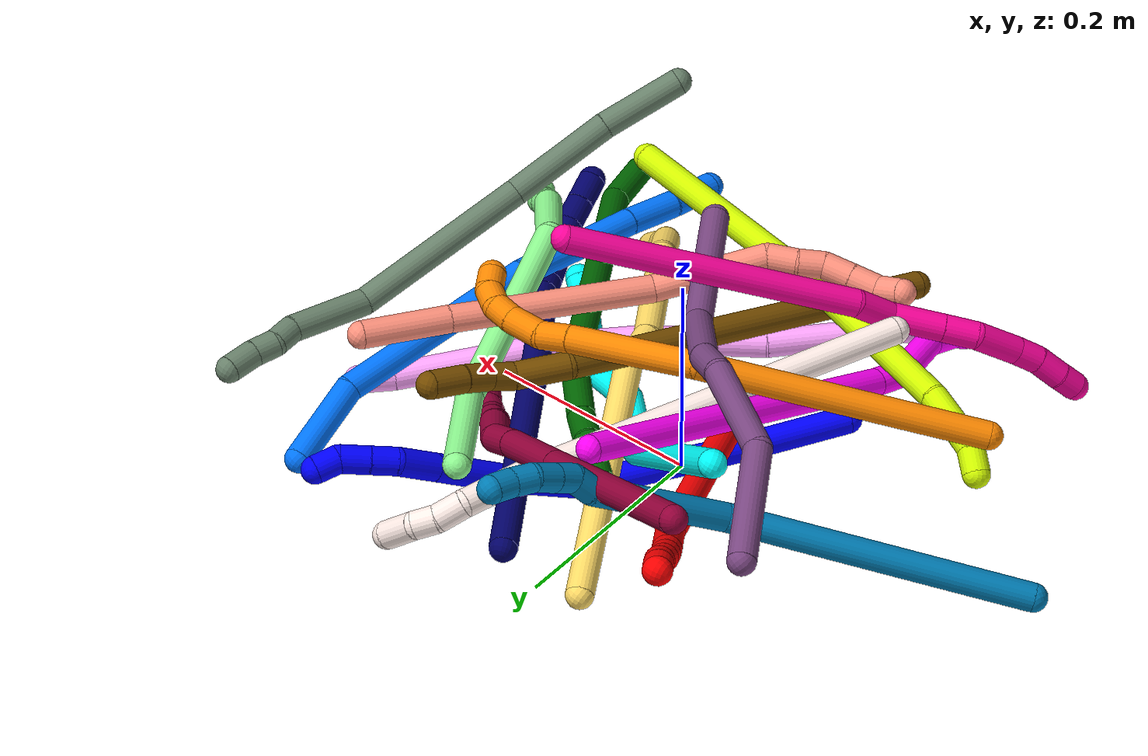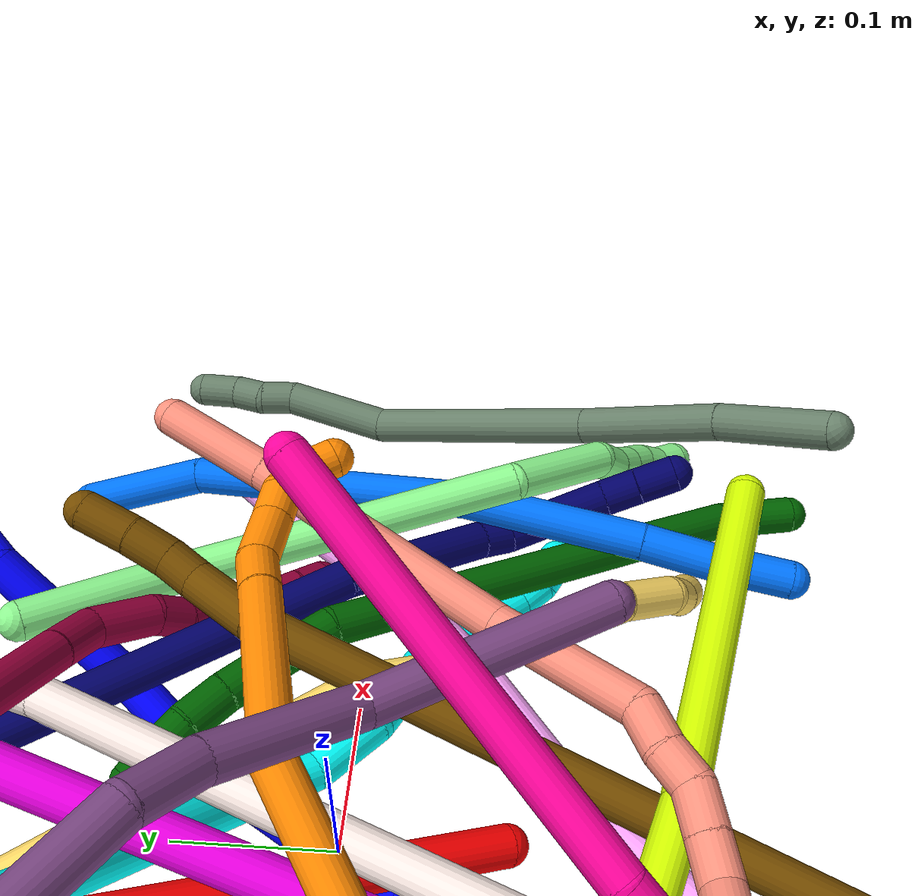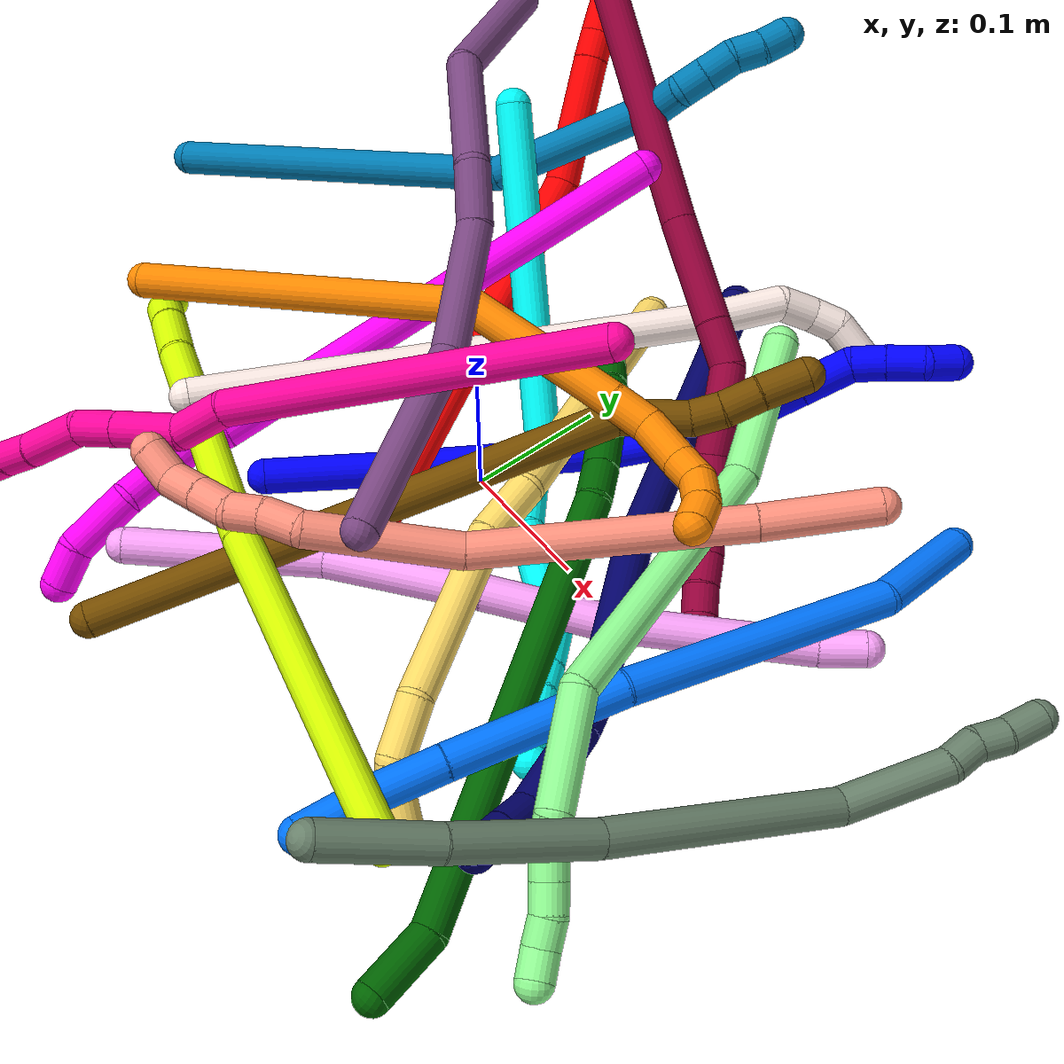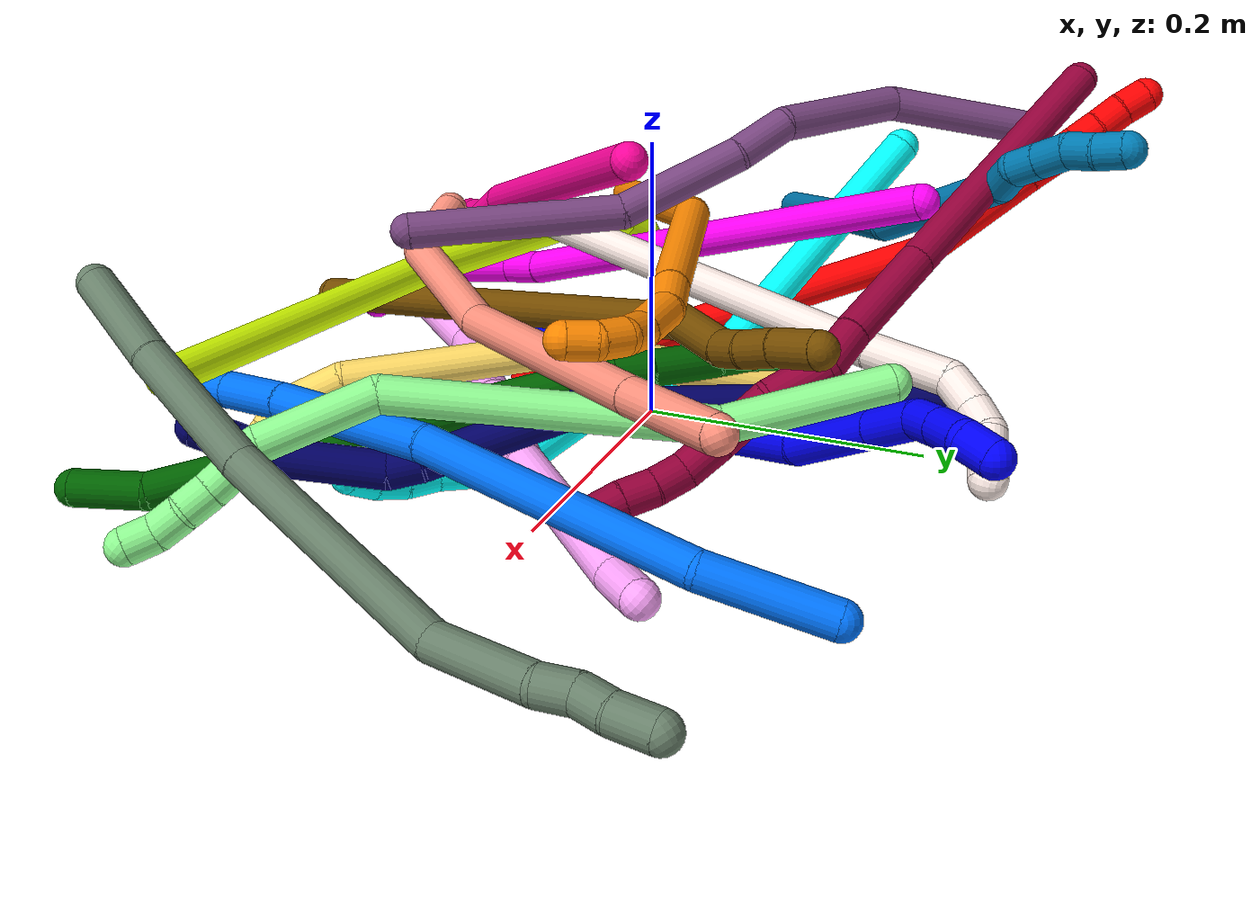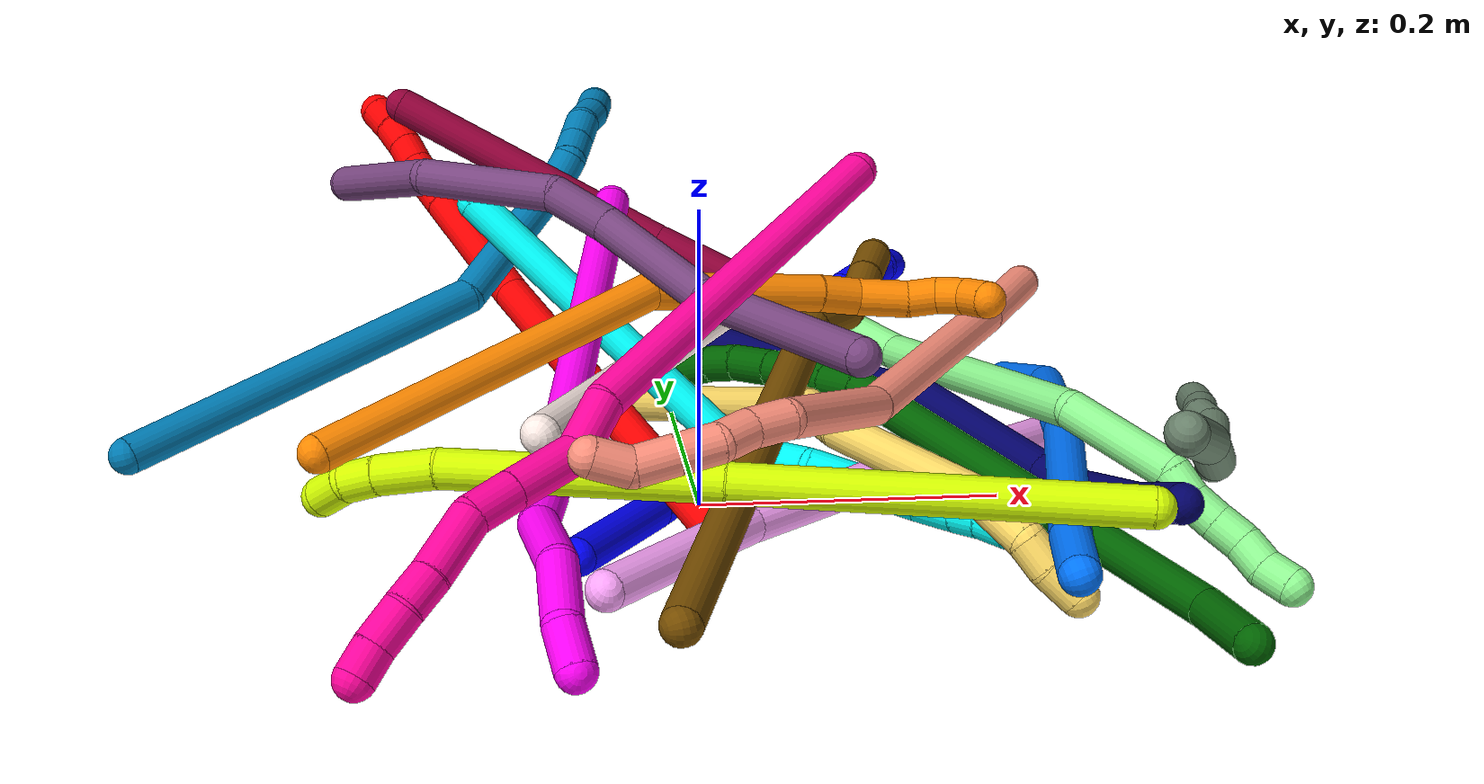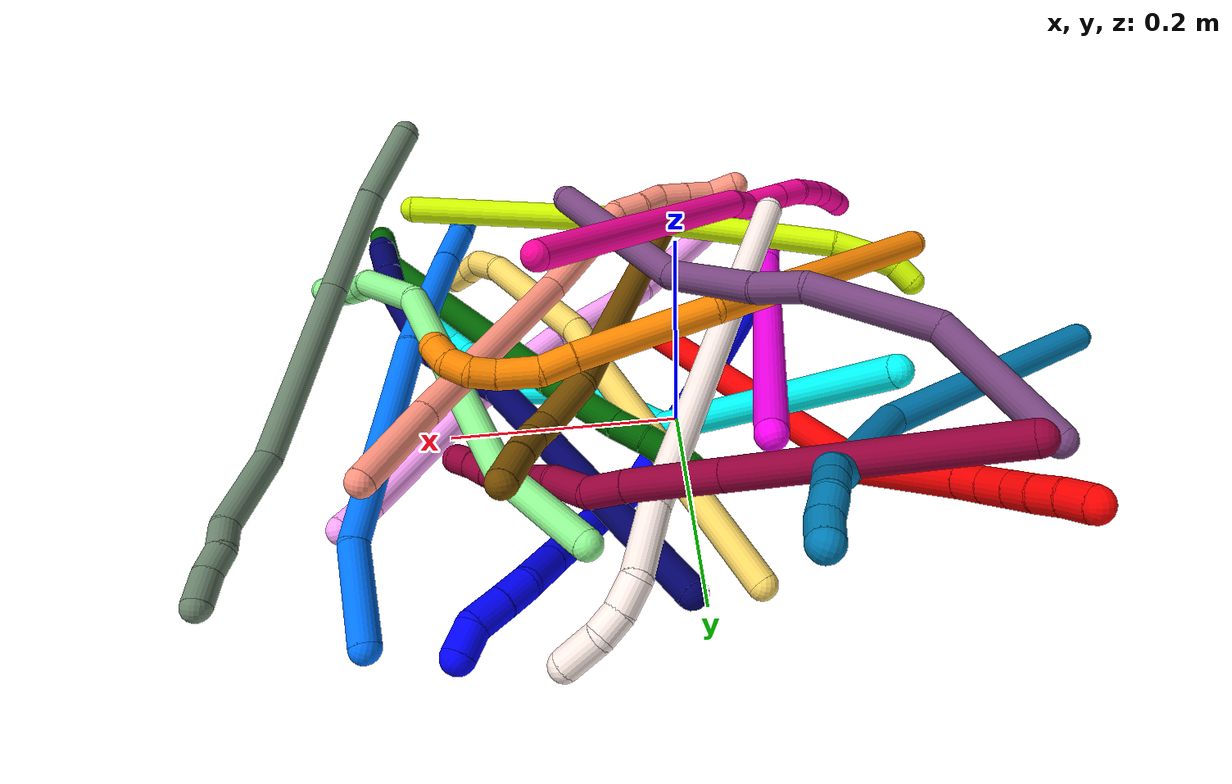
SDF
<sdf version="1.7">
 <world name="default">
  <plugin name="TubeGeneratorPlugin" filename="libtube_generator_plugin.so"/>
  <model name="photoneo_s_sensor">
   <static>1</static>
   <pose>0 0 2 1.57079 1.57079 3.14159</pose>
   <link name="link">
    <inertial><mass>0.1</mass></inertial>
    <sensor name="sensor" type="depth">
     <update_rate>30</update_rate>
     <camera>
      <horizontal_fov>1.22</horizontal_fov>
      <image><width>1920</width><height>1200</height><format>B8G8R8</format></image>
      <clip><near>0.1</near><far>4</far></clip>
      <depth_camera><output>points</output></depth_camera>
     </camera>
     <plugin name="camera_plugin" filename="libgazebo_ros_depth_camera.so">
      <baseline>0.2</baseline>
      <alwaysOn>1</alwaysOn>
      <updateRate>0.0</updateRate>
      <cameraName>camera_ir</cameraName>
      <imageTopicName>/camera/color/image_raw</imageTopicName>
      <cameraInfoTopicName>/camera/color/camera_info</cameraInfoTopicName>
      <depthImageTopicName>/camera/depth/image_raw</depthImageTopicName>
      <depthImageCameraInfoTopicName>/camera/depth/camera_info</depthImageCameraInfoTopicName>
      <pointCloudTopicName>/camera/depth/points</pointCloudTopicName>
      <frameName>fr_optical</frameName>
      <pointCloudCutoff>0.1</pointCloudCutoff>
      <pointCloudCutoffMax>2.0</pointCloudCutoffMax>
      <distortionK1>0</distortionK1>
      <distortionK2>0</distortionK2>
      <distortionK3>0</distortionK3>
      <distortionT1>0</distortionT1>
      <distortionT2>0</distortionT2>
      <CxPrime>0</CxPrime>
      <Cx>0</Cx>
      <Cy>0</Cy>
      <focalLength>0</focalLength>
      <hackBaseline>0</hackBaseline>
     </plugin>
    </sensor>
   </link>
  </model>
  <gravity>0 0 -9.8</gravity>
  <magnetic_field>6e-06 2.3e-05 -4.2e-05</magnetic_field>
  <atmosphere type="adiabatic"/>
  <physics name="default_physics" default="0" type="ode">
   <max_step_size>0.003</max_step_size>
   <real_time_factor>1</real_time_factor>
   <real_time_update_rate>1000</real_time_update_rate>
   <max_contacts>10000</max_contacts>
   <ode>
    <solver>
     <type>quick</type>
     <iters>100</iters>
     <sor>1.3</sor>
     <use_dynamic_moi_rescaling>0</use_dynamic_moi_rescaling>
    </solver>
    <constraints>
     <contact_max_correcting_vel>0</contact_max_correcting_vel>
     <contact_surface_layer>0.001</contact_surface_layer>
     <cfm>0</cfm>
     <erp>0.2</erp>
    </constraints>
   </ode>
  </physics>
  <scene><ambient>0.4 0.4 0.4 1</ambient><background>0.7 0.7 0.7 1</background><shadows>0</shadows></scene>
  <audio><device>default</device></audio>
  <spherical_coordinates>
   <surface_model>EARTH_WGS84</surface_model>
   <latitude_deg>0</latitude_deg>
   <longitude_deg>0</longitude_deg>
   <elevation>0</elevation>
   <heading_deg>0</heading_deg>
  </spherical_coordinates>
  <model name="bin">
   <static>1</static>
   <link name="bottom">
    <collision name="collision-bottom">
     <pose>0 0 -0.01 0 -0 0</pose>
     <geometry><box><size>0.8 0.6 0.02</size></box></geometry>
     <surface>
      <friction><ode><mu>100</mu><mu2>100</mu2></ode></friction>
      <contact><collide_bitmask>65535</collide_bitmask></contact>
     </surface>
    </collision>
   </link>
   <link name="west_wall">
    <collision name="collision-west_wall">
     <pose>-0.41 0 0.1 0 -0 0</pose>
     <geometry><box><size>0.02 0.6 0.2</size></box></geometry>
     <surface>
      <friction><ode><mu>100</mu><mu2>100</mu2></ode></friction>
      <contact><collide_bitmask>65535</collide_bitmask></contact>
     </surface>
    </collision>
   </link>
   <link name="east_wall">
    <collision name="collision-east_wall">
     <pose>0.41 0 0.1 0 -0 0</pose>
     <geometry><box><size>0.02 0.6 0.2</size></box></geometry>
     <surface>
      <friction><ode><mu>100</mu><mu2>100</mu2></ode></friction>
      <contact><collide_bitmask>65535</collide_bitmask></contact>
     </surface>
    </collision>
   </link>
   <link name="south_wall">
    <collision name="collision-south_wall">
     <pose>0 -0.31 0.1 0 -0 0</pose>
     <geometry><box><size>0.8 0.02 0.2</size></box></geometry>
     <surface>
      <friction><ode><mu>100</mu><mu2>100</mu2></ode></friction>
      <contact><collide_bitmask>65535</collide_bitmask></contact>
     </surface>
    </collision>
   </link>
   <link name="north_wall">
    <collision name="collision-north_wall">
     <pose>0 0.31 0.1 0 -0 0</pose>
     <geometry><box><size>0.8 0.02 0.2</size></box></geometry>
     <surface>
      <friction><ode><mu>100</mu><mu2>100</mu2></ode></friction>
      <contact><collide_bitmask>65535</collide_bitmask></contact>
     </surface>
    </collision>
   </link>
  </model>
  <model name="1">
   <static>0</static>
   <link name="1">
    <collision name="collision-cylinder-e_1_1_4">
     <pose>0.021833 0.036547 0.027768 -0.921055 0.444003 -0.223035</pose>
     <geometry><cylinder><radius>0.0125</radius><length>0.101655</length></cylinder></geometry>
     <surface>
      <friction><ode><mu>1.16</mu><mu2>1.16</mu2><slip1>0</slip1><slip2>0</slip2></ode></friction>
      <contact><ode><kp>1e+06</kp><kd>1</kd><max_vel>0</max_vel><min_depth>0.001</min_depth></ode></contact>
     </surface>
    </collision>
    <visual name="visual-cylinder-e_1_1_4">
     <pose>0.021833 0.036547 0.027768 -0.921055 0.444003 -0.223035</pose>
     <geometry><cylinder><radius>0.0125</radius><length>0.101655</length></cylinder></geometry>
     <material><ambient>0 0 1 1</ambient></material>
    </visual>
    <collision name="collision-cylinder-e_2_4_5">
     <pose>0.076537 0.122776 0.094246 -0.9089 0.481014 -0.238503</pose>
     <geometry><cylinder><radius>0.0125</radius><length>0.142087</length></cylinder></geometry>
     <surface>
      <friction><ode><mu>1.16</mu><mu2>1.16</mu2><slip1>0</slip1><slip2>0</slip2></ode></friction>
      <contact><ode><kp>1e+06</kp><kd>1</kd><max_vel>0</max_vel><min_depth>0.001</min_depth></ode></contact>
     </surface>
    </collision>
    <visual name="visual-cylinder-e_2_4_5">
     <pose>0.076537 0.122776 0.094246 -0.9089 0.481014 -0.238503</pose>
     <geometry><cylinder><radius>0.0125</radius><length>0.142087</length></cylinder></geometry>
     <material><ambient>0 0 1 1</ambient></material>
    </visual>
    <collision name="collision-cylinder-e_3_5_6">
     <pose>0.134853 0.191825 0.148692 -0.888471 0.795141 -0.394547</pose>
     <geometry><cylinder><radius>0.0125</radius><length>0.071282</length></cylinder></geometry>
     <surface>
      <friction><ode><mu>1.16</mu><mu2>1.16</mu2><slip1>0</slip1><slip2>0</slip2></ode></friction>
      <contact><ode><kp>1e+06</kp><kd>1</kd><max_vel>0</max_vel><min_depth>0.001</min_depth></ode></contact>
     </surface>
    </collision>
    <visual name="visual-cylinder-e_3_5_6">
     <pose>0.134853 0.191825 0.148692 -0.888471 0.795141 -0.394547</pose>
     <geometry><cylinder><radius>0.0125</radius><length>0.071282</length></cylinder></geometry>
     <material><ambient>0 0 1 1</ambient></material>
    </visual>
    <collision name="collision-cylinder-e_4_6_7">
     <pose>0.189302 0.222816 0.18464 -0.521886 0.893677 -0.25452</pose>
     <geometry><cylinder><radius>0.0125</radius><length>0.074423</length></cylinder></geometry>
     <surface>
      <friction><ode><mu>1.16</mu><mu2>1.16</mu2><slip1>0</slip1><slip2>0</slip2></ode></friction>
      <contact><ode><kp>1e+06</kp><kd>1</kd><max_vel>0</max_vel><min_depth>0.001</min_depth></ode></contact>
     </surface>
    </collision>
    <visual name="visual-cylinder-e_4_6_7">
     <pose>0.189302 0.222816 0.18464 -0.521886 0.893677 -0.25452</pose>
     <geometry><cylinder><radius>0.0125</radius><length>0.074423</length></cylinder></geometry>
     <material><ambient>0 0 1 1</ambient></material>
    </visual>
    <collision name="collision-cylinder-e_5_7_8">
     <pose>0.23322 0.240443 0.215343 -0.519753 0.889746 -0.252179</pose>
     <geometry><cylinder><radius>0.0125</radius><length>0.0384</length></cylinder></geometry>
     <surface>
      <friction><ode><mu>1.16</mu><mu2>1.16</mu2><slip1>0</slip1><slip2>0</slip2></ode></friction>
      <contact><ode><kp>1e+06</kp><kd>1</kd><max_vel>0</max_vel><min_depth>0.001</min_depth></ode></contact>
     </surface>
    </collision>
    <visual name="visual-cylinder-e_5_7_8">
     <pose>0.23322 0.240443 0.215343 -0.519753 0.889746 -0.252179</pose>
     <geometry><cylinder><radius>0.0125</radius><length>0.0384</length></cylinder></geometry>
     <material><ambient>0 0 1 1</ambient></material>
    </visual>
    <collision name="collision-cylinder-e_6_8_9">
     <pose>0.255862 0.254242 0.230157 -1.06464 0.714154 -0.432625</pose>
     <geometry><cylinder><radius>0.0125</radius><length>0.023589</length></cylinder></geometry>
     <surface>
      <friction><ode><mu>1.16</mu><mu2>1.16</mu2><slip1>0</slip1><slip2>0</slip2></ode></friction>
      <contact><ode><kp>1e+06</kp><kd>1</kd><max_vel>0</max_vel><min_depth>0.001</min_depth></ode></contact>
     </surface>
    </collision>
    <visual name="visual-cylinder-e_6_8_9">
     <pose>0.255862 0.254242 0.230157 -1.06464 0.714154 -0.432625</pose>
     <geometry><cylinder><radius>0.0125</radius><length>0.023589</length></cylinder></geometry>
     <material><ambient>0 0 1 1</ambient></material>
    </visual>
    <collision name="collision-cylinder-e_7_9_10">
     <pose>0.272051 0.271192 0.238783 -1.13126 0.696647 -0.45313</pose>
     <geometry><cylinder><radius>0.0125</radius><length>0.026381</length></cylinder></geometry>
     <surface>
      <friction><ode><mu>1.16</mu><mu2>1.16</mu2><slip1>0</slip1><slip2>0</slip2></ode></friction>
      <contact><ode><kp>1e+06</kp><kd>1</kd><max_vel>0</max_vel><min_depth>0.001</min_depth></ode></contact>
     </surface>
    </collision>
    <visual name="visual-cylinder-e_7_9_10">
     <pose>0.272051 0.271192 0.238783 -1.13126 0.696647 -0.45313</pose>
     <geometry><cylinder><radius>0.0125</radius><length>0.026381</length></cylinder></geometry>
     <material><ambient>0 0 1 1</ambient></material>
    </visual>
    <collision name="collision-cylinder-e_8_10_2">
     <pose>0.283469 0.288699 0.249762 -0.896557 0.269637 -0.130284</pose>
     <geometry><cylinder><radius>0.0125</radius><length>0.022183</length></cylinder></geometry>
     <surface>
      <friction><ode><mu>1.16</mu><mu2>1.16</mu2><slip1>0</slip1><slip2>0</slip2></ode></friction>
      <contact><ode><kp>1e+06</kp><kd>1</kd><max_vel>0</max_vel><min_depth>0.001</min_depth></ode></contact>
     </surface>
    </collision>
    <visual name="visual-cylinder-e_8_10_2">
     <pose>0.283469 0.288699 0.249762 -0.896557 0.269637 -0.130284</pose>
     <geometry><cylinder><radius>0.0125</radius><length>0.022183</length></cylinder></geometry>
     <material><ambient>0 0 1 1</ambient></material>
    </visual>
    <collision name="collision-sphere-2">
     <pose>0.286424 0.297051 0.256436 0 -0 0</pose>
     <geometry><sphere><radius>0.0125</radius></sphere></geometry>
     <surface>
      <friction><ode><mu>1.16</mu><mu2>1.16</mu2><slip1>0</slip1><slip2>0</slip2></ode></friction>
      <contact><ode><kp>1e+06</kp><kd>1</kd><max_vel>0</max_vel><min_depth>0.001</min_depth></ode></contact>
     </surface>
    </collision>
    <visual name="visual-sphere-2">
     <pose>0.286424 0.297051 0.256436 0 -0 0</pose>
     <geometry><sphere><radius>0.0125</radius></sphere></geometry>
     <material><ambient>0 0 1 1</ambient></material>
    </visual>
    <collision name="collision-sphere-10">
     <pose>0.280515 0.280348 0.243088 0 -0 0</pose>
     <geometry><sphere><radius>0.0125</radius></sphere></geometry>
     <surface>
      <friction><ode><mu>1.16</mu><mu2>1.16</mu2><slip1>0</slip1><slip2>0</slip2></ode></friction>
      <contact><ode><kp>1e+06</kp><kd>1</kd><max_vel>0</max_vel><min_depth>0.001</min_depth></ode></contact>
     </surface>
    </collision>
    <visual name="visual-sphere-10">
     <pose>0.280515 0.280348 0.243088 0 -0 0</pose>
     <geometry><sphere><radius>0.0125</radius></sphere></geometry>
     <material><ambient>0 0 1 1</ambient></material>
    </visual>
    <collision name="collision-sphere-9">
     <pose>0.263587 0.262037 0.234478 0 -0 0</pose>
     <geometry><sphere><radius>0.0125</radius></sphere></geometry>
     <surface>
      <friction><ode><mu>1.16</mu><mu2>1.16</mu2><slip1>0</slip1><slip2>0</slip2></ode></friction>
      <contact><ode><kp>1e+06</kp><kd>1</kd><max_vel>0</max_vel><min_depth>0.001</min_depth></ode></contact>
     </surface>
    </collision>
    <visual name="visual-sphere-9">
     <pose>0.263587 0.262037 0.234478 0 -0 0</pose>
     <geometry><sphere><radius>0.0125</radius></sphere></geometry>
     <material><ambient>0 0 1 1</ambient></material>
    </visual>
    <collision name="collision-sphere-4">
     <pose>0.043667 0.073094 0.055536 0 -0 0</pose>
     <geometry><sphere><radius>0.0125</radius></sphere></geometry>
     <surface>
      <friction><ode><mu>1.16</mu><mu2>1.16</mu2><slip1>0</slip1><slip2>0</slip2></ode></friction>
      <contact><ode><kp>1e+06</kp><kd>1</kd><max_vel>0</max_vel><min_depth>0.001</min_depth></ode></contact>
     </surface>
    </collision>
    <visual name="visual-sphere-4">
     <pose>0.043667 0.073094 0.055536 0 -0 0</pose>
     <geometry><sphere><radius>0.0125</radius></sphere></geometry>
     <material><ambient>0 0 1 1</ambient></material>
    </visual>
    <collision name="collision-sphere-1">
     <geometry><sphere><radius>0.0125</radius></sphere></geometry>
     <surface>
      <friction><ode><mu>1.16</mu><mu2>1.16</mu2><slip1>0</slip1><slip2>0</slip2></ode></friction>
      <contact><ode><kp>1e+06</kp><kd>1</kd><max_vel>0</max_vel><min_depth>0.001</min_depth></ode></contact>
     </surface>
    </collision>
    <visual name="visual-sphere-1">
     <geometry><sphere><radius>0.0125</radius></sphere></geometry>
     <material><ambient>0 0 1 1</ambient></material>
    </visual>
    <collision name="collision-sphere-8">
     <pose>0.248137 0.246447 0.225836 0 -0 0</pose>
     <geometry><sphere><radius>0.0125</radius></sphere></geometry>
     <surface>
      <friction><ode><mu>1.16</mu><mu2>1.16</mu2><slip1>0</slip1><slip2>0</slip2></ode></friction>
      <contact><ode><kp>1e+06</kp><kd>1</kd><max_vel>0</max_vel><min_depth>0.001</min_depth></ode></contact>
     </surface>
    </collision>
    <visual name="visual-sphere-8">
     <pose>0.248137 0.246447 0.225836 0 -0 0</pose>
     <geometry><sphere><radius>0.0125</radius></sphere></geometry>
     <material><ambient>0 0 1 1</ambient></material>
    </visual>
    <collision name="collision-sphere-5">
     <pose>0.109407 0.172458 0.132955 0 -0 0</pose>
     <geometry><sphere><radius>0.0125</radius></sphere></geometry>
     <surface>
      <friction><ode><mu>1.16</mu><mu2>1.16</mu2><slip1>0</slip1><slip2>0</slip2></ode></friction>
      <contact><ode><kp>1e+06</kp><kd>1</kd><max_vel>0</max_vel><min_depth>0.001</min_depth></ode></contact>
     </surface>
    </collision>
    <visual name="visual-sphere-5">
     <pose>0.109407 0.172458 0.132955 0 -0 0</pose>
     <geometry><sphere><radius>0.0125</radius></sphere></geometry>
     <material><ambient>0 0 1 1</ambient></material>
    </visual>
    <collision name="collision-sphere-6">
     <pose>0.1603 0.211193 0.164429 0 -0 0</pose>
     <geometry><sphere><radius>0.0125</radius></sphere></geometry>
     <surface>
      <friction><ode><mu>1.16</mu><mu2>1.16</mu2><slip1>0</slip1><slip2>0</slip2></ode></friction>
      <contact><ode><kp>1e+06</kp><kd>1</kd><max_vel>0</max_vel><min_depth>0.001</min_depth></ode></contact>
     </surface>
    </collision>
    <visual name="visual-sphere-6">
     <pose>0.1603 0.211193 0.164429 0 -0 0</pose>
     <geometry><sphere><radius>0.0125</radius></sphere></geometry>
     <material><ambient>0 0 1 1</ambient></material>
    </visual>
    <collision name="collision-sphere-7">
     <pose>0.218304 0.234439 0.204851 0 -0 0</pose>
     <geometry><sphere><radius>0.0125</radius></sphere></geometry>
     <surface>
      <friction><ode><mu>1.16</mu><mu2>1.16</mu2><slip1>0</slip1><slip2>0</slip2></ode></friction>
      <contact><ode><kp>1e+06</kp><kd>1</kd><max_vel>0</max_vel><min_depth>0.001</min_depth></ode></contact>
     </surface>
    </collision>
    <visual name="visual-sphere-7">
     <pose>0.218304 0.234439 0.204851 0 -0 0</pose>
     <geometry><sphere><radius>0.0125</radius></sphere></geometry>
     <material><ambient>0 0 1 1</ambient></material>
    </visual>
    <inertial>
     <pose>0.130504 0.16041 0.132185 0 -0 0</pose>
     <mass>0.5</mass>
     <inertia>
      <ixx>0.000279</ixx>
      <ixy>0</ixy>
      <ixz>0</ixz>
      <iyy>0.000235</iyy>
      <iyz>0</iyz>
      <izz>-0.000466</izz>
     </inertia>
    </inertial>
   </link>
   <pose>-0.086463 -0.124694 0.015391 -1.50458 -0.960667 0.38157</pose>
  </model>
  <model name="2">
   <static>0</static>
   <link name="2">
    <collision name="collision-cylinder-e_1_1_4">
     <pose>-0.086307 0.119541 0.033738 -1.29573 -0.607259 0.46566</pose>
     <geometry><cylinder><radius>0.0125</radius><length>0.302504</length></cylinder></geometry>
     <surface>
      <friction><ode><mu>1.16</mu><mu2>1.16</mu2><slip1>0</slip1><slip2>0</slip2></ode></friction>
      <contact><ode><kp>1e+06</kp><kd>1</kd><max_vel>0</max_vel><min_depth>0.001</min_depth></ode></contact>
     </surface>
    </collision>
    <visual name="visual-cylinder-e_1_1_4">
     <pose>-0.086307 0.119541 0.033738 -1.29573 -0.607259 0.46566</pose>
     <geometry><cylinder><radius>0.0125</radius><length>0.302504</length></cylinder></geometry>
     <material><ambient>1 0 0 1</ambient></material>
    </visual>
    <collision name="collision-cylinder-e_2_4_5">
     <pose>-0.185656 0.282281 0.08166 -1.25352 -0.279313 0.202895</pose>
     <geometry><cylinder><radius>0.0125</radius><length>0.094604</length></cylinder></geometry>
     <surface>
      <friction><ode><mu>1.16</mu><mu2>1.16</mu2><slip1>0</slip1><slip2>0</slip2></ode></friction>
      <contact><ode><kp>1e+06</kp><kd>1</kd><max_vel>0</max_vel><min_depth>0.001</min_depth></ode></contact>
     </surface>
    </collision>
    <visual name="visual-cylinder-e_2_4_5">
     <pose>-0.185656 0.282281 0.08166 -1.25352 -0.279313 0.202895</pose>
     <geometry><cylinder><radius>0.0125</radius><length>0.094604</length></cylinder></geometry>
     <material><ambient>1 0 0 1</ambient></material>
    </visual>
    <collision name="collision-cylinder-e_3_5_6">
     <pose>-0.201876 0.334767 0.098753 -1.2674 -0.315774 0.232919</pose>
     <geometry><cylinder><radius>0.0125</radius><length>0.020475</length></cylinder></geometry>
     <surface>
      <friction><ode><mu>1.16</mu><mu2>1.16</mu2><slip1>0</slip1><slip2>0</slip2></ode></friction>
      <contact><ode><kp>1e+06</kp><kd>1</kd><max_vel>0</max_vel><min_depth>0.001</min_depth></ode></contact>
     </surface>
    </collision>
    <visual name="visual-cylinder-e_3_5_6">
     <pose>-0.201876 0.334767 0.098753 -1.2674 -0.315774 0.232919</pose>
     <geometry><cylinder><radius>0.0125</radius><length>0.020475</length></cylinder></geometry>
     <material><ambient>1 0 0 1</ambient></material>
    </visual>
    <collision name="collision-cylinder-e_4_6_7">
     <pose>-0.208265 0.354231 0.104376 -1.31005 -0.295864 0.227952</pose>
     <geometry><cylinder><radius>0.0125</radius><length>0.022023</length></cylinder></geometry>
     <surface>
      <friction><ode><mu>1.16</mu><mu2>1.16</mu2><slip1>0</slip1><slip2>0</slip2></ode></friction>
      <contact><ode><kp>1e+06</kp><kd>1</kd><max_vel>0</max_vel><min_depth>0.001</min_depth></ode></contact>
     </surface>
    </collision>
    <visual name="visual-cylinder-e_4_6_7">
     <pose>-0.208265 0.354231 0.104376 -1.31005 -0.295864 0.227952</pose>
     <geometry><cylinder><radius>0.0125</radius><length>0.022023</length></cylinder></geometry>
     <material><ambient>1 0 0 1</ambient></material>
    </visual>
    <collision name="collision-cylinder-e_5_7_8">
     <pose>-0.214363 0.373833 0.108883 -1.38298 -0.292318 0.242536</pose>
     <geometry><cylinder><radius>0.0125</radius><length>0.020038</length></cylinder></geometry>
     <surface>
      <friction><ode><mu>1.16</mu><mu2>1.16</mu2><slip1>0</slip1><slip2>0</slip2></ode></friction>
      <contact><ode><kp>1e+06</kp><kd>1</kd><max_vel>0</max_vel><min_depth>0.001</min_depth></ode></contact>
     </surface>
    </collision>
    <visual name="visual-cylinder-e_5_7_8">
     <pose>-0.214363 0.373833 0.108883 -1.38298 -0.292318 0.242536</pose>
     <geometry><cylinder><radius>0.0125</radius><length>0.020038</length></cylinder></geometry>
     <material><ambient>1 0 0 1</ambient></material>
    </visual>
    <collision name="collision-cylinder-e_6_8_9">
     <pose>-0.219904 0.392501 0.113513 -1.27279 -0.267842 0.198461</pose>
     <geometry><cylinder><radius>0.0125</radius><length>0.020052</length></cylinder></geometry>
     <surface>
      <friction><ode><mu>1.16</mu><mu2>1.16</mu2><slip1>0</slip1><slip2>0</slip2></ode></friction>
      <contact><ode><kp>1e+06</kp><kd>1</kd><max_vel>0</max_vel><min_depth>0.001</min_depth></ode></contact>
     </surface>
    </collision>
    <visual name="visual-cylinder-e_6_8_9">
     <pose>-0.219904 0.392501 0.113513 -1.27279 -0.267842 0.198461</pose>
     <geometry><cylinder><radius>0.0125</radius><length>0.020052</length></cylinder></geometry>
     <material><ambient>1 0 0 1</ambient></material>
    </visual>
    <collision name="collision-cylinder-e_7_9_2">
     <pose>-0.226193 0.410606 0.119711 -1.20849 -0.366297 0.254371</pose>
     <geometry><cylinder><radius>0.0125</radius><length>0.020304</length></cylinder></geometry>
     <surface>
      <friction><ode><mu>1.16</mu><mu2>1.16</mu2><slip1>0</slip1><slip2>0</slip2></ode></friction>
      <contact><ode><kp>1e+06</kp><kd>1</kd><max_vel>0</max_vel><min_depth>0.001</min_depth></ode></contact>
     </surface>
    </collision>
    <visual name="visual-cylinder-e_7_9_2">
     <pose>-0.226193 0.410606 0.119711 -1.20849 -0.366297 0.254371</pose>
     <geometry><cylinder><radius>0.0125</radius><length>0.020304</length></cylinder></geometry>
     <material><ambient>1 0 0 1</ambient></material>
    </visual>
    <collision name="collision-sphere-2">
     <pose>-0.229829 0.41947 0.123071 0 -0 0</pose>
     <geometry><sphere><radius>0.0125</radius></sphere></geometry>
     <surface>
      <friction><ode><mu>1.16</mu><mu2>1.16</mu2><slip1>0</slip1><slip2>0</slip2></ode></friction>
      <contact><ode><kp>1e+06</kp><kd>1</kd><max_vel>0</max_vel><min_depth>0.001</min_depth></ode></contact>
     </surface>
    </collision>
    <visual name="visual-sphere-2">
     <pose>-0.229829 0.41947 0.123071 0 -0 0</pose>
     <geometry><sphere><radius>0.0125</radius></sphere></geometry>
     <material><ambient>1 0 0 1</ambient></material>
    </visual>
    <collision name="collision-sphere-9">
     <pose>-0.222557 0.401743 0.116352 0 -0 0</pose>
     <geometry><sphere><radius>0.0125</radius></sphere></geometry>
     <surface>
      <friction><ode><mu>1.16</mu><mu2>1.16</mu2><slip1>0</slip1><slip2>0</slip2></ode></friction>
      <contact><ode><kp>1e+06</kp><kd>1</kd><max_vel>0</max_vel><min_depth>0.001</min_depth></ode></contact>
     </surface>
    </collision>
    <visual name="visual-sphere-9">
     <pose>-0.222557 0.401743 0.116352 0 -0 0</pose>
     <geometry><sphere><radius>0.0125</radius></sphere></geometry>
     <material><ambient>1 0 0 1</ambient></material>
    </visual>
    <collision name="collision-sphere-4">
     <pose>-0.172615 0.239082 0.067475 0 -0 0</pose>
     <geometry><sphere><radius>0.0125</radius></sphere></geometry>
     <surface>
      <friction><ode><mu>1.16</mu><mu2>1.16</mu2><slip1>0</slip1><slip2>0</slip2></ode></friction>
      <contact><ode><kp>1e+06</kp><kd>1</kd><max_vel>0</max_vel><min_depth>0.001</min_depth></ode></contact>
     </surface>
    </collision>
    <visual name="visual-sphere-4">
     <pose>-0.172615 0.239082 0.067475 0 -0 0</pose>
     <geometry><sphere><radius>0.0125</radius></sphere></geometry>
     <material><ambient>1 0 0 1</ambient></material>
    </visual>
    <collision name="collision-sphere-1">
     <geometry><sphere><radius>0.0125</radius></sphere></geometry>
     <surface>
      <friction><ode><mu>1.16</mu><mu2>1.16</mu2><slip1>0</slip1><slip2>0</slip2></ode></friction>
      <contact><ode><kp>1e+06</kp><kd>1</kd><max_vel>0</max_vel><min_depth>0.001</min_depth></ode></contact>
     </surface>
    </collision>
    <visual name="visual-sphere-1">
     <geometry><sphere><radius>0.0125</radius></sphere></geometry>
     <material><ambient>1 0 0 1</ambient></material>
    </visual>
    <collision name="collision-sphere-8">
     <pose>-0.21725 0.383258 0.110674 0 -0 0</pose>
     <geometry><sphere><radius>0.0125</radius></sphere></geometry>
     <surface>
      <friction><ode><mu>1.16</mu><mu2>1.16</mu2><slip1>0</slip1><slip2>0</slip2></ode></friction>
      <contact><ode><kp>1e+06</kp><kd>1</kd><max_vel>0</max_vel><min_depth>0.001</min_depth></ode></contact>
     </surface>
    </collision>
    <visual name="visual-sphere-8">
     <pose>-0.21725 0.383258 0.110674 0 -0 0</pose>
     <geometry><sphere><radius>0.0125</radius></sphere></geometry>
     <material><ambient>1 0 0 1</ambient></material>
    </visual>
    <collision name="collision-sphere-5">
     <pose>-0.198697 0.325481 0.095846 0 -0 0</pose>
     <geometry><sphere><radius>0.0125</radius></sphere></geometry>
     <surface>
      <friction><ode><mu>1.16</mu><mu2>1.16</mu2><slip1>0</slip1><slip2>0</slip2></ode></friction>
      <contact><ode><kp>1e+06</kp><kd>1</kd><max_vel>0</max_vel><min_depth>0.001</min_depth></ode></contact>
     </surface>
    </collision>
    <visual name="visual-sphere-5">
     <pose>-0.198697 0.325481 0.095846 0 -0 0</pose>
     <geometry><sphere><radius>0.0125</radius></sphere></geometry>
     <material><ambient>1 0 0 1</ambient></material>
    </visual>
    <collision name="collision-sphere-6">
     <pose>-0.205055 0.344054 0.10166 0 -0 0</pose>
     <geometry><sphere><radius>0.0125</radius></sphere></geometry>
     <surface>
      <friction><ode><mu>1.16</mu><mu2>1.16</mu2><slip1>0</slip1><slip2>0</slip2></ode></friction>
      <contact><ode><kp>1e+06</kp><kd>1</kd><max_vel>0</max_vel><min_depth>0.001</min_depth></ode></contact>
     </surface>
    </collision>
    <visual name="visual-sphere-6">
     <pose>-0.205055 0.344054 0.10166 0 -0 0</pose>
     <geometry><sphere><radius>0.0125</radius></sphere></geometry>
     <material><ambient>1 0 0 1</ambient></material>
    </visual>
    <collision name="collision-sphere-7">
     <pose>-0.211476 0.364408 0.107091 0 -0 0</pose>
     <geometry><sphere><radius>0.0125</radius></sphere></geometry>
     <surface>
      <friction><ode><mu>1.16</mu><mu2>1.16</mu2><slip1>0</slip1><slip2>0</slip2></ode></friction>
      <contact><ode><kp>1e+06</kp><kd>1</kd><max_vel>0</max_vel><min_depth>0.001</min_depth></ode></contact>
     </surface>
    </collision>
    <visual name="visual-sphere-7">
     <pose>-0.211476 0.364408 0.107091 0 -0 0</pose>
     <geometry><sphere><radius>0.0125</radius></sphere></geometry>
     <material><ambient>1 0 0 1</ambient></material>
    </visual>
    <inertial>
     <pose>-0.131379 0.202441 0.058281 0 -0 0</pose>
     <mass>0.5</mass>
     <inertia>
      <ixx>0.002631</ixx>
      <ixy>0</ixy>
      <ixz>0</ixz>
      <iyy>0.002067</iyy>
      <iyz>0</iyz>
      <izz>-0.000552</izz>
     </inertia>
    </inertial>
   </link>
   <pose>0.004056 -0.097236 0.013227 1.77727 -0.570493 -1.5482</pose>
  </model>
  <model name="3">
   <static>0</static>
   <link name="3">
    <collision name="collision-cylinder-e_1_1_4">
     <pose>0.103797 -0.050793 -0.012128 1.80519 1.10467 1.32587</pose>
     <geometry><cylinder><radius>0.0125</radius><length>0.232386</length></cylinder></geometry>
     <surface>
      <friction><ode><mu>1.16</mu><mu2>1.16</mu2><slip1>0</slip1><slip2>0</slip2></ode></friction>
      <contact><ode><kp>1e+06</kp><kd>1</kd><max_vel>0</max_vel><min_depth>0.001</min_depth></ode></contact>
     </surface>
    </collision>
    <visual name="visual-cylinder-e_1_1_4">
     <pose>0.103797 -0.050793 -0.012128 1.80519 1.10467 1.32587</pose>
     <geometry><cylinder><radius>0.0125</radius><length>0.232386</length></cylinder></geometry>
     <material><ambient>0.003922 1 0.996078 1</ambient></material>
    </visual>
    <collision name="collision-cylinder-e_2_4_5">
     <pose>0.223633 -0.100813 -0.025017 -2.34834 1.50335 -2.29911</pose>
     <geometry><cylinder><radius>0.0125</radius><length>0.032151</length></cylinder></geometry>
     <surface>
      <friction><ode><mu>1.16</mu><mu2>1.16</mu2><slip1>0</slip1><slip2>0</slip2></ode></friction>
      <contact><ode><kp>1e+06</kp><kd>1</kd><max_vel>0</max_vel><min_depth>0.001</min_depth></ode></contact>
     </surface>
    </collision>
    <visual name="visual-cylinder-e_2_4_5">
     <pose>0.223633 -0.100813 -0.025017 -2.34834 1.50335 -2.29911</pose>
     <geometry><cylinder><radius>0.0125</radius><length>0.032151</length></cylinder></geometry>
     <material><ambient>0.003922 1 0.996078 1</ambient></material>
    </visual>
    <collision name="collision-cylinder-e_3_5_6">
     <pose>0.261497 -0.094981 -0.032717 -2.51161 1.19587 -2.24917</pose>
     <geometry><cylinder><radius>0.0125</radius><length>0.046908</length></cylinder></geometry>
     <surface>
      <friction><ode><mu>1.16</mu><mu2>1.16</mu2><slip1>0</slip1><slip2>0</slip2></ode></friction>
      <contact><ode><kp>1e+06</kp><kd>1</kd><max_vel>0</max_vel><min_depth>0.001</min_depth></ode></contact>
     </surface>
    </collision>
    <visual name="visual-cylinder-e_3_5_6">
     <pose>0.261497 -0.094981 -0.032717 -2.51161 1.19587 -2.24917</pose>
     <geometry><cylinder><radius>0.0125</radius><length>0.046908</length></cylinder></geometry>
     <material><ambient>0.003922 1 0.996078 1</ambient></material>
    </visual>
    <collision name="collision-cylinder-e_4_6_7">
     <pose>0.316202 -0.096915 -0.056916 2.75659 1.05549 2.49619</pose>
     <geometry><cylinder><radius>0.0125</radius><length>0.075576</length></cylinder></geometry>
     <surface>
      <friction><ode><mu>1.16</mu><mu2>1.16</mu2><slip1>0</slip1><slip2>0</slip2></ode></friction>
      <contact><ode><kp>1e+06</kp><kd>1</kd><max_vel>0</max_vel><min_depth>0.001</min_depth></ode></contact>
     </surface>
    </collision>
    <visual name="visual-cylinder-e_4_6_7">
     <pose>0.316202 -0.096915 -0.056916 2.75659 1.05549 2.49619</pose>
     <geometry><cylinder><radius>0.0125</radius><length>0.075576</length></cylinder></geometry>
     <material><ambient>0.003922 1 0.996078 1</ambient></material>
    </visual>
    <collision name="collision-cylinder-e_5_7_8">
     <pose>0.364119 -0.099918 -0.077238 -2.22546 1.24796 -1.94063</pose>
     <geometry><cylinder><radius>0.0125</radius><length>0.031711</length></cylinder></geometry>
     <surface>
      <friction><ode><mu>1.16</mu><mu2>1.16</mu2><slip1>0</slip1><slip2>0</slip2></ode></friction>
      <contact><ode><kp>1e+06</kp><kd>1</kd><max_vel>0</max_vel><min_depth>0.001</min_depth></ode></contact>
     </surface>
    </collision>
    <visual name="visual-cylinder-e_5_7_8">
     <pose>0.364119 -0.099918 -0.077238 -2.22546 1.24796 -1.94063</pose>
     <geometry><cylinder><radius>0.0125</radius><length>0.031711</length></cylinder></geometry>
     <material><ambient>0.003922 1 0.996078 1</ambient></material>
    </visual>
    <collision name="collision-cylinder-e_6_8_9">
     <pose>0.388575 -0.092775 -0.082192 -2.11106 1.19869 -1.75734</pose>
     <geometry><cylinder><radius>0.0125</radius><length>0.020222</length></cylinder></geometry>
     <surface>
      <friction><ode><mu>1.16</mu><mu2>1.16</mu2><slip1>0</slip1><slip2>0</slip2></ode></friction>
      <contact><ode><kp>1e+06</kp><kd>1</kd><max_vel>0</max_vel><min_depth>0.001</min_depth></ode></contact>
     </surface>
    </collision>
    <visual name="visual-cylinder-e_6_8_9">
     <pose>0.388575 -0.092775 -0.082192 -2.11106 1.19869 -1.75734</pose>
     <geometry><cylinder><radius>0.0125</radius><length>0.020222</length></cylinder></geometry>
     <material><ambient>0.003922 1 0.996078 1</ambient></material>
    </visual>
    <collision name="collision-cylinder-e_7_9_10">
     <pose>0.408003 -0.088103 -0.085966 -2.46265 1.33359 -2.29806</pose>
     <geometry><cylinder><radius>0.0125</radius><length>0.020595</length></cylinder></geometry>
     <surface>
      <friction><ode><mu>1.16</mu><mu2>1.16</mu2><slip1>0</slip1><slip2>0</slip2></ode></friction>
      <contact><ode><kp>1e+06</kp><kd>1</kd><max_vel>0</max_vel><min_depth>0.001</min_depth></ode></contact>
     </surface>
    </collision>
    <visual name="visual-cylinder-e_7_9_10">
     <pose>0.408003 -0.088103 -0.085966 -2.46265 1.33359 -2.29806</pose>
     <geometry><cylinder><radius>0.0125</radius><length>0.020595</length></cylinder></geometry>
     <material><ambient>0.003922 1 0.996078 1</ambient></material>
    </visual>
    <collision name="collision-cylinder-e_8_10_11">
     <pose>0.42697 -0.083069 -0.090662 -2.24565 1.10512 -1.81759</pose>
     <geometry><cylinder><radius>0.0125</radius><length>0.020051</length></cylinder></geometry>
     <surface>
      <friction><ode><mu>1.16</mu><mu2>1.16</mu2><slip1>0</slip1><slip2>0</slip2></ode></friction>
      <contact><ode><kp>1e+06</kp><kd>1</kd><max_vel>0</max_vel><min_depth>0.001</min_depth></ode></contact>
     </surface>
    </collision>
    <visual name="visual-cylinder-e_8_10_11">
     <pose>0.42697 -0.083069 -0.090662 -2.24565 1.10512 -1.81759</pose>
     <geometry><cylinder><radius>0.0125</radius><length>0.020051</length></cylinder></geometry>
     <material><ambient>0.003922 1 0.996078 1</ambient></material>
    </visual>
    <collision name="collision-cylinder-e_9_11_2">
     <pose>0.442847 -0.074583 -0.099084 -2.41649 0.745408 -1.60107</pose>
     <geometry><cylinder><radius>0.0125</radius><length>0.0204</length></cylinder></geometry>
     <surface>
      <friction><ode><mu>1.16</mu><mu2>1.16</mu2><slip1>0</slip1><slip2>0</slip2></ode></friction>
      <contact><ode><kp>1e+06</kp><kd>1</kd><max_vel>0</max_vel><min_depth>0.001</min_depth></ode></contact>
     </surface>
    </collision>
    <visual name="visual-cylinder-e_9_11_2">
     <pose>0.442847 -0.074583 -0.099084 -2.41649 0.745408 -1.60107</pose>
     <geometry><cylinder><radius>0.0125</radius><length>0.0204</length></cylinder></geometry>
     <material><ambient>0.003922 1 0.996078 1</ambient></material>
    </visual>
    <collision name="collision-sphere-2">
     <pose>0.449765 -0.069612 -0.104693 0 -0 0</pose>
     <geometry><sphere><radius>0.0125</radius></sphere></geometry>
     <surface>
      <friction><ode><mu>1.16</mu><mu2>1.16</mu2><slip1>0</slip1><slip2>0</slip2></ode></friction>
      <contact><ode><kp>1e+06</kp><kd>1</kd><max_vel>0</max_vel><min_depth>0.001</min_depth></ode></contact>
     </surface>
    </collision>
    <visual name="visual-sphere-2">
     <pose>0.449765 -0.069612 -0.104693 0 -0 0</pose>
     <geometry><sphere><radius>0.0125</radius></sphere></geometry>
     <material><ambient>0.003922 1 0.996078 1</ambient></material>
    </visual>
    <collision name="collision-sphere-11">
     <pose>0.435929 -0.079554 -0.093474 0 -0 0</pose>
     <geometry><sphere><radius>0.0125</radius></sphere></geometry>
     <surface>
      <friction><ode><mu>1.16</mu><mu2>1.16</mu2><slip1>0</slip1><slip2>0</slip2></ode></friction>
      <contact><ode><kp>1e+06</kp><kd>1</kd><max_vel>0</max_vel><min_depth>0.001</min_depth></ode></contact>
     </surface>
    </collision>
    <visual name="visual-sphere-11">
     <pose>0.435929 -0.079554 -0.093474 0 -0 0</pose>
     <geometry><sphere><radius>0.0125</radius></sphere></geometry>
     <material><ambient>0.003922 1 0.996078 1</ambient></material>
    </visual>
    <collision name="collision-sphere-10">
     <pose>0.418012 -0.086584 -0.087849 0 -0 0</pose>
     <geometry><sphere><radius>0.0125</radius></sphere></geometry>
     <surface>
      <friction><ode><mu>1.16</mu><mu2>1.16</mu2><slip1>0</slip1><slip2>0</slip2></ode></friction>
      <contact><ode><kp>1e+06</kp><kd>1</kd><max_vel>0</max_vel><min_depth>0.001</min_depth></ode></contact>
     </surface>
    </collision>
    <visual name="visual-sphere-10">
     <pose>0.418012 -0.086584 -0.087849 0 -0 0</pose>
     <geometry><sphere><radius>0.0125</radius></sphere></geometry>
     <material><ambient>0.003922 1 0.996078 1</ambient></material>
    </visual>
    <collision name="collision-sphere-9">
     <pose>0.397994 -0.089623 -0.084083 0 -0 0</pose>
     <geometry><sphere><radius>0.0125</radius></sphere></geometry>
     <surface>
      <friction><ode><mu>1.16</mu><mu2>1.16</mu2><slip1>0</slip1><slip2>0</slip2></ode></friction>
      <contact><ode><kp>1e+06</kp><kd>1</kd><max_vel>0</max_vel><min_depth>0.001</min_depth></ode></contact>
     </surface>
    </collision>
    <visual name="visual-sphere-9">
     <pose>0.397994 -0.089623 -0.084083 0 -0 0</pose>
     <geometry><sphere><radius>0.0125</radius></sphere></geometry>
     <material><ambient>0.003922 1 0.996078 1</ambient></material>
    </visual>
    <collision name="collision-sphere-4">
     <pose>0.207595 -0.101585 -0.024257 0 -0 0</pose>
     <geometry><sphere><radius>0.0125</radius></sphere></geometry>
     <surface>
      <friction><ode><mu>1.16</mu><mu2>1.16</mu2><slip1>0</slip1><slip2>0</slip2></ode></friction>
      <contact><ode><kp>1e+06</kp><kd>1</kd><max_vel>0</max_vel><min_depth>0.001</min_depth></ode></contact>
     </surface>
    </collision>
    <visual name="visual-sphere-4">
     <pose>0.207595 -0.101585 -0.024257 0 -0 0</pose>
     <geometry><sphere><radius>0.0125</radius></sphere></geometry>
     <material><ambient>0.003922 1 0.996078 1</ambient></material>
    </visual>
    <collision name="collision-sphere-1">
     <geometry><sphere><radius>0.0125</radius></sphere></geometry>
     <surface>
      <friction><ode><mu>1.16</mu><mu2>1.16</mu2><slip1>0</slip1><slip2>0</slip2></ode></friction>
      <contact><ode><kp>1e+06</kp><kd>1</kd><max_vel>0</max_vel><min_depth>0.001</min_depth></ode></contact>
     </surface>
    </collision>
    <visual name="visual-sphere-1">
     <geometry><sphere><radius>0.0125</radius></sphere></geometry>
     <material><ambient>0.003922 1 0.996078 1</ambient></material>
    </visual>
    <collision name="collision-sphere-8">
     <pose>0.379156 -0.095928 -0.080301 0 -0 0</pose>
     <geometry><sphere><radius>0.0125</radius></sphere></geometry>
     <surface>
      <friction><ode><mu>1.16</mu><mu2>1.16</mu2><slip1>0</slip1><slip2>0</slip2></ode></friction>
      <contact><ode><kp>1e+06</kp><kd>1</kd><max_vel>0</max_vel><min_depth>0.001</min_depth></ode></contact>
     </surface>
    </collision>
    <visual name="visual-sphere-8">
     <pose>0.379156 -0.095928 -0.080301 0 -0 0</pose>
     <geometry><sphere><radius>0.0125</radius></sphere></geometry>
     <material><ambient>0.003922 1 0.996078 1</ambient></material>
    </visual>
    <collision name="collision-sphere-5">
     <pose>0.239672 -0.100041 -0.025777 0 -0 0</pose>
     <geometry><sphere><radius>0.0125</radius></sphere></geometry>
     <surface>
      <friction><ode><mu>1.16</mu><mu2>1.16</mu2><slip1>0</slip1><slip2>0</slip2></ode></friction>
      <contact><ode><kp>1e+06</kp><kd>1</kd><max_vel>0</max_vel><min_depth>0.001</min_depth></ode></contact>
     </surface>
    </collision>
    <visual name="visual-sphere-5">
     <pose>0.239672 -0.100041 -0.025777 0 -0 0</pose>
     <geometry><sphere><radius>0.0125</radius></sphere></geometry>
     <material><ambient>0.003922 1 0.996078 1</ambient></material>
    </visual>
    <collision name="collision-sphere-6">
     <pose>0.283321 -0.089921 -0.039657 0 -0 0</pose>
     <geometry><sphere><radius>0.0125</radius></sphere></geometry>
     <surface>
      <friction><ode><mu>1.16</mu><mu2>1.16</mu2><slip1>0</slip1><slip2>0</slip2></ode></friction>
      <contact><ode><kp>1e+06</kp><kd>1</kd><max_vel>0</max_vel><min_depth>0.001</min_depth></ode></contact>
     </surface>
    </collision>
    <visual name="visual-sphere-6">
     <pose>0.283321 -0.089921 -0.039657 0 -0 0</pose>
     <geometry><sphere><radius>0.0125</radius></sphere></geometry>
     <material><ambient>0.003922 1 0.996078 1</ambient></material>
    </visual>
    <collision name="collision-sphere-7">
     <pose>0.349083 -0.103909 -0.074175 0 -0 0</pose>
     <geometry><sphere><radius>0.0125</radius></sphere></geometry>
     <surface>
      <friction><ode><mu>1.16</mu><mu2>1.16</mu2><slip1>0</slip1><slip2>0</slip2></ode></friction>
      <contact><ode><kp>1e+06</kp><kd>1</kd><max_vel>0</max_vel><min_depth>0.001</min_depth></ode></contact>
     </surface>
    </collision>
    <visual name="visual-sphere-7">
     <pose>0.349083 -0.103909 -0.074175 0 -0 0</pose>
     <geometry><sphere><radius>0.0125</radius></sphere></geometry>
     <material><ambient>0.003922 1 0.996078 1</ambient></material>
    </visual>
    <inertial>
     <pose>0.225754 -0.073741 -0.03836 0 -0 0</pose>
     <mass>0.5</mass>
     <inertia>
      <ixx>0.000596</ixx>
      <ixy>0</ixy>
      <ixz>0</ixz>
      <iyy>0.001348</iyy>
      <iyz>0</iyz>
      <izz>-0.000544</izz>
     </inertia>
    </inertial>
   </link>
   <pose>-0.141141 0.139146 0.176684 2.02592 0.311102 -0.918539</pose>
  </model>
  <model name="4">
   <static>0</static>
   <link name="4">
    <collision name="collision-cylinder-e_1_1_4">
     <pose>0.034432 0.047209 0.034945 -0.933577 0.530232 -0.271954</pose>
     <geometry><cylinder><radius>0.0125</radius><length>0.136168</length></cylinder></geometry>
     <surface>
      <friction><ode><mu>1.16</mu><mu2>1.16</mu2><slip1>0</slip1><slip2>0</slip2></ode></friction>
      <contact><ode><kp>1e+06</kp><kd>1</kd><max_vel>0</max_vel><min_depth>0.001</min_depth></ode></contact>
     </surface>
    </collision>
    <visual name="visual-cylinder-e_1_1_4">
     <pose>0.034432 0.047209 0.034945 -0.933577 0.530232 -0.271954</pose>
     <geometry><cylinder><radius>0.0125</radius><length>0.136168</length></cylinder></geometry>
     <material><ambient>1 0.65098 0.996078 1</ambient></material>
    </visual>
    <collision name="collision-cylinder-e_2_4_5">
     <pose>0.09334 0.138209 0.090203 -1.13649 0.46925 -0.302898</pose>
     <geometry><cylinder><radius>0.0125</radius><length>0.108248</length></cylinder></geometry>
     <surface>
      <friction><ode><mu>1.16</mu><mu2>1.16</mu2><slip1>0</slip1><slip2>0</slip2></ode></friction>
      <contact><ode><kp>1e+06</kp><kd>1</kd><max_vel>0</max_vel><min_depth>0.001</min_depth></ode></contact>
     </surface>
    </collision>
    <visual name="visual-cylinder-e_2_4_5">
     <pose>0.09334 0.138209 0.090203 -1.13649 0.46925 -0.302898</pose>
     <geometry><cylinder><radius>0.0125</radius><length>0.108248</length></cylinder></geometry>
     <material><ambient>1 0.65098 0.996078 1</ambient></material>
    </visual>
    <collision name="collision-cylinder-e_3_5_6">
     <pose>0.134506 0.216996 0.131769 -1.025 0.38707 -0.219655</pose>
     <geometry><cylinder><radius>0.0125</radius><length>0.088428</length></cylinder></geometry>
     <surface>
      <friction><ode><mu>1.16</mu><mu2>1.16</mu2><slip1>0</slip1><slip2>0</slip2></ode></friction>
      <contact><ode><kp>1e+06</kp><kd>1</kd><max_vel>0</max_vel><min_depth>0.001</min_depth></ode></contact>
     </surface>
    </collision>
    <visual name="visual-cylinder-e_3_5_6">
     <pose>0.134506 0.216996 0.131769 -1.025 0.38707 -0.219655</pose>
     <geometry><cylinder><radius>0.0125</radius><length>0.088428</length></cylinder></geometry>
     <material><ambient>1 0.65098 0.996078 1</ambient></material>
    </visual>
    <collision name="collision-cylinder-e_4_6_7">
     <pose>0.180331 0.298468 0.192213 -0.870263 0.446898 -0.210486</pose>
     <geometry><cylinder><radius>0.0125</radius><length>0.134832</length></cylinder></geometry>
     <surface>
      <friction><ode><mu>1.16</mu><mu2>1.16</mu2><slip1>0</slip1><slip2>0</slip2></ode></friction>
      <contact><ode><kp>1e+06</kp><kd>1</kd><max_vel>0</max_vel><min_depth>0.001</min_depth></ode></contact>
     </surface>
    </collision>
    <visual name="visual-cylinder-e_4_6_7">
     <pose>0.180331 0.298468 0.192213 -0.870263 0.446898 -0.210486</pose>
     <geometry><cylinder><radius>0.0125</radius><length>0.134832</length></cylinder></geometry>
     <material><ambient>1 0.65098 0.996078 1</ambient></material>
    </visual>
    <collision name="collision-cylinder-e_5_7_2">
     <pose>0.218534 0.355696 0.239368 -0.933142 0.595659 -0.306777</pose>
     <geometry><cylinder><radius>0.0125</radius><length>0.032324</length></cylinder></geometry>
     <surface>
      <friction><ode><mu>1.16</mu><mu2>1.16</mu2><slip1>0</slip1><slip2>0</slip2></ode></friction>
      <contact><ode><kp>1e+06</kp><kd>1</kd><max_vel>0</max_vel><min_depth>0.001</min_depth></ode></contact>
     </surface>
    </collision>
    <visual name="visual-cylinder-e_5_7_2">
     <pose>0.218534 0.355696 0.239368 -0.933142 0.595659 -0.306777</pose>
     <geometry><cylinder><radius>0.0125</radius><length>0.032324</length></cylinder></geometry>
     <material><ambient>1 0.65098 0.996078 1</ambient></material>
    </visual>
    <collision name="collision-sphere-2">
     <pose>0.227602 0.366445 0.247332 0 -0 0</pose>
     <geometry><sphere><radius>0.0125</radius></sphere></geometry>
     <surface>
      <friction><ode><mu>1.16</mu><mu2>1.16</mu2><slip1>0</slip1><slip2>0</slip2></ode></friction>
      <contact><ode><kp>1e+06</kp><kd>1</kd><max_vel>0</max_vel><min_depth>0.001</min_depth></ode></contact>
     </surface>
    </collision>
    <visual name="visual-sphere-2">
     <pose>0.227602 0.366445 0.247332 0 -0 0</pose>
     <geometry><sphere><radius>0.0125</radius></sphere></geometry>
     <material><ambient>1 0.65098 0.996078 1</ambient></material>
    </visual>
    <collision name="collision-sphere-7">
     <pose>0.209466 0.344946 0.231403 0 -0 0</pose>
     <geometry><sphere><radius>0.0125</radius></sphere></geometry>
     <surface>
      <friction><ode><mu>1.16</mu><mu2>1.16</mu2><slip1>0</slip1><slip2>0</slip2></ode></friction>
      <contact><ode><kp>1e+06</kp><kd>1</kd><max_vel>0</max_vel><min_depth>0.001</min_depth></ode></contact>
     </surface>
    </collision>
    <visual name="visual-sphere-7">
     <pose>0.209466 0.344946 0.231403 0 -0 0</pose>
     <geometry><sphere><radius>0.0125</radius></sphere></geometry>
     <material><ambient>1 0.65098 0.996078 1</ambient></material>
    </visual>
    <collision name="collision-sphere-6">
     <pose>0.151195 0.25199 0.153023 0 -0 0</pose>
     <geometry><sphere><radius>0.0125</radius></sphere></geometry>
     <surface>
      <friction><ode><mu>1.16</mu><mu2>1.16</mu2><slip1>0</slip1><slip2>0</slip2></ode></friction>
      <contact><ode><kp>1e+06</kp><kd>1</kd><max_vel>0</max_vel><min_depth>0.001</min_depth></ode></contact>
     </surface>
    </collision>
    <visual name="visual-sphere-6">
     <pose>0.151195 0.25199 0.153023 0 -0 0</pose>
     <geometry><sphere><radius>0.0125</radius></sphere></geometry>
     <material><ambient>1 0.65098 0.996078 1</ambient></material>
    </visual>
    <collision name="collision-sphere-5">
     <pose>0.117816 0.182001 0.110516 0 -0 0</pose>
     <geometry><sphere><radius>0.0125</radius></sphere></geometry>
     <surface>
      <friction><ode><mu>1.16</mu><mu2>1.16</mu2><slip1>0</slip1><slip2>0</slip2></ode></friction>
      <contact><ode><kp>1e+06</kp><kd>1</kd><max_vel>0</max_vel><min_depth>0.001</min_depth></ode></contact>
     </surface>
    </collision>
    <visual name="visual-sphere-5">
     <pose>0.117816 0.182001 0.110516 0 -0 0</pose>
     <geometry><sphere><radius>0.0125</radius></sphere></geometry>
     <material><ambient>1 0.65098 0.996078 1</ambient></material>
    </visual>
    <collision name="collision-sphere-1">
     <geometry><sphere><radius>0.0125</radius></sphere></geometry>
     <surface>
      <friction><ode><mu>1.16</mu><mu2>1.16</mu2><slip1>0</slip1><slip2>0</slip2></ode></friction>
      <contact><ode><kp>1e+06</kp><kd>1</kd><max_vel>0</max_vel><min_depth>0.001</min_depth></ode></contact>
     </surface>
    </collision>
    <visual name="visual-sphere-1">
     <geometry><sphere><radius>0.0125</radius></sphere></geometry>
     <material><ambient>1 0.65098 0.996078 1</ambient></material>
    </visual>
    <collision name="collision-sphere-4">
     <pose>0.068865 0.094417 0.069891 0 -0 0</pose>
     <geometry><sphere><radius>0.0125</radius></sphere></geometry>
     <surface>
      <friction><ode><mu>1.16</mu><mu2>1.16</mu2><slip1>0</slip1><slip2>0</slip2></ode></friction>
      <contact><ode><kp>1e+06</kp><kd>1</kd><max_vel>0</max_vel><min_depth>0.001</min_depth></ode></contact>
     </surface>
    </collision>
    <visual name="visual-sphere-4">
     <pose>0.068865 0.094417 0.069891 0 -0 0</pose>
     <geometry><sphere><radius>0.0125</radius></sphere></geometry>
     <material><ambient>1 0.65098 0.996078 1</ambient></material>
    </visual>
    <inertial>
     <pose>0.11613 0.184637 0.119657 0 -0 0</pose>
     <mass>0.5</mass>
     <inertia>
      <ixx>0.000402</ixx>
      <ixy>0</ixy>
      <ixz>0</ixz>
      <iyy>0.000286</iyy>
      <iyz>0</iyz>
      <izz>-0.000689</izz>
     </inertia>
    </inertial>
   </link>
   <pose>-0.07618 -0.239851 0.039738 -2.97706 -0.873906 1.47115</pose>
  </model>
  <model name="5">
   <static>0</static>
   <link name="5">
    <collision name="collision-cylinder-e_1_1_4">
     <pose>-0.055765 -0.09537 0.049164 1.09482 -0.479305 -0.295711</pose>
     <geometry><cylinder><radius>0.0125</radius><length>0.241845</length></cylinder></geometry>
     <surface>
      <friction><ode><mu>1.16</mu><mu2>1.16</mu2><slip1>0</slip1><slip2>0</slip2></ode></friction>
      <contact><ode><kp>1e+06</kp><kd>1</kd><max_vel>0</max_vel><min_depth>0.001</min_depth></ode></contact>
     </surface>
    </collision>
    <visual name="visual-cylinder-e_1_1_4">
     <pose>-0.055765 -0.09537 0.049164 1.09482 -0.479305 -0.295711</pose>
     <geometry><cylinder><radius>0.0125</radius><length>0.241845</length></cylinder></geometry>
     <material><ambient>1 0.858824 0.4 1</ambient></material>
    </visual>
    <collision name="collision-cylinder-e_2_4_5">
     <pose>-0.118486 -0.211951 0.101017 1.44467 -0.314528 -0.277673</pose>
     <geometry><cylinder><radius>0.0125</radius><length>0.044969</length></cylinder></geometry>
     <surface>
      <friction><ode><mu>1.16</mu><mu2>1.16</mu2><slip1>0</slip1><slip2>0</slip2></ode></friction>
      <contact><ode><kp>1e+06</kp><kd>1</kd><max_vel>0</max_vel><min_depth>0.001</min_depth></ode></contact>
     </surface>
    </collision>
    <visual name="visual-cylinder-e_2_4_5">
     <pose>-0.118486 -0.211951 0.101017 1.44467 -0.314528 -0.277673</pose>
     <geometry><cylinder><radius>0.0125</radius><length>0.044969</length></cylinder></geometry>
     <material><ambient>1 0.858824 0.4 1</ambient></material>
    </visual>
    <collision name="collision-cylinder-e_3_5_6">
     <pose>-0.136284 -0.29204 0.125876 1.21069 -0.170664 -0.11825</pose>
     <geometry><cylinder><radius>0.0125</radius><length>0.127679</length></cylinder></geometry>
     <surface>
      <friction><ode><mu>1.16</mu><mu2>1.16</mu2><slip1>0</slip1><slip2>0</slip2></ode></friction>
      <contact><ode><kp>1e+06</kp><kd>1</kd><max_vel>0</max_vel><min_depth>0.001</min_depth></ode></contact>
     </surface>
    </collision>
    <visual name="visual-cylinder-e_3_5_6">
     <pose>-0.136284 -0.29204 0.125876 1.21069 -0.170664 -0.11825</pose>
     <geometry><cylinder><radius>0.0125</radius><length>0.127679</length></cylinder></geometry>
     <material><ambient>1 0.858824 0.4 1</ambient></material>
    </visual>
    <collision name="collision-cylinder-e_4_6_7">
     <pose>-0.144949 -0.370812 0.15226 1.36198 0.106662 0.086456</pose>
     <geometry><cylinder><radius>0.0125</radius><length>0.040906</length></cylinder></geometry>
     <surface>
      <friction><ode><mu>1.16</mu><mu2>1.16</mu2><slip1>0</slip1><slip2>0</slip2></ode></friction>
      <contact><ode><kp>1e+06</kp><kd>1</kd><max_vel>0</max_vel><min_depth>0.001</min_depth></ode></contact>
     </surface>
    </collision>
    <visual name="visual-cylinder-e_4_6_7">
     <pose>-0.144949 -0.370812 0.15226 1.36198 0.106662 0.086456</pose>
     <geometry><cylinder><radius>0.0125</radius><length>0.040906</length></cylinder></geometry>
     <material><ambient>1 0.858824 0.4 1</ambient></material>
    </visual>
    <collision name="collision-cylinder-e_5_7_8">
     <pose>-0.136698 -0.398892 0.158193 1.36411 0.628139 0.5158</pose>
     <geometry><cylinder><radius>0.0125</radius><length>0.020671</length></cylinder></geometry>
     <surface>
      <friction><ode><mu>1.16</mu><mu2>1.16</mu2><slip1>0</slip1><slip2>0</slip2></ode></friction>
      <contact><ode><kp>1e+06</kp><kd>1</kd><max_vel>0</max_vel><min_depth>0.001</min_depth></ode></contact>
     </surface>
    </collision>
    <visual name="visual-cylinder-e_5_7_8">
     <pose>-0.136698 -0.398892 0.158193 1.36411 0.628139 0.5158</pose>
     <geometry><cylinder><radius>0.0125</radius><length>0.020671</length></cylinder></geometry>
     <material><ambient>1 0.858824 0.4 1</ambient></material>
    </visual>
    <collision name="collision-cylinder-e_6_8_2">
     <pose>-0.123282 -0.415507 0.164171 1.10275 0.660709 0.4157</pose>
     <geometry><cylinder><radius>0.0125</radius><length>0.023929</length></cylinder></geometry>
     <surface>
      <friction><ode><mu>1.16</mu><mu2>1.16</mu2><slip1>0</slip1><slip2>0</slip2></ode></friction>
      <contact><ode><kp>1e+06</kp><kd>1</kd><max_vel>0</max_vel><min_depth>0.001</min_depth></ode></contact>
     </surface>
    </collision>
    <visual name="visual-cylinder-e_6_8_2">
     <pose>-0.123282 -0.415507 0.164171 1.10275 0.660709 0.4157</pose>
     <geometry><cylinder><radius>0.0125</radius><length>0.023929</length></cylinder></geometry>
     <material><ambient>1 0.858824 0.4 1</ambient></material>
    </visual>
    <collision name="collision-sphere-2">
     <pose>-0.115939 -0.423938 0.168433 0 -0 0</pose>
     <geometry><sphere><radius>0.0125</radius></sphere></geometry>
     <surface>
      <friction><ode><mu>1.16</mu><mu2>1.16</mu2><slip1>0</slip1><slip2>0</slip2></ode></friction>
      <contact><ode><kp>1e+06</kp><kd>1</kd><max_vel>0</max_vel><min_depth>0.001</min_depth></ode></contact>
     </surface>
    </collision>
    <visual name="visual-sphere-2">
     <pose>-0.115939 -0.423938 0.168433 0 -0 0</pose>
     <geometry><sphere><radius>0.0125</radius></sphere></geometry>
     <material><ambient>1 0.858824 0.4 1</ambient></material>
    </visual>
    <collision name="collision-sphere-4">
     <pose>-0.11153 -0.19074 0.098328 0 -0 0</pose>
     <geometry><sphere><radius>0.0125</radius></sphere></geometry>
     <surface>
      <friction><ode><mu>1.16</mu><mu2>1.16</mu2><slip1>0</slip1><slip2>0</slip2></ode></friction>
      <contact><ode><kp>1e+06</kp><kd>1</kd><max_vel>0</max_vel><min_depth>0.001</min_depth></ode></contact>
     </surface>
    </collision>
    <visual name="visual-sphere-4">
     <pose>-0.11153 -0.19074 0.098328 0 -0 0</pose>
     <geometry><sphere><radius>0.0125</radius></sphere></geometry>
     <material><ambient>1 0.858824 0.4 1</ambient></material>
    </visual>
    <collision name="collision-sphere-1">
     <geometry><sphere><radius>0.0125</radius></sphere></geometry>
     <surface>
      <friction><ode><mu>1.16</mu><mu2>1.16</mu2><slip1>0</slip1><slip2>0</slip2></ode></friction>
      <contact><ode><kp>1e+06</kp><kd>1</kd><max_vel>0</max_vel><min_depth>0.001</min_depth></ode></contact>
     </surface>
    </collision>
    <visual name="visual-sphere-1">
     <geometry><sphere><radius>0.0125</radius></sphere></geometry>
     <material><ambient>1 0.858824 0.4 1</ambient></material>
    </visual>
    <collision name="collision-sphere-8">
     <pose>-0.130624 -0.407077 0.159909 0 -0 0</pose>
     <geometry><sphere><radius>0.0125</radius></sphere></geometry>
     <surface>
      <friction><ode><mu>1.16</mu><mu2>1.16</mu2><slip1>0</slip1><slip2>0</slip2></ode></friction>
      <contact><ode><kp>1e+06</kp><kd>1</kd><max_vel>0</max_vel><min_depth>0.001</min_depth></ode></contact>
     </surface>
    </collision>
    <visual name="visual-sphere-8">
     <pose>-0.130624 -0.407077 0.159909 0 -0 0</pose>
     <geometry><sphere><radius>0.0125</radius></sphere></geometry>
     <material><ambient>1 0.858824 0.4 1</ambient></material>
    </visual>
    <collision name="collision-sphere-5">
     <pose>-0.125442 -0.233163 0.103707 0 -0 0</pose>
     <geometry><sphere><radius>0.0125</radius></sphere></geometry>
     <surface>
      <friction><ode><mu>1.16</mu><mu2>1.16</mu2><slip1>0</slip1><slip2>0</slip2></ode></friction>
      <contact><ode><kp>1e+06</kp><kd>1</kd><max_vel>0</max_vel><min_depth>0.001</min_depth></ode></contact>
     </surface>
    </collision>
    <visual name="visual-sphere-5">
     <pose>-0.125442 -0.233163 0.103707 0 -0 0</pose>
     <geometry><sphere><radius>0.0125</radius></sphere></geometry>
     <material><ambient>1 0.858824 0.4 1</ambient></material>
    </visual>
    <collision name="collision-sphere-6">
     <pose>-0.147126 -0.350917 0.148045 0 -0 0</pose>
     <geometry><sphere><radius>0.0125</radius></sphere></geometry>
     <surface>
      <friction><ode><mu>1.16</mu><mu2>1.16</mu2><slip1>0</slip1><slip2>0</slip2></ode></friction>
      <contact><ode><kp>1e+06</kp><kd>1</kd><max_vel>0</max_vel><min_depth>0.001</min_depth></ode></contact>
     </surface>
    </collision>
    <visual name="visual-sphere-6">
     <pose>-0.147126 -0.350917 0.148045 0 -0 0</pose>
     <geometry><sphere><radius>0.0125</radius></sphere></geometry>
     <material><ambient>1 0.858824 0.4 1</ambient></material>
    </visual>
    <collision name="collision-sphere-7">
     <pose>-0.142772 -0.390707 0.156476 0 -0 0</pose>
     <geometry><sphere><radius>0.0125</radius></sphere></geometry>
     <surface>
      <friction><ode><mu>1.16</mu><mu2>1.16</mu2><slip1>0</slip1><slip2>0</slip2></ode></friction>
      <contact><ode><kp>1e+06</kp><kd>1</kd><max_vel>0</max_vel><min_depth>0.001</min_depth></ode></contact>
     </surface>
    </collision>
    <visual name="visual-sphere-7">
     <pose>-0.142772 -0.390707 0.156476 0 -0 0</pose>
     <geometry><sphere><radius>0.0125</radius></sphere></geometry>
     <material><ambient>1 0.858824 0.4 1</ambient></material>
    </visual>
    <inertial>
     <pose>-0.095841 -0.206481 0.091863 0 -0 0</pose>
     <mass>0.5</mass>
     <inertia>
      <ixx>0.000864</ixx>
      <ixy>0</ixy>
      <ixz>0</ixz>
      <iyy>0.000372</iyy>
      <iyz>0</iyz>
      <izz>0.001712</izz>
     </inertia>
    </inertial>
   </link>
   <pose>-0.043096 0.193643 0.012127 0.772587 0.984998 1.00739</pose>
  </model>
  <model name="6">
   <static>0</static>
   <link name="6">
    <collision name="collision-cylinder-e_1_1_4">
     <pose>-0.022842 0.008369 0.005902 -0.956579 -1.14931 0.647792</pose>
     <geometry><cylinder><radius>0.0125</radius><length>0.050066</length></cylinder></geometry>
     <surface>
      <friction><ode><mu>1.16</mu><mu2>1.16</mu2><slip1>0</slip1><slip2>0</slip2></ode></friction>
      <contact><ode><kp>1e+06</kp><kd>1</kd><max_vel>0</max_vel><min_depth>0.001</min_depth></ode></contact>
     </surface>
    </collision>
    <visual name="visual-cylinder-e_1_1_4">
     <pose>-0.022842 0.008369 0.005902 -0.956579 -1.14931 0.647792</pose>
     <geometry><cylinder><radius>0.0125</radius><length>0.050066</length></cylinder></geometry>
     <material><ambient>0 0.392157 0.003922 1</ambient></material>
    </visual>
    <collision name="collision-cylinder-e_2_4_5">
     <pose>-0.186253 0.071856 -0.009478 -1.93928 -1.1729 1.5391</pose>
     <geometry><cylinder><radius>0.0125</radius><length>0.304962</length></cylinder></geometry>
     <surface>
      <friction><ode><mu>1.16</mu><mu2>1.16</mu2><slip1>0</slip1><slip2>0</slip2></ode></friction>
      <contact><ode><kp>1e+06</kp><kd>1</kd><max_vel>0</max_vel><min_depth>0.001</min_depth></ode></contact>
     </surface>
    </collision>
    <visual name="visual-cylinder-e_2_4_5">
     <pose>-0.186253 0.071856 -0.009478 -1.93928 -1.1729 1.5391</pose>
     <geometry><cylinder><radius>0.0125</radius><length>0.304962</length></cylinder></geometry>
     <material><ambient>0 0.392157 0.003922 1</ambient></material>
    </visual>
    <collision name="collision-cylinder-e_3_5_6">
     <pose>-0.337473 0.134925 -0.03308 -1.85467 -0.909769 1.15581</pose>
     <geometry><cylinder><radius>0.0125</radius><length>0.026985</length></cylinder></geometry>
     <surface>
      <friction><ode><mu>1.16</mu><mu2>1.16</mu2><slip1>0</slip1><slip2>0</slip2></ode></friction>
      <contact><ode><kp>1e+06</kp><kd>1</kd><max_vel>0</max_vel><min_depth>0.001</min_depth></ode></contact>
     </surface>
    </collision>
    <visual name="visual-cylinder-e_3_5_6">
     <pose>-0.337473 0.134925 -0.03308 -1.85467 -0.909769 1.15581</pose>
     <geometry><cylinder><radius>0.0125</radius><length>0.026985</length></cylinder></geometry>
     <material><ambient>0 0.392157 0.003922 1</ambient></material>
    </visual>
    <collision name="collision-cylinder-e_4_6_7">
     <pose>-0.366613 0.157021 -0.040712 -1.93005 -0.885674 1.20077</pose>
     <geometry><cylinder><radius>0.0125</radius><length>0.047755</length></cylinder></geometry>
     <surface>
      <friction><ode><mu>1.16</mu><mu2>1.16</mu2><slip1>0</slip1><slip2>0</slip2></ode></friction>
      <contact><ode><kp>1e+06</kp><kd>1</kd><max_vel>0</max_vel><min_depth>0.001</min_depth></ode></contact>
     </surface>
    </collision>
    <visual name="visual-cylinder-e_4_6_7">
     <pose>-0.366613 0.157021 -0.040712 -1.93005 -0.885674 1.20077</pose>
     <geometry><cylinder><radius>0.0125</radius><length>0.047755</length></cylinder></geometry>
     <material><ambient>0 0.392157 0.003922 1</ambient></material>
    </visual>
    <collision name="collision-cylinder-e_5_7_8">
     <pose>-0.395086 0.180136 -0.050172 -2.00401 -0.790451 1.15639</pose>
     <geometry><cylinder><radius>0.0125</radius><length>0.028096</length></cylinder></geometry>
     <surface>
      <friction><ode><mu>1.16</mu><mu2>1.16</mu2><slip1>0</slip1><slip2>0</slip2></ode></friction>
      <contact><ode><kp>1e+06</kp><kd>1</kd><max_vel>0</max_vel><min_depth>0.001</min_depth></ode></contact>
     </surface>
    </collision>
    <visual name="visual-cylinder-e_5_7_8">
     <pose>-0.395086 0.180136 -0.050172 -2.00401 -0.790451 1.15639</pose>
     <geometry><cylinder><radius>0.0125</radius><length>0.028096</length></cylinder></geometry>
     <material><ambient>0 0.392157 0.003922 1</ambient></material>
    </visual>
    <collision name="collision-cylinder-e_6_8_9">
     <pose>-0.411361 0.197041 -0.056944 -1.88998 -0.645297 0.866578</pose>
     <geometry><cylinder><radius>0.0125</radius><length>0.020921</length></cylinder></geometry>
     <surface>
      <friction><ode><mu>1.16</mu><mu2>1.16</mu2><slip1>0</slip1><slip2>0</slip2></ode></friction>
      <contact><ode><kp>1e+06</kp><kd>1</kd><max_vel>0</max_vel><min_depth>0.001</min_depth></ode></contact>
     </surface>
    </collision>
    <visual name="visual-cylinder-e_6_8_9">
     <pose>-0.411361 0.197041 -0.056944 -1.88998 -0.645297 0.866578</pose>
     <geometry><cylinder><radius>0.0125</radius><length>0.020921</length></cylinder></geometry>
     <material><ambient>0 0.392157 0.003922 1</ambient></material>
    </visual>
    <collision name="collision-cylinder-e_7_9_2">
     <pose>-0.42313 0.213838 -0.061559 -1.79197 -0.542735 0.669316</pose>
     <geometry><cylinder><radius>0.0125</radius><length>0.021215</length></cylinder></geometry>
     <surface>
      <friction><ode><mu>1.16</mu><mu2>1.16</mu2><slip1>0</slip1><slip2>0</slip2></ode></friction>
      <contact><ode><kp>1e+06</kp><kd>1</kd><max_vel>0</max_vel><min_depth>0.001</min_depth></ode></contact>
     </surface>
    </collision>
    <visual name="visual-cylinder-e_7_9_2">
     <pose>-0.42313 0.213838 -0.061559 -1.79197 -0.542735 0.669316</pose>
     <geometry><cylinder><radius>0.0125</radius><length>0.021215</length></cylinder></geometry>
     <material><ambient>0 0.392157 0.003922 1</ambient></material>
    </visual>
    <collision name="collision-sphere-2">
     <pose>-0.428609 0.2227 -0.063551 0 -0 0</pose>
     <geometry><sphere><radius>0.0125</radius></sphere></geometry>
     <surface>
      <friction><ode><mu>1.16</mu><mu2>1.16</mu2><slip1>0</slip1><slip2>0</slip2></ode></friction>
      <contact><ode><kp>1e+06</kp><kd>1</kd><max_vel>0</max_vel><min_depth>0.001</min_depth></ode></contact>
     </surface>
    </collision>
    <visual name="visual-sphere-2">
     <pose>-0.428609 0.2227 -0.063551 0 -0 0</pose>
     <geometry><sphere><radius>0.0125</radius></sphere></geometry>
     <material><ambient>0 0.392157 0.003922 1</ambient></material>
    </visual>
    <collision name="collision-sphere-9">
     <pose>-0.417652 0.204976 -0.059566 0 -0 0</pose>
     <geometry><sphere><radius>0.0125</radius></sphere></geometry>
     <surface>
      <friction><ode><mu>1.16</mu><mu2>1.16</mu2><slip1>0</slip1><slip2>0</slip2></ode></friction>
      <contact><ode><kp>1e+06</kp><kd>1</kd><max_vel>0</max_vel><min_depth>0.001</min_depth></ode></contact>
     </surface>
    </collision>
    <visual name="visual-sphere-9">
     <pose>-0.417652 0.204976 -0.059566 0 -0 0</pose>
     <geometry><sphere><radius>0.0125</radius></sphere></geometry>
     <material><ambient>0 0.392157 0.003922 1</ambient></material>
    </visual>
    <collision name="collision-sphere-4">
     <pose>-0.045684 0.016739 0.011805 0 -0 0</pose>
     <geometry><sphere><radius>0.0125</radius></sphere></geometry>
     <surface>
      <friction><ode><mu>1.16</mu><mu2>1.16</mu2><slip1>0</slip1><slip2>0</slip2></ode></friction>
      <contact><ode><kp>1e+06</kp><kd>1</kd><max_vel>0</max_vel><min_depth>0.001</min_depth></ode></contact>
     </surface>
    </collision>
    <visual name="visual-sphere-4">
     <pose>-0.045684 0.016739 0.011805 0 -0 0</pose>
     <geometry><sphere><radius>0.0125</radius></sphere></geometry>
     <material><ambient>0 0.392157 0.003922 1</ambient></material>
    </visual>
    <collision name="collision-sphere-1">
     <geometry><sphere><radius>0.0125</radius></sphere></geometry>
     <surface>
      <friction><ode><mu>1.16</mu><mu2>1.16</mu2><slip1>0</slip1><slip2>0</slip2></ode></friction>
      <contact><ode><kp>1e+06</kp><kd>1</kd><max_vel>0</max_vel><min_depth>0.001</min_depth></ode></contact>
     </surface>
    </collision>
    <visual name="visual-sphere-1">
     <geometry><sphere><radius>0.0125</radius></sphere></geometry>
     <material><ambient>0 0.392157 0.003922 1</ambient></material>
    </visual>
    <collision name="collision-sphere-8">
     <pose>-0.405069 0.189106 -0.054321 0 -0 0</pose>
     <geometry><sphere><radius>0.0125</radius></sphere></geometry>
     <surface>
      <friction><ode><mu>1.16</mu><mu2>1.16</mu2><slip1>0</slip1><slip2>0</slip2></ode></friction>
      <contact><ode><kp>1e+06</kp><kd>1</kd><max_vel>0</max_vel><min_depth>0.001</min_depth></ode></contact>
     </surface>
    </collision>
    <visual name="visual-sphere-8">
     <pose>-0.405069 0.189106 -0.054321 0 -0 0</pose>
     <geometry><sphere><radius>0.0125</radius></sphere></geometry>
     <material><ambient>0 0.392157 0.003922 1</ambient></material>
    </visual>
    <collision name="collision-sphere-5">
     <pose>-0.326822 0.126973 -0.03076 0 -0 0</pose>
     <geometry><sphere><radius>0.0125</radius></sphere></geometry>
     <surface>
      <friction><ode><mu>1.16</mu><mu2>1.16</mu2><slip1>0</slip1><slip2>0</slip2></ode></friction>
      <contact><ode><kp>1e+06</kp><kd>1</kd><max_vel>0</max_vel><min_depth>0.001</min_depth></ode></contact>
     </surface>
    </collision>
    <visual name="visual-sphere-5">
     <pose>-0.326822 0.126973 -0.03076 0 -0 0</pose>
     <geometry><sphere><radius>0.0125</radius></sphere></geometry>
     <material><ambient>0 0.392157 0.003922 1</ambient></material>
    </visual>
    <collision name="collision-sphere-6">
     <pose>-0.348123 0.142877 -0.0354 0 -0 0</pose>
     <geometry><sphere><radius>0.0125</radius></sphere></geometry>
     <surface>
      <friction><ode><mu>1.16</mu><mu2>1.16</mu2><slip1>0</slip1><slip2>0</slip2></ode></friction>
      <contact><ode><kp>1e+06</kp><kd>1</kd><max_vel>0</max_vel><min_depth>0.001</min_depth></ode></contact>
     </surface>
    </collision>
    <visual name="visual-sphere-6">
     <pose>-0.348123 0.142877 -0.0354 0 -0 0</pose>
     <geometry><sphere><radius>0.0125</radius></sphere></geometry>
     <material><ambient>0 0.392157 0.003922 1</ambient></material>
    </visual>
    <collision name="collision-sphere-7">
     <pose>-0.385102 0.171166 -0.046024 0 -0 0</pose>
     <geometry><sphere><radius>0.0125</radius></sphere></geometry>
     <surface>
      <friction><ode><mu>1.16</mu><mu2>1.16</mu2><slip1>0</slip1><slip2>0</slip2></ode></friction>
      <contact><ode><kp>1e+06</kp><kd>1</kd><max_vel>0</max_vel><min_depth>0.001</min_depth></ode></contact>
     </surface>
    </collision>
    <visual name="visual-sphere-7">
     <pose>-0.385102 0.171166 -0.046024 0 -0 0</pose>
     <geometry><sphere><radius>0.0125</radius></sphere></geometry>
     <material><ambient>0 0.392157 0.003922 1</ambient></material>
    </visual>
    <inertial>
     <pose>-0.226482 0.094384 -0.018677 0 -0 0</pose>
     <mass>0.5</mass>
     <inertia>
      <ixx>0.00094</ixx>
      <ixy>0</ixy>
      <ixz>0</ixz>
      <iyy>0.002988</iyy>
      <iyz>0</iyz>
      <izz>0.001335</izz>
     </inertia>
    </inertial>
   </link>
   <pose>0.278335 -0.287094 0.01247 -2.13006 0.453767 -1.32775</pose>
  </model>
  <model name="7">
   <static>0</static>
   <link name="7">
    <collision name="collision-cylinder-e_1_1_4">
     <pose>0.031854 -0.03932 -0.115257 2.81282 0.255836 1.31909</pose>
     <geometry><cylinder><radius>0.0125</radius><length>0.251753</length></cylinder></geometry>
     <surface>
      <friction><ode><mu>1.16</mu><mu2>1.16</mu2><slip1>0</slip1><slip2>0</slip2></ode></friction>
      <contact><ode><kp>1e+06</kp><kd>1</kd><max_vel>0</max_vel><min_depth>0.001</min_depth></ode></contact>
     </surface>
    </collision>
    <visual name="visual-cylinder-e_1_1_4">
     <pose>0.031854 -0.03932 -0.115257 2.81282 0.255836 1.31909</pose>
     <geometry><cylinder><radius>0.0125</radius><length>0.251753</length></cylinder></geometry>
     <material><ambient>0.003922 0 0.403922 1</ambient></material>
    </visual>
    <collision name="collision-cylinder-e_2_4_5">
     <pose>0.086534 -0.104537 -0.269189 2.55156 0.455954 1.30415</pose>
     <geometry><cylinder><radius>0.0125</radius><length>0.103682</length></cylinder></geometry>
     <surface>
      <friction><ode><mu>1.16</mu><mu2>1.16</mu2><slip1>0</slip1><slip2>0</slip2></ode></friction>
      <contact><ode><kp>1e+06</kp><kd>1</kd><max_vel>0</max_vel><min_depth>0.001</min_depth></ode></contact>
     </surface>
    </collision>
    <visual name="visual-cylinder-e_2_4_5">
     <pose>0.086534 -0.104537 -0.269189 2.55156 0.455954 1.30415</pose>
     <geometry><cylinder><radius>0.0125</radius><length>0.103682</length></cylinder></geometry>
     <material><ambient>0.003922 0 0.403922 1</ambient></material>
    </visual>
    <collision name="collision-cylinder-e_3_5_6">
     <pose>0.114581 -0.134185 -0.316761 2.74263 0.495687 1.7934</pose>
     <geometry><cylinder><radius>0.0125</radius><length>0.021952</length></cylinder></geometry>
     <surface>
      <friction><ode><mu>1.16</mu><mu2>1.16</mu2><slip1>0</slip1><slip2>0</slip2></ode></friction>
      <contact><ode><kp>1e+06</kp><kd>1</kd><max_vel>0</max_vel><min_depth>0.001</min_depth></ode></contact>
     </surface>
    </collision>
    <visual name="visual-cylinder-e_3_5_6">
     <pose>0.114581 -0.134185 -0.316761 2.74263 0.495687 1.7934</pose>
     <geometry><cylinder><radius>0.0125</radius><length>0.021952</length></cylinder></geometry>
     <material><ambient>0.003922 0 0.403922 1</ambient></material>
    </visual>
    <collision name="collision-cylinder-e_4_6_7">
     <pose>0.128619 -0.142856 -0.359749 2.99823 0.250605 2.10541</pose>
     <geometry><cylinder><radius>0.0125</radius><length>0.071111</length></cylinder></geometry>
     <surface>
      <friction><ode><mu>1.16</mu><mu2>1.16</mu2><slip1>0</slip1><slip2>0</slip2></ode></friction>
      <contact><ode><kp>1e+06</kp><kd>1</kd><max_vel>0</max_vel><min_depth>0.001</min_depth></ode></contact>
     </surface>
    </collision>
    <visual name="visual-cylinder-e_4_6_7">
     <pose>0.128619 -0.142856 -0.359749 2.99823 0.250605 2.10541</pose>
     <geometry><cylinder><radius>0.0125</radius><length>0.071111</length></cylinder></geometry>
     <material><ambient>0.003922 0 0.403922 1</ambient></material>
    </visual>
    <collision name="collision-cylinder-e_5_7_8">
     <pose>0.139505 -0.146347 -0.406081 -3.02528 0.166319 -1.92214</pose>
     <geometry><cylinder><radius>0.0125</radius><length>0.024991</length></cylinder></geometry>
     <surface>
      <friction><ode><mu>1.16</mu><mu2>1.16</mu2><slip1>0</slip1><slip2>0</slip2></ode></friction>
      <contact><ode><kp>1e+06</kp><kd>1</kd><max_vel>0</max_vel><min_depth>0.001</min_depth></ode></contact>
     </surface>
    </collision>
    <visual name="visual-cylinder-e_5_7_8">
     <pose>0.139505 -0.146347 -0.406081 -3.02528 0.166319 -1.92214</pose>
     <geometry><cylinder><radius>0.0125</radius><length>0.024991</length></cylinder></geometry>
     <material><ambient>0.003922 0 0.403922 1</ambient></material>
    </visual>
    <collision name="collision-cylinder-e_6_8_2">
     <pose>0.144066 -0.143742 -0.431287 -3.05118 0.189133 -2.25157</pose>
     <geometry><cylinder><radius>0.0125</radius><length>0.026511</length></cylinder></geometry>
     <surface>
      <friction><ode><mu>1.16</mu><mu2>1.16</mu2><slip1>0</slip1><slip2>0</slip2></ode></friction>
      <contact><ode><kp>1e+06</kp><kd>1</kd><max_vel>0</max_vel><min_depth>0.001</min_depth></ode></contact>
     </surface>
    </collision>
    <visual name="visual-cylinder-e_6_8_2">
     <pose>0.144066 -0.143742 -0.431287 -3.05118 0.189133 -2.25157</pose>
     <geometry><cylinder><radius>0.0125</radius><length>0.026511</length></cylinder></geometry>
     <material><ambient>0.003922 0 0.403922 1</ambient></material>
    </visual>
    <collision name="collision-sphere-2">
     <pose>0.146558 -0.142566 -0.444253 0 -0 0</pose>
     <geometry><sphere><radius>0.0125</radius></sphere></geometry>
     <surface>
      <friction><ode><mu>1.16</mu><mu2>1.16</mu2><slip1>0</slip1><slip2>0</slip2></ode></friction>
      <contact><ode><kp>1e+06</kp><kd>1</kd><max_vel>0</max_vel><min_depth>0.001</min_depth></ode></contact>
     </surface>
    </collision>
    <visual name="visual-sphere-2">
     <pose>0.146558 -0.142566 -0.444253 0 -0 0</pose>
     <geometry><sphere><radius>0.0125</radius></sphere></geometry>
     <material><ambient>0.003922 0 0.403922 1</ambient></material>
    </visual>
    <collision name="collision-sphere-4">
     <pose>0.063707 -0.07864 -0.230514 0 -0 0</pose>
     <geometry><sphere><radius>0.0125</radius></sphere></geometry>
     <surface>
      <friction><ode><mu>1.16</mu><mu2>1.16</mu2><slip1>0</slip1><slip2>0</slip2></ode></friction>
      <contact><ode><kp>1e+06</kp><kd>1</kd><max_vel>0</max_vel><min_depth>0.001</min_depth></ode></contact>
     </surface>
    </collision>
    <visual name="visual-sphere-4">
     <pose>0.063707 -0.07864 -0.230514 0 -0 0</pose>
     <geometry><sphere><radius>0.0125</radius></sphere></geometry>
     <material><ambient>0.003922 0 0.403922 1</ambient></material>
    </visual>
    <collision name="collision-sphere-1">
     <geometry><sphere><radius>0.0125</radius></sphere></geometry>
     <surface>
      <friction><ode><mu>1.16</mu><mu2>1.16</mu2><slip1>0</slip1><slip2>0</slip2></ode></friction>
      <contact><ode><kp>1e+06</kp><kd>1</kd><max_vel>0</max_vel><min_depth>0.001</min_depth></ode></contact>
     </surface>
    </collision>
    <visual name="visual-sphere-1">
     <geometry><sphere><radius>0.0125</radius></sphere></geometry>
     <material><ambient>0.003922 0 0.403922 1</ambient></material>
    </visual>
    <collision name="collision-sphere-8">
     <pose>0.141574 -0.144917 -0.418321 0 -0 0</pose>
     <geometry><sphere><radius>0.0125</radius></sphere></geometry>
     <surface>
      <friction><ode><mu>1.16</mu><mu2>1.16</mu2><slip1>0</slip1><slip2>0</slip2></ode></friction>
      <contact><ode><kp>1e+06</kp><kd>1</kd><max_vel>0</max_vel><min_depth>0.001</min_depth></ode></contact>
     </surface>
    </collision>
    <visual name="visual-sphere-8">
     <pose>0.141574 -0.144917 -0.418321 0 -0 0</pose>
     <geometry><sphere><radius>0.0125</radius></sphere></geometry>
     <material><ambient>0.003922 0 0.403922 1</ambient></material>
    </visual>
    <collision name="collision-sphere-5">
     <pose>0.10936 -0.130434 -0.307864 0 -0 0</pose>
     <geometry><sphere><radius>0.0125</radius></sphere></geometry>
     <surface>
      <friction><ode><mu>1.16</mu><mu2>1.16</mu2><slip1>0</slip1><slip2>0</slip2></ode></friction>
      <contact><ode><kp>1e+06</kp><kd>1</kd><max_vel>0</max_vel><min_depth>0.001</min_depth></ode></contact>
     </surface>
    </collision>
    <visual name="visual-sphere-5">
     <pose>0.10936 -0.130434 -0.307864 0 -0 0</pose>
     <geometry><sphere><radius>0.0125</radius></sphere></geometry>
     <material><ambient>0.003922 0 0.403922 1</ambient></material>
    </visual>
    <collision name="collision-sphere-6">
     <pose>0.119801 -0.137935 -0.325658 0 -0 0</pose>
     <geometry><sphere><radius>0.0125</radius></sphere></geometry>
     <surface>
      <friction><ode><mu>1.16</mu><mu2>1.16</mu2><slip1>0</slip1><slip2>0</slip2></ode></friction>
      <contact><ode><kp>1e+06</kp><kd>1</kd><max_vel>0</max_vel><min_depth>0.001</min_depth></ode></contact>
     </surface>
    </collision>
    <visual name="visual-sphere-6">
     <pose>0.119801 -0.137935 -0.325658 0 -0 0</pose>
     <geometry><sphere><radius>0.0125</radius></sphere></geometry>
     <material><ambient>0.003922 0 0.403922 1</ambient></material>
    </visual>
    <collision name="collision-sphere-7">
     <pose>0.137436 -0.147777 -0.393841 0 -0 0</pose>
     <geometry><sphere><radius>0.0125</radius></sphere></geometry>
     <surface>
      <friction><ode><mu>1.16</mu><mu2>1.16</mu2><slip1>0</slip1><slip2>0</slip2></ode></friction>
      <contact><ode><kp>1e+06</kp><kd>1</kd><max_vel>0</max_vel><min_depth>0.001</min_depth></ode></contact>
     </surface>
    </collision>
    <visual name="visual-sphere-7">
     <pose>0.137436 -0.147777 -0.393841 0 -0 0</pose>
     <geometry><sphere><radius>0.0125</radius></sphere></geometry>
     <material><ambient>0.003922 0 0.403922 1</ambient></material>
    </visual>
    <inertial>
     <pose>0.071917 -0.08262 -0.222089 0 -0 0</pose>
     <mass>0.5</mass>
     <inertia>
      <ixx>0.001702</ixx>
      <ixy>0</ixy>
      <ixz>0</ixz>
      <iyy>0.001165</iyy>
      <iyz>0</iyz>
      <izz>4.5e-05</izz>
     </inertia>
    </inertial>
   </link>
   <pose>0.015619 0.22256 0.053326 2.35157 0.925113 -2.05793</pose>
  </model>
  <model name="8">
   <static>0</static>
   <link name="8">
    <collision name="collision-cylinder-e_1_1_4">
     <pose>-0.0025 0.000155 -0.106496 -3.14014 -0.023466 3.01791</pose>
     <geometry><cylinder><radius>0.0125</radius><length>0.213052</length></cylinder></geometry>
     <surface>
      <friction><ode><mu>1.16</mu><mu2>1.16</mu2><slip1>0</slip1><slip2>0</slip2></ode></friction>
      <contact><ode><kp>1e+06</kp><kd>1</kd><max_vel>0</max_vel><min_depth>0.001</min_depth></ode></contact>
     </surface>
    </collision>
    <visual name="visual-cylinder-e_1_1_4">
     <pose>-0.0025 0.000155 -0.106496 -3.14014 -0.023466 3.01791</pose>
     <geometry><cylinder><radius>0.0125</radius><length>0.213052</length></cylinder></geometry>
     <material><ambient>0.584314 0 0.227451 1</ambient></material>
    </visual>
    <collision name="collision-cylinder-e_2_4_5">
     <pose>-0.006296 0.001815 -0.251692 -3.1027 -0.033486 1.42164</pose>
     <geometry><cylinder><radius>0.0125</radius><length>0.077501</length></cylinder></geometry>
     <surface>
      <friction><ode><mu>1.16</mu><mu2>1.16</mu2><slip1>0</slip1><slip2>0</slip2></ode></friction>
      <contact><ode><kp>1e+06</kp><kd>1</kd><max_vel>0</max_vel><min_depth>0.001</min_depth></ode></contact>
     </surface>
    </collision>
    <visual name="visual-cylinder-e_2_4_5">
     <pose>-0.006296 0.001815 -0.251692 -3.1027 -0.033486 1.42164</pose>
     <geometry><cylinder><radius>0.0125</radius><length>0.077501</length></cylinder></geometry>
     <material><ambient>0.584314 0 0.227451 1</ambient></material>
    </visual>
    <collision name="collision-cylinder-e_3_5_6">
     <pose>-0.008947 0.003141 -0.306723 3.13055 -0.082692 -2.87625</pose>
     <geometry><cylinder><radius>0.0125</radius><length>0.032778</length></cylinder></geometry>
     <surface>
      <friction><ode><mu>1.16</mu><mu2>1.16</mu2><slip1>0</slip1><slip2>0</slip2></ode></friction>
      <contact><ode><kp>1e+06</kp><kd>1</kd><max_vel>0</max_vel><min_depth>0.001</min_depth></ode></contact>
     </surface>
    </collision>
    <visual name="visual-cylinder-e_3_5_6">
     <pose>-0.008947 0.003141 -0.306723 3.13055 -0.082692 -2.87625</pose>
     <geometry><cylinder><radius>0.0125</radius><length>0.032778</length></cylinder></geometry>
     <material><ambient>0.584314 0 0.227451 1</ambient></material>
    </visual>
    <collision name="collision-cylinder-e_4_6_7">
     <pose>-0.002861 -0.000801 -0.341884 2.94443 0.369681 2.1685</pose>
     <geometry><cylinder><radius>0.0125</radius><length>0.041184</length></cylinder></geometry>
     <surface>
      <friction><ode><mu>1.16</mu><mu2>1.16</mu2><slip1>0</slip1><slip2>0</slip2></ode></friction>
      <contact><ode><kp>1e+06</kp><kd>1</kd><max_vel>0</max_vel><min_depth>0.001</min_depth></ode></contact>
     </surface>
    </collision>
    <visual name="visual-cylinder-e_4_6_7">
     <pose>-0.002861 -0.000801 -0.341884 2.94443 0.369681 2.1685</pose>
     <geometry><cylinder><radius>0.0125</radius><length>0.041184</length></cylinder></geometry>
     <material><ambient>0.584314 0 0.227451 1</ambient></material>
    </visual>
    <collision name="collision-cylinder-e_5_7_8">
     <pose>0.007131 -0.009541 -0.370234 2.65969 0.233218 0.88969</pose>
     <geometry><cylinder><radius>0.0125</radius><length>0.022086</length></cylinder></geometry>
     <surface>
      <friction><ode><mu>1.16</mu><mu2>1.16</mu2><slip1>0</slip1><slip2>0</slip2></ode></friction>
      <contact><ode><kp>1e+06</kp><kd>1</kd><max_vel>0</max_vel><min_depth>0.001</min_depth></ode></contact>
     </surface>
    </collision>
    <visual name="visual-cylinder-e_5_7_8">
     <pose>0.007131 -0.009541 -0.370234 2.65969 0.233218 0.88969</pose>
     <geometry><cylinder><radius>0.0125</radius><length>0.022086</length></cylinder></geometry>
     <material><ambient>0.584314 0 0.227451 1</ambient></material>
    </visual>
    <collision name="collision-cylinder-e_6_8_9">
     <pose>0.011259 -0.016758 -0.38976 2.92165 0.152507 1.21058</pose>
     <geometry><cylinder><radius>0.0125</radius><length>0.020746</length></cylinder></geometry>
     <surface>
      <friction><ode><mu>1.16</mu><mu2>1.16</mu2><slip1>0</slip1><slip2>0</slip2></ode></friction>
      <contact><ode><kp>1e+06</kp><kd>1</kd><max_vel>0</max_vel><min_depth>0.001</min_depth></ode></contact>
     </surface>
    </collision>
    <visual name="visual-cylinder-e_6_8_9">
     <pose>0.011259 -0.016758 -0.38976 2.92165 0.152507 1.21058</pose>
     <geometry><cylinder><radius>0.0125</radius><length>0.020746</length></cylinder></geometry>
     <material><ambient>0.584314 0 0.227451 1</ambient></material>
    </visual>
    <collision name="collision-cylinder-e_7_9_10">
     <pose>0.015918 -0.023835 -0.41218 2.76986 0.227357 1.09136</pose>
     <geometry><cylinder><radius>0.0125</radius><length>0.027353</length></cylinder></geometry>
     <surface>
      <friction><ode><mu>1.16</mu><mu2>1.16</mu2><slip1>0</slip1><slip2>0</slip2></ode></friction>
      <contact><ode><kp>1e+06</kp><kd>1</kd><max_vel>0</max_vel><min_depth>0.001</min_depth></ode></contact>
     </surface>
    </collision>
    <visual name="visual-cylinder-e_7_9_10">
     <pose>0.015918 -0.023835 -0.41218 2.76986 0.227357 1.09136</pose>
     <geometry><cylinder><radius>0.0125</radius><length>0.027353</length></cylinder></geometry>
     <material><ambient>0.584314 0 0.227451 1</ambient></material>
    </visual>
    <collision name="collision-cylinder-e_8_10_11">
     <pose>0.022441 -0.029115 -0.435312 3.10055 0.31033 2.88067</pose>
     <geometry><cylinder><radius>0.0125</radius><length>0.02253</length></cylinder></geometry>
     <surface>
      <friction><ode><mu>1.16</mu><mu2>1.16</mu2><slip1>0</slip1><slip2>0</slip2></ode></friction>
      <contact><ode><kp>1e+06</kp><kd>1</kd><max_vel>0</max_vel><min_depth>0.001</min_depth></ode></contact>
     </surface>
    </collision>
    <visual name="visual-cylinder-e_8_10_11">
     <pose>0.022441 -0.029115 -0.435312 3.10055 0.31033 2.88067</pose>
     <geometry><cylinder><radius>0.0125</radius><length>0.02253</length></cylinder></geometry>
     <material><ambient>0.584314 0 0.227451 1</ambient></material>
    </visual>
    <collision name="collision-cylinder-e_9_11_12">
     <pose>0.030901 -0.029843 -0.455946 3.11256 0.468476 3.02007</pose>
     <geometry><cylinder><radius>0.0125</radius><length>0.022235</length></cylinder></geometry>
     <surface>
      <friction><ode><mu>1.16</mu><mu2>1.16</mu2><slip1>0</slip1><slip2>0</slip2></ode></friction>
      <contact><ode><kp>1e+06</kp><kd>1</kd><max_vel>0</max_vel><min_depth>0.001</min_depth></ode></contact>
     </surface>
    </collision>
    <visual name="visual-cylinder-e_9_11_12">
     <pose>0.030901 -0.029843 -0.455946 3.11256 0.468476 3.02007</pose>
     <geometry><cylinder><radius>0.0125</radius><length>0.022235</length></cylinder></geometry>
     <material><ambient>0.584314 0 0.227451 1</ambient></material>
    </visual>
    <collision name="collision-cylinder-e_10_12_2">
     <pose>0.039339 -0.030879 -0.475514 3.06423 0.339435 2.69739</pose>
     <geometry><cylinder><radius>0.0125</radius><length>0.020536</length></cylinder></geometry>
     <surface>
      <friction><ode><mu>1.16</mu><mu2>1.16</mu2><slip1>0</slip1><slip2>0</slip2></ode></friction>
      <contact><ode><kp>1e+06</kp><kd>1</kd><max_vel>0</max_vel><min_depth>0.001</min_depth></ode></contact>
     </surface>
    </collision>
    <visual name="visual-cylinder-e_10_12_2">
     <pose>0.039339 -0.030879 -0.475514 3.06423 0.339435 2.69739</pose>
     <geometry><cylinder><radius>0.0125</radius><length>0.020536</length></cylinder></geometry>
     <material><ambient>0.584314 0 0.227451 1</ambient></material>
    </visual>
    <collision name="collision-sphere-2">
     <pose>0.042758 -0.031627 -0.485167 0 -0 0</pose>
     <geometry><sphere><radius>0.0125</radius></sphere></geometry>
     <surface>
      <friction><ode><mu>1.16</mu><mu2>1.16</mu2><slip1>0</slip1><slip2>0</slip2></ode></friction>
      <contact><ode><kp>1e+06</kp><kd>1</kd><max_vel>0</max_vel><min_depth>0.001</min_depth></ode></contact>
     </surface>
    </collision>
    <visual name="visual-sphere-2">
     <pose>0.042758 -0.031627 -0.485167 0 -0 0</pose>
     <geometry><sphere><radius>0.0125</radius></sphere></geometry>
     <material><ambient>0.584314 0 0.227451 1</ambient></material>
    </visual>
    <collision name="collision-sphere-12">
     <pose>0.03592 -0.030131 -0.465861 0 -0 0</pose>
     <geometry><sphere><radius>0.0125</radius></sphere></geometry>
     <surface>
      <friction><ode><mu>1.16</mu><mu2>1.16</mu2><slip1>0</slip1><slip2>0</slip2></ode></friction>
      <contact><ode><kp>1e+06</kp><kd>1</kd><max_vel>0</max_vel><min_depth>0.001</min_depth></ode></contact>
     </surface>
    </collision>
    <visual name="visual-sphere-12">
     <pose>0.03592 -0.030131 -0.465861 0 -0 0</pose>
     <geometry><sphere><radius>0.0125</radius></sphere></geometry>
     <material><ambient>0.584314 0 0.227451 1</ambient></material>
    </visual>
    <collision name="collision-sphere-11">
     <pose>0.025881 -0.029555 -0.44603 0 -0 0</pose>
     <geometry><sphere><radius>0.0125</radius></sphere></geometry>
     <surface>
      <friction><ode><mu>1.16</mu><mu2>1.16</mu2><slip1>0</slip1><slip2>0</slip2></ode></friction>
      <contact><ode><kp>1e+06</kp><kd>1</kd><max_vel>0</max_vel><min_depth>0.001</min_depth></ode></contact>
     </surface>
    </collision>
    <visual name="visual-sphere-11">
     <pose>0.025881 -0.029555 -0.44603 0 -0 0</pose>
     <geometry><sphere><radius>0.0125</radius></sphere></geometry>
     <material><ambient>0.584314 0 0.227451 1</ambient></material>
    </visual>
    <collision name="collision-sphere-10">
     <pose>0.019001 -0.028674 -0.424595 0 -0 0</pose>
     <geometry><sphere><radius>0.0125</radius></sphere></geometry>
     <surface>
      <friction><ode><mu>1.16</mu><mu2>1.16</mu2><slip1>0</slip1><slip2>0</slip2></ode></friction>
      <contact><ode><kp>1e+06</kp><kd>1</kd><max_vel>0</max_vel><min_depth>0.001</min_depth></ode></contact>
     </surface>
    </collision>
    <visual name="visual-sphere-10">
     <pose>0.019001 -0.028674 -0.424595 0 -0 0</pose>
     <geometry><sphere><radius>0.0125</radius></sphere></geometry>
     <material><ambient>0.584314 0 0.227451 1</ambient></material>
    </visual>
    <collision name="collision-sphere-9">
     <pose>0.012835 -0.018995 -0.399765 0 -0 0</pose>
     <geometry><sphere><radius>0.0125</radius></sphere></geometry>
     <surface>
      <friction><ode><mu>1.16</mu><mu2>1.16</mu2><slip1>0</slip1><slip2>0</slip2></ode></friction>
      <contact><ode><kp>1e+06</kp><kd>1</kd><max_vel>0</max_vel><min_depth>0.001</min_depth></ode></contact>
     </surface>
    </collision>
    <visual name="visual-sphere-9">
     <pose>0.012835 -0.018995 -0.399765 0 -0 0</pose>
     <geometry><sphere><radius>0.0125</radius></sphere></geometry>
     <material><ambient>0.584314 0 0.227451 1</ambient></material>
    </visual>
    <collision name="collision-sphere-4">
     <pose>-0.004999 0.000309 -0.212993 0 -0 0</pose>
     <geometry><sphere><radius>0.0125</radius></sphere></geometry>
     <surface>
      <friction><ode><mu>1.16</mu><mu2>1.16</mu2><slip1>0</slip1><slip2>0</slip2></ode></friction>
      <contact><ode><kp>1e+06</kp><kd>1</kd><max_vel>0</max_vel><min_depth>0.001</min_depth></ode></contact>
     </surface>
    </collision>
    <visual name="visual-sphere-4">
     <pose>-0.004999 0.000309 -0.212993 0 -0 0</pose>
     <geometry><sphere><radius>0.0125</radius></sphere></geometry>
     <material><ambient>0.584314 0 0.227451 1</ambient></material>
    </visual>
    <collision name="collision-sphere-1">
     <geometry><sphere><radius>0.0125</radius></sphere></geometry>
     <surface>
      <friction><ode><mu>1.16</mu><mu2>1.16</mu2><slip1>0</slip1><slip2>0</slip2></ode></friction>
      <contact><ode><kp>1e+06</kp><kd>1</kd><max_vel>0</max_vel><min_depth>0.001</min_depth></ode></contact>
     </surface>
    </collision>
    <visual name="visual-sphere-1">
     <geometry><sphere><radius>0.0125</radius></sphere></geometry>
     <material><ambient>0.584314 0 0.227451 1</ambient></material>
    </visual>
    <collision name="collision-sphere-8">
     <pose>0.009684 -0.014521 -0.379754 0 -0 0</pose>
     <geometry><sphere><radius>0.0125</radius></sphere></geometry>
     <surface>
      <friction><ode><mu>1.16</mu><mu2>1.16</mu2><slip1>0</slip1><slip2>0</slip2></ode></friction>
      <contact><ode><kp>1e+06</kp><kd>1</kd><max_vel>0</max_vel><min_depth>0.001</min_depth></ode></contact>
     </surface>
    </collision>
    <visual name="visual-sphere-8">
     <pose>0.009684 -0.014521 -0.379754 0 -0 0</pose>
     <geometry><sphere><radius>0.0125</radius></sphere></geometry>
     <material><ambient>0.584314 0 0.227451 1</ambient></material>
    </visual>
    <collision name="collision-sphere-5">
     <pose>-0.007594 0.003321 -0.290391 0 -0 0</pose>
     <geometry><sphere><radius>0.0125</radius></sphere></geometry>
     <surface>
      <friction><ode><mu>1.16</mu><mu2>1.16</mu2><slip1>0</slip1><slip2>0</slip2></ode></friction>
      <contact><ode><kp>1e+06</kp><kd>1</kd><max_vel>0</max_vel><min_depth>0.001</min_depth></ode></contact>
     </surface>
    </collision>
    <visual name="visual-sphere-5">
     <pose>-0.007594 0.003321 -0.290391 0 -0 0</pose>
     <geometry><sphere><radius>0.0125</radius></sphere></geometry>
     <material><ambient>0.584314 0 0.227451 1</ambient></material>
    </visual>
    <collision name="collision-sphere-6">
     <pose>-0.010301 0.002961 -0.323056 0 -0 0</pose>
     <geometry><sphere><radius>0.0125</radius></sphere></geometry>
     <surface>
      <friction><ode><mu>1.16</mu><mu2>1.16</mu2><slip1>0</slip1><slip2>0</slip2></ode></friction>
      <contact><ode><kp>1e+06</kp><kd>1</kd><max_vel>0</max_vel><min_depth>0.001</min_depth></ode></contact>
     </surface>
    </collision>
    <visual name="visual-sphere-6">
     <pose>-0.010301 0.002961 -0.323056 0 -0 0</pose>
     <geometry><sphere><radius>0.0125</radius></sphere></geometry>
     <material><ambient>0.584314 0 0.227451 1</ambient></material>
    </visual>
    <collision name="collision-sphere-7">
     <pose>0.004579 -0.004562 -0.360713 0 -0 0</pose>
     <geometry><sphere><radius>0.0125</radius></sphere></geometry>
     <surface>
      <friction><ode><mu>1.16</mu><mu2>1.16</mu2><slip1>0</slip1><slip2>0</slip2></ode></friction>
      <contact><ode><kp>1e+06</kp><kd>1</kd><max_vel>0</max_vel><min_depth>0.001</min_depth></ode></contact>
     </surface>
    </collision>
    <visual name="visual-sphere-7">
     <pose>0.004579 -0.004562 -0.360713 0 -0 0</pose>
     <geometry><sphere><radius>0.0125</radius></sphere></geometry>
     <material><ambient>0.584314 0 0.227451 1</ambient></material>
    </visual>
    <inertial>
     <pose>0.002791 -0.005841 -0.247155 0 -0 0</pose>
     <mass>0.5</mass>
     <inertia>
      <ixx>-0.000655</ixx>
      <ixy>0</ixy>
      <ixz>0</ixz>
      <iyy>0.000963</iyy>
      <iyz>0</iyz>
      <izz>-2.2e-05</izz>
     </inertia>
    </inertial>
   </link>
   <pose>-0.191407 0.254846 0.225248 1.1049 -0.401697 -1.77248</pose>
  </model>
  <model name="9">
   <static>0</static>
   <link name="9">
    <collision name="collision-cylinder-e_1_1_4">
     <pose>0.091109 0.038575 0.088283 -0.411945 0.757482 -0.165912</pose>
     <geometry><cylinder><radius>0.0125</radius><length>0.265201</length></cylinder></geometry>
     <surface>
      <friction><ode><mu>1.16</mu><mu2>1.16</mu2><slip1>0</slip1><slip2>0</slip2></ode></friction>
      <contact><ode><kp>1e+06</kp><kd>1</kd><max_vel>0</max_vel><min_depth>0.001</min_depth></ode></contact>
     </surface>
    </collision>
    <visual name="visual-cylinder-e_1_1_4">
     <pose>0.091109 0.038575 0.088283 -0.411945 0.757482 -0.165912</pose>
     <geometry><cylinder><radius>0.0125</radius><length>0.265201</length></cylinder></geometry>
     <material><ambient>0 0.490196 0.709804 1</ambient></material>
    </visual>
    <collision name="collision-cylinder-e_2_4_5">
     <pose>0.226588 0.117116 0.201149 -1.01936 0.757473 -0.437731</pose>
     <geometry><cylinder><radius>0.0125</radius><length>0.129155</length></cylinder></geometry>
     <surface>
      <friction><ode><mu>1.16</mu><mu2>1.16</mu2><slip1>0</slip1><slip2>0</slip2></ode></friction>
      <contact><ode><kp>1e+06</kp><kd>1</kd><max_vel>0</max_vel><min_depth>0.001</min_depth></ode></contact>
     </surface>
    </collision>
    <visual name="visual-cylinder-e_2_4_5">
     <pose>0.226588 0.117116 0.201149 -1.01936 0.757473 -0.437731</pose>
     <geometry><cylinder><radius>0.0125</radius><length>0.129155</length></cylinder></geometry>
     <material><ambient>0 0.490196 0.709804 1</ambient></material>
    </visual>
    <collision name="collision-cylinder-e_3_5_6">
     <pose>0.275204 0.165499 0.231148 -0.998986 0.401131 -0.220954</pose>
     <geometry><cylinder><radius>0.0125</radius><length>0.021746</length></cylinder></geometry>
     <surface>
      <friction><ode><mu>1.16</mu><mu2>1.16</mu2><slip1>0</slip1><slip2>0</slip2></ode></friction>
      <contact><ode><kp>1e+06</kp><kd>1</kd><max_vel>0</max_vel><min_depth>0.001</min_depth></ode></contact>
     </surface>
    </collision>
    <visual name="visual-cylinder-e_3_5_6">
     <pose>0.275204 0.165499 0.231148 -0.998986 0.401131 -0.220954</pose>
     <geometry><cylinder><radius>0.0125</radius><length>0.021746</length></cylinder></geometry>
     <material><ambient>0 0.490196 0.709804 1</ambient></material>
    </visual>
    <collision name="collision-cylinder-e_4_6_7">
     <pose>0.286537 0.181098 0.237896 -1.38757 0.77038 -0.650481</pose>
     <geometry><cylinder><radius>0.0125</radius><length>0.020356</length></cylinder></geometry>
     <surface>
      <friction><ode><mu>1.16</mu><mu2>1.16</mu2><slip1>0</slip1><slip2>0</slip2></ode></friction>
      <contact><ode><kp>1e+06</kp><kd>1</kd><max_vel>0</max_vel><min_depth>0.001</min_depth></ode></contact>
     </surface>
    </collision>
    <visual name="visual-cylinder-e_4_6_7">
     <pose>0.286537 0.181098 0.237896 -1.38757 0.77038 -0.650481</pose>
     <geometry><cylinder><radius>0.0125</radius><length>0.020356</length></cylinder></geometry>
     <material><ambient>0 0.490196 0.709804 1</ambient></material>
    </visual>
    <collision name="collision-cylinder-e_5_7_8">
     <pose>0.301526 0.196286 0.240709 -1.38772 0.770342 -0.650541</pose>
     <geometry><cylinder><radius>0.0125</radius><length>0.02269</length></cylinder></geometry>
     <surface>
      <friction><ode><mu>1.16</mu><mu2>1.16</mu2><slip1>0</slip1><slip2>0</slip2></ode></friction>
      <contact><ode><kp>1e+06</kp><kd>1</kd><max_vel>0</max_vel><min_depth>0.001</min_depth></ode></contact>
     </surface>
    </collision>
    <visual name="visual-cylinder-e_5_7_8">
     <pose>0.301526 0.196286 0.240709 -1.38772 0.770342 -0.650541</pose>
     <geometry><cylinder><radius>0.0125</radius><length>0.02269</length></cylinder></geometry>
     <material><ambient>0 0.490196 0.709804 1</ambient></material>
    </visual>
    <collision name="collision-cylinder-e_6_8_9">
     <pose>0.318615 0.208862 0.243355 -1.32134 1.09661 -0.886376</pose>
     <geometry><cylinder><radius>0.0125</radius><length>0.020658</length></cylinder></geometry>
     <surface>
      <friction><ode><mu>1.16</mu><mu2>1.16</mu2><slip1>0</slip1><slip2>0</slip2></ode></friction>
      <contact><ode><kp>1e+06</kp><kd>1</kd><max_vel>0</max_vel><min_depth>0.001</min_depth></ode></contact>
     </surface>
    </collision>
    <visual name="visual-cylinder-e_6_8_9">
     <pose>0.318615 0.208862 0.243355 -1.32134 1.09661 -0.886376</pose>
     <geometry><cylinder><radius>0.0125</radius><length>0.020658</length></cylinder></geometry>
     <material><ambient>0 0.490196 0.709804 1</ambient></material>
    </visual>
    <collision name="collision-cylinder-e_7_9_2">
     <pose>0.336305 0.218862 0.244054 -1.65643 1.00073 -1.07453</pose>
     <geometry><cylinder><radius>0.0125</radius><length>0.020195</length></cylinder></geometry>
     <surface>
      <friction><ode><mu>1.16</mu><mu2>1.16</mu2><slip1>0</slip1><slip2>0</slip2></ode></friction>
      <contact><ode><kp>1e+06</kp><kd>1</kd><max_vel>0</max_vel><min_depth>0.001</min_depth></ode></contact>
     </surface>
    </collision>
    <visual name="visual-cylinder-e_7_9_2">
     <pose>0.336305 0.218862 0.244054 -1.65643 1.00073 -1.07453</pose>
     <geometry><cylinder><radius>0.0125</radius><length>0.020195</length></cylinder></geometry>
     <material><ambient>0 0.490196 0.709804 1</ambient></material>
    </visual>
    <collision name="collision-sphere-2">
     <pose>0.344806 0.224292 0.243588 0 -0 0</pose>
     <geometry><sphere><radius>0.0125</radius></sphere></geometry>
     <surface>
      <friction><ode><mu>1.16</mu><mu2>1.16</mu2><slip1>0</slip1><slip2>0</slip2></ode></friction>
      <contact><ode><kp>1e+06</kp><kd>1</kd><max_vel>0</max_vel><min_depth>0.001</min_depth></ode></contact>
     </surface>
    </collision>
    <visual name="visual-sphere-2">
     <pose>0.344806 0.224292 0.243588 0 -0 0</pose>
     <geometry><sphere><radius>0.0125</radius></sphere></geometry>
     <material><ambient>0 0.490196 0.709804 1</ambient></material>
    </visual>
    <collision name="collision-sphere-9">
     <pose>0.327804 0.213432 0.24452 0 -0 0</pose>
     <geometry><sphere><radius>0.0125</radius></sphere></geometry>
     <surface>
      <friction><ode><mu>1.16</mu><mu2>1.16</mu2><slip1>0</slip1><slip2>0</slip2></ode></friction>
      <contact><ode><kp>1e+06</kp><kd>1</kd><max_vel>0</max_vel><min_depth>0.001</min_depth></ode></contact>
     </surface>
    </collision>
    <visual name="visual-sphere-9">
     <pose>0.327804 0.213432 0.24452 0 -0 0</pose>
     <geometry><sphere><radius>0.0125</radius></sphere></geometry>
     <material><ambient>0 0.490196 0.709804 1</ambient></material>
    </visual>
    <collision name="collision-sphere-4">
     <pose>0.182218 0.07715 0.176567 0 -0 0</pose>
     <geometry><sphere><radius>0.0125</radius></sphere></geometry>
     <surface>
      <friction><ode><mu>1.16</mu><mu2>1.16</mu2><slip1>0</slip1><slip2>0</slip2></ode></friction>
      <contact><ode><kp>1e+06</kp><kd>1</kd><max_vel>0</max_vel><min_depth>0.001</min_depth></ode></contact>
     </surface>
    </collision>
    <visual name="visual-sphere-4">
     <pose>0.182218 0.07715 0.176567 0 -0 0</pose>
     <geometry><sphere><radius>0.0125</radius></sphere></geometry>
     <material><ambient>0 0.490196 0.709804 1</ambient></material>
    </visual>
    <collision name="collision-sphere-1">
     <geometry><sphere><radius>0.0125</radius></sphere></geometry>
     <surface>
      <friction><ode><mu>1.16</mu><mu2>1.16</mu2><slip1>0</slip1><slip2>0</slip2></ode></friction>
      <contact><ode><kp>1e+06</kp><kd>1</kd><max_vel>0</max_vel><min_depth>0.001</min_depth></ode></contact>
     </surface>
    </collision>
    <visual name="visual-sphere-1">
     <geometry><sphere><radius>0.0125</radius></sphere></geometry>
     <material><ambient>0 0.490196 0.709804 1</ambient></material>
    </visual>
    <collision name="collision-sphere-8">
     <pose>0.309426 0.204292 0.242191 0 -0 0</pose>
     <geometry><sphere><radius>0.0125</radius></sphere></geometry>
     <surface>
      <friction><ode><mu>1.16</mu><mu2>1.16</mu2><slip1>0</slip1><slip2>0</slip2></ode></friction>
      <contact><ode><kp>1e+06</kp><kd>1</kd><max_vel>0</max_vel><min_depth>0.001</min_depth></ode></contact>
     </surface>
    </collision>
    <visual name="visual-sphere-8">
     <pose>0.309426 0.204292 0.242191 0 -0 0</pose>
     <geometry><sphere><radius>0.0125</radius></sphere></geometry>
     <material><ambient>0 0.490196 0.709804 1</ambient></material>
    </visual>
    <collision name="collision-sphere-5">
     <pose>0.270958 0.157081 0.225731 0 -0 0</pose>
     <geometry><sphere><radius>0.0125</radius></sphere></geometry>
     <surface>
      <friction><ode><mu>1.16</mu><mu2>1.16</mu2><slip1>0</slip1><slip2>0</slip2></ode></friction>
      <contact><ode><kp>1e+06</kp><kd>1</kd><max_vel>0</max_vel><min_depth>0.001</min_depth></ode></contact>
     </surface>
    </collision>
    <visual name="visual-sphere-5">
     <pose>0.270958 0.157081 0.225731 0 -0 0</pose>
     <geometry><sphere><radius>0.0125</radius></sphere></geometry>
     <material><ambient>0 0.490196 0.709804 1</ambient></material>
    </visual>
    <collision name="collision-sphere-6">
     <pose>0.279449 0.173916 0.236565 0 -0 0</pose>
     <geometry><sphere><radius>0.0125</radius></sphere></geometry>
     <surface>
      <friction><ode><mu>1.16</mu><mu2>1.16</mu2><slip1>0</slip1><slip2>0</slip2></ode></friction>
      <contact><ode><kp>1e+06</kp><kd>1</kd><max_vel>0</max_vel><min_depth>0.001</min_depth></ode></contact>
     </surface>
    </collision>
    <visual name="visual-sphere-6">
     <pose>0.279449 0.173916 0.236565 0 -0 0</pose>
     <geometry><sphere><radius>0.0125</radius></sphere></geometry>
     <material><ambient>0 0.490196 0.709804 1</ambient></material>
    </visual>
    <collision name="collision-sphere-7">
     <pose>0.293625 0.18828 0.239226 0 -0 0</pose>
     <geometry><sphere><radius>0.0125</radius></sphere></geometry>
     <surface>
      <friction><ode><mu>1.16</mu><mu2>1.16</mu2><slip1>0</slip1><slip2>0</slip2></ode></friction>
      <contact><ode><kp>1e+06</kp><kd>1</kd><max_vel>0</max_vel><min_depth>0.001</min_depth></ode></contact>
     </surface>
    </collision>
    <visual name="visual-sphere-7">
     <pose>0.293625 0.18828 0.239226 0 -0 0</pose>
     <geometry><sphere><radius>0.0125</radius></sphere></geometry>
     <material><ambient>0 0.490196 0.709804 1</ambient></material>
    </visual>
    <inertial>
     <pose>0.170919 0.09166 0.149358 0 -0 0</pose>
     <mass>0.5</mass>
     <inertia>
      <ixx>0.001026</ixx>
      <ixy>0</ixy>
      <ixz>0</ixz>
      <iyy>0.001394</iyy>
      <iyz>0</iyz>
      <izz>-0.001763</izz>
     </inertia>
    </inertial>
   </link>
   <pose>-0.366054 -0.008316 0.050295 1.26003 0.321626 1.1556</pose>
  </model>
  <model name="10">
   <static>0</static>
   <link name="10">
    <collision name="collision-cylinder-e_1_1_4">
     <pose>-0.012685 -0.117515 -0.122354 2.37636 -0.074635 -0.18501</pose>
     <geometry><cylinder><radius>0.0125</radius><length>0.340242</length></cylinder></geometry>
     <surface>
      <friction><ode><mu>1.16</mu><mu2>1.16</mu2><slip1>0</slip1><slip2>0</slip2></ode></friction>
      <contact><ode><kp>1e+06</kp><kd>1</kd><max_vel>0</max_vel><min_depth>0.001</min_depth></ode></contact>
     </surface>
    </collision>
    <visual name="visual-cylinder-e_1_1_4">
     <pose>-0.012685 -0.117515 -0.122354 2.37636 -0.074635 -0.18501</pose>
     <geometry><cylinder><radius>0.0125</radius><length>0.340242</length></cylinder></geometry>
     <material><ambient>1 0 0.964706 1</ambient></material>
    </visual>
    <collision name="collision-cylinder-e_2_4_5">
     <pose>-0.024877 -0.24426 -0.256479 2.47664 0.033009 0.095533</pose>
     <geometry><cylinder><radius>0.0125</radius><length>0.029933</length></cylinder></geometry>
     <surface>
      <friction><ode><mu>1.16</mu><mu2>1.16</mu2><slip1>0</slip1><slip2>0</slip2></ode></friction>
      <contact><ode><kp>1e+06</kp><kd>1</kd><max_vel>0</max_vel><min_depth>0.001</min_depth></ode></contact>
     </surface>
    </collision>
    <visual name="visual-cylinder-e_2_4_5">
     <pose>-0.024877 -0.24426 -0.256479 2.47664 0.033009 0.095533</pose>
     <geometry><cylinder><radius>0.0125</radius><length>0.029933</length></cylinder></geometry>
     <material><ambient>1 0 0.964706 1</ambient></material>
    </visual>
    <collision name="collision-cylinder-e_3_5_6">
     <pose>-0.030599 -0.263006 -0.292864 2.77266 -0.231351 -1.11394</pose>
     <geometry><cylinder><radius>0.0125</radius><length>0.054223</length></cylinder></geometry>
     <surface>
      <friction><ode><mu>1.16</mu><mu2>1.16</mu2><slip1>0</slip1><slip2>0</slip2></ode></friction>
      <contact><ode><kp>1e+06</kp><kd>1</kd><max_vel>0</max_vel><min_depth>0.001</min_depth></ode></contact>
     </surface>
    </collision>
    <visual name="visual-cylinder-e_3_5_6">
     <pose>-0.030599 -0.263006 -0.292864 2.77266 -0.231351 -1.11394</pose>
     <geometry><cylinder><radius>0.0125</radius><length>0.054223</length></cylinder></geometry>
     <material><ambient>1 0 0.964706 1</ambient></material>
    </visual>
    <collision name="collision-cylinder-e_4_6_7">
     <pose>-0.043433 -0.287749 -0.334124 2.4007 -0.285332 -0.708501</pose>
     <geometry><cylinder><radius>0.0125</radius><length>0.047019</length></cylinder></geometry>
     <surface>
      <friction><ode><mu>1.16</mu><mu2>1.16</mu2><slip1>0</slip1><slip2>0</slip2></ode></friction>
      <contact><ode><kp>1e+06</kp><kd>1</kd><max_vel>0</max_vel><min_depth>0.001</min_depth></ode></contact>
     </surface>
    </collision>
    <visual name="visual-cylinder-e_4_6_7">
     <pose>-0.043433 -0.287749 -0.334124 2.4007 -0.285332 -0.708501</pose>
     <geometry><cylinder><radius>0.0125</radius><length>0.047019</length></cylinder></geometry>
     <material><ambient>1 0 0.964706 1</ambient></material>
    </visual>
    <collision name="collision-cylinder-e_5_7_2">
     <pose>-0.058223 -0.312645 -0.357398 2.17172 -0.608776 -1.07528</pose>
     <geometry><cylinder><radius>0.0125</radius><length>0.028582</length></cylinder></geometry>
     <surface>
      <friction><ode><mu>1.16</mu><mu2>1.16</mu2><slip1>0</slip1><slip2>0</slip2></ode></friction>
      <contact><ode><kp>1e+06</kp><kd>1</kd><max_vel>0</max_vel><min_depth>0.001</min_depth></ode></contact>
     </surface>
    </collision>
    <visual name="visual-cylinder-e_5_7_2">
     <pose>-0.058223 -0.312645 -0.357398 2.17172 -0.608776 -1.07528</pose>
     <geometry><cylinder><radius>0.0125</radius><length>0.028582</length></cylinder></geometry>
     <material><ambient>1 0 0.964706 1</ambient></material>
    </visual>
    <collision name="collision-sphere-2">
     <pose>-0.066395 -0.322315 -0.364026 0 -0 0</pose>
     <geometry><sphere><radius>0.0125</radius></sphere></geometry>
     <surface>
      <friction><ode><mu>1.16</mu><mu2>1.16</mu2><slip1>0</slip1><slip2>0</slip2></ode></friction>
      <contact><ode><kp>1e+06</kp><kd>1</kd><max_vel>0</max_vel><min_depth>0.001</min_depth></ode></contact>
     </surface>
    </collision>
    <visual name="visual-sphere-2">
     <pose>-0.066395 -0.322315 -0.364026 0 -0 0</pose>
     <geometry><sphere><radius>0.0125</radius></sphere></geometry>
     <material><ambient>1 0 0.964706 1</ambient></material>
    </visual>
    <collision name="collision-sphere-7">
     <pose>-0.05005 -0.302975 -0.350769 0 -0 0</pose>
     <geometry><sphere><radius>0.0125</radius></sphere></geometry>
     <surface>
      <friction><ode><mu>1.16</mu><mu2>1.16</mu2><slip1>0</slip1><slip2>0</slip2></ode></friction>
      <contact><ode><kp>1e+06</kp><kd>1</kd><max_vel>0</max_vel><min_depth>0.001</min_depth></ode></contact>
     </surface>
    </collision>
    <visual name="visual-sphere-7">
     <pose>-0.05005 -0.302975 -0.350769 0 -0 0</pose>
     <geometry><sphere><radius>0.0125</radius></sphere></geometry>
     <material><ambient>1 0 0.964706 1</ambient></material>
    </visual>
    <collision name="collision-sphere-6">
     <pose>-0.036816 -0.272523 -0.317478 0 -0 0</pose>
     <geometry><sphere><radius>0.0125</radius></sphere></geometry>
     <surface>
      <friction><ode><mu>1.16</mu><mu2>1.16</mu2><slip1>0</slip1><slip2>0</slip2></ode></friction>
      <contact><ode><kp>1e+06</kp><kd>1</kd><max_vel>0</max_vel><min_depth>0.001</min_depth></ode></contact>
     </surface>
    </collision>
    <visual name="visual-sphere-6">
     <pose>-0.036816 -0.272523 -0.317478 0 -0 0</pose>
     <geometry><sphere><radius>0.0125</radius></sphere></geometry>
     <material><ambient>1 0 0.964706 1</ambient></material>
    </visual>
    <collision name="collision-sphere-5">
     <pose>-0.024383 -0.25349 -0.268251 0 -0 0</pose>
     <geometry><sphere><radius>0.0125</radius></sphere></geometry>
     <surface>
      <friction><ode><mu>1.16</mu><mu2>1.16</mu2><slip1>0</slip1><slip2>0</slip2></ode></friction>
      <contact><ode><kp>1e+06</kp><kd>1</kd><max_vel>0</max_vel><min_depth>0.001</min_depth></ode></contact>
     </surface>
    </collision>
    <visual name="visual-sphere-5">
     <pose>-0.024383 -0.25349 -0.268251 0 -0 0</pose>
     <geometry><sphere><radius>0.0125</radius></sphere></geometry>
     <material><ambient>1 0 0.964706 1</ambient></material>
    </visual>
    <collision name="collision-sphere-1">
     <geometry><sphere><radius>0.0125</radius></sphere></geometry>
     <surface>
      <friction><ode><mu>1.16</mu><mu2>1.16</mu2><slip1>0</slip1><slip2>0</slip2></ode></friction>
      <contact><ode><kp>1e+06</kp><kd>1</kd><max_vel>0</max_vel><min_depth>0.001</min_depth></ode></contact>
     </surface>
    </collision>
    <visual name="visual-sphere-1">
     <geometry><sphere><radius>0.0125</radius></sphere></geometry>
     <material><ambient>1 0 0.964706 1</ambient></material>
    </visual>
    <collision name="collision-sphere-4">
     <pose>-0.025371 -0.235031 -0.244708 0 -0 0</pose>
     <geometry><sphere><radius>0.0125</radius></sphere></geometry>
     <surface>
      <friction><ode><mu>1.16</mu><mu2>1.16</mu2><slip1>0</slip1><slip2>0</slip2></ode></friction>
      <contact><ode><kp>1e+06</kp><kd>1</kd><max_vel>0</max_vel><min_depth>0.001</min_depth></ode></contact>
     </surface>
    </collision>
    <visual name="visual-sphere-4">
     <pose>-0.025371 -0.235031 -0.244708 0 -0 0</pose>
     <geometry><sphere><radius>0.0125</radius></sphere></geometry>
     <material><ambient>1 0 0.964706 1</ambient></material>
    </visual>
    <inertial>
     <pose>-0.020852 -0.168044 -0.182225 0 -0 0</pose>
     <mass>0.5</mass>
     <inertia>
      <ixx>0.002618</ixx>
      <ixy>0</ixy>
      <ixz>0</ixz>
      <iyy>-0.002969</iyy>
      <iyz>0</iyz>
      <izz>0.002518</izz>
     </inertia>
    </inertial>
   </link>
   <pose>-0.044103 0.178297 0.166235 2.00055 -0.570383 3.0741</pose>
  </model>
  <model name="11">
   <static>0</static>
   <link name="11">
    <collision name="collision-cylinder-e_1_1_4">
     <pose>0.002381 -0.002148 -0.179685 3.12964 0.013251 1.67347</pose>
     <geometry><cylinder><radius>0.0125</radius><length>0.359427</length></cylinder></geometry>
     <surface>
      <friction><ode><mu>1.16</mu><mu2>1.16</mu2><slip1>0</slip1><slip2>0</slip2></ode></friction>
      <contact><ode><kp>1e+06</kp><kd>1</kd><max_vel>0</max_vel><min_depth>0.001</min_depth></ode></contact>
     </surface>
    </collision>
    <visual name="visual-cylinder-e_1_1_4">
     <pose>0.002381 -0.002148 -0.179685 3.12964 0.013251 1.67347</pose>
     <geometry><cylinder><radius>0.0125</radius><length>0.359427</length></cylinder></geometry>
     <material><ambient>1 0.933333 0.909804 1</ambient></material>
    </visual>
    <collision name="collision-cylinder-e_2_4_5">
     <pose>0.002097 -0.004344 -0.389521 3.14003 -0.088175 -3.10609</pose>
     <geometry><cylinder><radius>0.0125</radius><length>0.060538</length></cylinder></geometry>
     <surface>
      <friction><ode><mu>1.16</mu><mu2>1.16</mu2><slip1>0</slip1><slip2>0</slip2></ode></friction>
      <contact><ode><kp>1e+06</kp><kd>1</kd><max_vel>0</max_vel><min_depth>0.001</min_depth></ode></contact>
     </surface>
    </collision>
    <visual name="visual-cylinder-e_2_4_5">
     <pose>0.002097 -0.004344 -0.389521 3.14003 -0.088175 -3.10609</pose>
     <geometry><cylinder><radius>0.0125</radius><length>0.060538</length></cylinder></geometry>
     <material><ambient>1 0.933333 0.909804 1</ambient></material>
    </visual>
    <collision name="collision-cylinder-e_3_5_6">
     <pose>0.001469 -0.01011 -0.431092 2.67733 0.158173 0.646958</pose>
     <geometry><cylinder><radius>0.0125</radius><length>0.025866</length></cylinder></geometry>
     <surface>
      <friction><ode><mu>1.16</mu><mu2>1.16</mu2><slip1>0</slip1><slip2>0</slip2></ode></friction>
      <contact><ode><kp>1e+06</kp><kd>1</kd><max_vel>0</max_vel><min_depth>0.001</min_depth></ode></contact>
     </surface>
    </collision>
    <visual name="visual-cylinder-e_3_5_6">
     <pose>0.001469 -0.01011 -0.431092 2.67733 0.158173 0.646958</pose>
     <geometry><cylinder><radius>0.0125</radius><length>0.025866</length></cylinder></geometry>
     <material><ambient>1 0.933333 0.909804 1</ambient></material>
    </visual>
    <collision name="collision-cylinder-e_4_6_7">
     <pose>0.007621 -0.019702 -0.451405 2.73076 0.401271 1.54658</pose>
     <geometry><cylinder><radius>0.0125</radius><length>0.021073</length></cylinder></geometry>
     <surface>
      <friction><ode><mu>1.16</mu><mu2>1.16</mu2><slip1>0</slip1><slip2>0</slip2></ode></friction>
      <contact><ode><kp>1e+06</kp><kd>1</kd><max_vel>0</max_vel><min_depth>0.001</min_depth></ode></contact>
     </surface>
    </collision>
    <visual name="visual-cylinder-e_4_6_7">
     <pose>0.007621 -0.019702 -0.451405 2.73076 0.401271 1.54658</pose>
     <geometry><cylinder><radius>0.0125</radius><length>0.021073</length></cylinder></geometry>
     <material><ambient>1 0.933333 0.909804 1</ambient></material>
    </visual>
    <collision name="collision-cylinder-e_5_7_2">
     <pose>0.020696 -0.034609 -0.468774 2.22589 0.572074 1.07616</pose>
     <geometry><cylinder><radius>0.0125</radius><length>0.033095</length></cylinder></geometry>
     <surface>
      <friction><ode><mu>1.16</mu><mu2>1.16</mu2><slip1>0</slip1><slip2>0</slip2></ode></friction>
      <contact><ode><kp>1e+06</kp><kd>1</kd><max_vel>0</max_vel><min_depth>0.001</min_depth></ode></contact>
     </surface>
    </collision>
    <visual name="visual-cylinder-e_5_7_2">
     <pose>0.020696 -0.034609 -0.468774 2.22589 0.572074 1.07616</pose>
     <geometry><cylinder><radius>0.0125</radius><length>0.033095</length></cylinder></geometry>
     <material><ambient>1 0.933333 0.909804 1</ambient></material>
    </visual>
    <collision name="collision-sphere-2">
     <pose>0.029654 -0.045642 -0.47725 0 -0 0</pose>
     <geometry><sphere><radius>0.0125</radius></sphere></geometry>
     <surface>
      <friction><ode><mu>1.16</mu><mu2>1.16</mu2><slip1>0</slip1><slip2>0</slip2></ode></friction>
      <contact><ode><kp>1e+06</kp><kd>1</kd><max_vel>0</max_vel><min_depth>0.001</min_depth></ode></contact>
     </surface>
    </collision>
    <visual name="visual-sphere-2">
     <pose>0.029654 -0.045642 -0.47725 0 -0 0</pose>
     <geometry><sphere><radius>0.0125</radius></sphere></geometry>
     <material><ambient>1 0.933333 0.909804 1</ambient></material>
    </visual>
    <collision name="collision-sphere-7">
     <pose>0.011737 -0.023576 -0.460297 0 -0 0</pose>
     <geometry><sphere><radius>0.0125</radius></sphere></geometry>
     <surface>
      <friction><ode><mu>1.16</mu><mu2>1.16</mu2><slip1>0</slip1><slip2>0</slip2></ode></friction>
      <contact><ode><kp>1e+06</kp><kd>1</kd><max_vel>0</max_vel><min_depth>0.001</min_depth></ode></contact>
     </surface>
    </collision>
    <visual name="visual-sphere-7">
     <pose>0.011737 -0.023576 -0.460297 0 -0 0</pose>
     <geometry><sphere><radius>0.0125</radius></sphere></geometry>
     <material><ambient>1 0.933333 0.909804 1</ambient></material>
    </visual>
    <collision name="collision-sphere-6">
     <pose>0.003506 -0.015829 -0.442512 0 -0 0</pose>
     <geometry><sphere><radius>0.0125</radius></sphere></geometry>
     <surface>
      <friction><ode><mu>1.16</mu><mu2>1.16</mu2><slip1>0</slip1><slip2>0</slip2></ode></friction>
      <contact><ode><kp>1e+06</kp><kd>1</kd><max_vel>0</max_vel><min_depth>0.001</min_depth></ode></contact>
     </surface>
    </collision>
    <visual name="visual-sphere-6">
     <pose>0.003506 -0.015829 -0.442512 0 -0 0</pose>
     <geometry><sphere><radius>0.0125</radius></sphere></geometry>
     <material><ambient>1 0.933333 0.909804 1</ambient></material>
    </visual>
    <collision name="collision-sphere-5">
     <pose>-0.000568 -0.004391 -0.419673 0 -0 0</pose>
     <geometry><sphere><radius>0.0125</radius></sphere></geometry>
     <surface>
      <friction><ode><mu>1.16</mu><mu2>1.16</mu2><slip1>0</slip1><slip2>0</slip2></ode></friction>
      <contact><ode><kp>1e+06</kp><kd>1</kd><max_vel>0</max_vel><min_depth>0.001</min_depth></ode></contact>
     </surface>
    </collision>
    <visual name="visual-sphere-5">
     <pose>-0.000568 -0.004391 -0.419673 0 -0 0</pose>
     <geometry><sphere><radius>0.0125</radius></sphere></geometry>
     <material><ambient>1 0.933333 0.909804 1</ambient></material>
    </visual>
    <collision name="collision-sphere-1">
     <geometry><sphere><radius>0.0125</radius></sphere></geometry>
     <surface>
      <friction><ode><mu>1.16</mu><mu2>1.16</mu2><slip1>0</slip1><slip2>0</slip2></ode></friction>
      <contact><ode><kp>1e+06</kp><kd>1</kd><max_vel>0</max_vel><min_depth>0.001</min_depth></ode></contact>
     </surface>
    </collision>
    <visual name="visual-sphere-1">
     <geometry><sphere><radius>0.0125</radius></sphere></geometry>
     <material><ambient>1 0.933333 0.909804 1</ambient></material>
    </visual>
    <collision name="collision-sphere-4">
     <pose>0.004763 -0.004297 -0.35937 0 -0 0</pose>
     <geometry><sphere><radius>0.0125</radius></sphere></geometry>
     <surface>
      <friction><ode><mu>1.16</mu><mu2>1.16</mu2><slip1>0</slip1><slip2>0</slip2></ode></friction>
      <contact><ode><kp>1e+06</kp><kd>1</kd><max_vel>0</max_vel><min_depth>0.001</min_depth></ode></contact>
     </surface>
    </collision>
    <visual name="visual-sphere-4">
     <pose>0.004763 -0.004297 -0.35937 0 -0 0</pose>
     <geometry><sphere><radius>0.0125</radius></sphere></geometry>
     <material><ambient>1 0.933333 0.909804 1</ambient></material>
    </visual>
    <inertial>
     <pose>0.003733 -0.005715 -0.248684 0 -0 0</pose>
     <mass>0.5</mass>
     <inertia>
      <ixx>0.003455</ixx>
      <ixy>0</ixy>
      <ixz>0</ixz>
      <iyy>0.004283</iyy>
      <iyz>0</iyz>
      <izz>-3.9e-05</izz>
     </inertia>
    </inertial>
   </link>
   <pose>-0.108195 -0.160023 0.105561 1.52746 -0.129244 -0.395235</pose>
  </model>
  <model name="12">
   <static>0</static>
   <link name="12">
    <collision name="collision-cylinder-e_1_1_4">
     <pose>-0.017312 0.144142 0.113692 -0.90295 -0.094021 0.045614</pose>
     <geometry><cylinder><radius>0.0125</radius><length>0.368795</length></cylinder></geometry>
     <surface>
      <friction><ode><mu>1.16</mu><mu2>1.16</mu2><slip1>0</slip1><slip2>0</slip2></ode></friction>
      <contact><ode><kp>1e+06</kp><kd>1</kd><max_vel>0</max_vel><min_depth>0.001</min_depth></ode></contact>
     </surface>
    </collision>
    <visual name="visual-cylinder-e_1_1_4">
     <pose>-0.017312 0.144142 0.113692 -0.90295 -0.094021 0.045614</pose>
     <geometry><cylinder><radius>0.0125</radius><length>0.368795</length></cylinder></geometry>
     <material><ambient>0.466667 0.301961 0 1</ambient></material>
    </visual>
    <collision name="collision-cylinder-e_2_4_5">
     <pose>-0.030963 0.30234 0.247372 -0.61295 0.1487 -0.047133</pose>
     <geometry><cylinder><radius>0.0125</radius><length>0.049416</length></cylinder></geometry>
     <surface>
      <friction><ode><mu>1.16</mu><mu2>1.16</mu2><slip1>0</slip1><slip2>0</slip2></ode></friction>
      <contact><ode><kp>1e+06</kp><kd>1</kd><max_vel>0</max_vel><min_depth>0.001</min_depth></ode></contact>
     </surface>
    </collision>
    <visual name="visual-cylinder-e_2_4_5">
     <pose>-0.030963 0.30234 0.247372 -0.61295 0.1487 -0.047133</pose>
     <geometry><cylinder><radius>0.0125</radius><length>0.049416</length></cylinder></geometry>
     <material><ambient>0.466667 0.301961 0 1</ambient></material>
    </visual>
    <collision name="collision-cylinder-e_3_5_6">
     <pose>-0.029174 0.323593 0.275857 -0.702542 -0.166579 0.061169</pose>
     <geometry><cylinder><radius>0.0125</radius><length>0.022582</length></cylinder></geometry>
     <surface>
      <friction><ode><mu>1.16</mu><mu2>1.16</mu2><slip1>0</slip1><slip2>0</slip2></ode></friction>
      <contact><ode><kp>1e+06</kp><kd>1</kd><max_vel>0</max_vel><min_depth>0.001</min_depth></ode></contact>
     </surface>
    </collision>
    <visual name="visual-cylinder-e_3_5_6">
     <pose>-0.029174 0.323593 0.275857 -0.702542 -0.166579 0.061169</pose>
     <geometry><cylinder><radius>0.0125</radius><length>0.022582</length></cylinder></geometry>
     <material><ambient>0.466667 0.301961 0 1</ambient></material>
    </visual>
    <collision name="collision-cylinder-e_4_6_7">
     <pose>-0.033974 0.340597 0.292664 -0.86805 -0.223865 0.104103</pose>
     <geometry><cylinder><radius>0.0125</radius><length>0.026369</length></cylinder></geometry>
     <surface>
      <friction><ode><mu>1.16</mu><mu2>1.16</mu2><slip1>0</slip1><slip2>0</slip2></ode></friction>
      <contact><ode><kp>1e+06</kp><kd>1</kd><max_vel>0</max_vel><min_depth>0.001</min_depth></ode></contact>
     </surface>
    </collision>
    <visual name="visual-cylinder-e_4_6_7">
     <pose>-0.033974 0.340597 0.292664 -0.86805 -0.223865 0.104103</pose>
     <geometry><cylinder><radius>0.0125</radius><length>0.026369</length></cylinder></geometry>
     <material><ambient>0.466667 0.301961 0 1</ambient></material>
    </visual>
    <collision name="collision-cylinder-e_5_7_2">
     <pose>-0.038927 0.362955 0.311366 -0.879045 -0.123713 0.058227</pose>
     <geometry><cylinder><radius>0.0125</radius><length>0.032837</length></cylinder></geometry>
     <surface>
      <friction><ode><mu>1.16</mu><mu2>1.16</mu2><slip1>0</slip1><slip2>0</slip2></ode></friction>
      <contact><ode><kp>1e+06</kp><kd>1</kd><max_vel>0</max_vel><min_depth>0.001</min_depth></ode></contact>
     </surface>
    </collision>
    <visual name="visual-cylinder-e_5_7_2">
     <pose>-0.038927 0.362955 0.311366 -0.879045 -0.123713 0.058227</pose>
     <geometry><cylinder><radius>0.0125</radius><length>0.032837</length></cylinder></geometry>
     <material><ambient>0.466667 0.301961 0 1</ambient></material>
    </visual>
    <collision name="collision-sphere-2">
     <pose>-0.040953 0.375503 0.321759 0 -0 0</pose>
     <geometry><sphere><radius>0.0125</radius></sphere></geometry>
     <surface>
      <friction><ode><mu>1.16</mu><mu2>1.16</mu2><slip1>0</slip1><slip2>0</slip2></ode></friction>
      <contact><ode><kp>1e+06</kp><kd>1</kd><max_vel>0</max_vel><min_depth>0.001</min_depth></ode></contact>
     </surface>
    </collision>
    <visual name="visual-sphere-2">
     <pose>-0.040953 0.375503 0.321759 0 -0 0</pose>
     <geometry><sphere><radius>0.0125</radius></sphere></geometry>
     <material><ambient>0.466667 0.301961 0 1</ambient></material>
    </visual>
    <collision name="collision-sphere-7">
     <pose>-0.036901 0.350407 0.300973 0 -0 0</pose>
     <geometry><sphere><radius>0.0125</radius></sphere></geometry>
     <surface>
      <friction><ode><mu>1.16</mu><mu2>1.16</mu2><slip1>0</slip1><slip2>0</slip2></ode></friction>
      <contact><ode><kp>1e+06</kp><kd>1</kd><max_vel>0</max_vel><min_depth>0.001</min_depth></ode></contact>
     </surface>
    </collision>
    <visual name="visual-sphere-7">
     <pose>-0.036901 0.350407 0.300973 0 -0 0</pose>
     <geometry><sphere><radius>0.0125</radius></sphere></geometry>
     <material><ambient>0.466667 0.301961 0 1</ambient></material>
    </visual>
    <collision name="collision-sphere-6">
     <pose>-0.031047 0.330787 0.284355 0 -0 0</pose>
     <geometry><sphere><radius>0.0125</radius></sphere></geometry>
     <surface>
      <friction><ode><mu>1.16</mu><mu2>1.16</mu2><slip1>0</slip1><slip2>0</slip2></ode></friction>
      <contact><ode><kp>1e+06</kp><kd>1</kd><max_vel>0</max_vel><min_depth>0.001</min_depth></ode></contact>
     </surface>
    </collision>
    <visual name="visual-sphere-6">
     <pose>-0.031047 0.330787 0.284355 0 -0 0</pose>
     <geometry><sphere><radius>0.0125</radius></sphere></geometry>
     <material><ambient>0.466667 0.301961 0 1</ambient></material>
    </visual>
    <collision name="collision-sphere-5">
     <pose>-0.027302 0.316398 0.267359 0 -0 0</pose>
     <geometry><sphere><radius>0.0125</radius></sphere></geometry>
     <surface>
      <friction><ode><mu>1.16</mu><mu2>1.16</mu2><slip1>0</slip1><slip2>0</slip2></ode></friction>
      <contact><ode><kp>1e+06</kp><kd>1</kd><max_vel>0</max_vel><min_depth>0.001</min_depth></ode></contact>
     </surface>
    </collision>
    <visual name="visual-sphere-5">
     <pose>-0.027302 0.316398 0.267359 0 -0 0</pose>
     <geometry><sphere><radius>0.0125</radius></sphere></geometry>
     <material><ambient>0.466667 0.301961 0 1</ambient></material>
    </visual>
    <collision name="collision-sphere-1">
     <geometry><sphere><radius>0.0125</radius></sphere></geometry>
     <surface>
      <friction><ode><mu>1.16</mu><mu2>1.16</mu2><slip1>0</slip1><slip2>0</slip2></ode></friction>
      <contact><ode><kp>1e+06</kp><kd>1</kd><max_vel>0</max_vel><min_depth>0.001</min_depth></ode></contact>
     </surface>
    </collision>
    <visual name="visual-sphere-1">
     <geometry><sphere><radius>0.0125</radius></sphere></geometry>
     <material><ambient>0.466667 0.301961 0 1</ambient></material>
    </visual>
    <collision name="collision-sphere-4">
     <pose>-0.034623 0.288283 0.227385 0 -0 0</pose>
     <geometry><sphere><radius>0.0125</radius></sphere></geometry>
     <surface>
      <friction><ode><mu>1.16</mu><mu2>1.16</mu2><slip1>0</slip1><slip2>0</slip2></ode></friction>
      <contact><ode><kp>1e+06</kp><kd>1</kd><max_vel>0</max_vel><min_depth>0.001</min_depth></ode></contact>
     </surface>
    </collision>
    <visual name="visual-sphere-4">
     <pose>-0.034623 0.288283 0.227385 0 -0 0</pose>
     <geometry><sphere><radius>0.0125</radius></sphere></geometry>
     <material><ambient>0.466667 0.301961 0 1</ambient></material>
    </visual>
    <inertial>
     <pose>-0.021495 0.192613 0.156649 0 -0 0</pose>
     <mass>0.5</mass>
     <inertia>
      <ixx>0.004379</ixx>
      <ixy>0</ixy>
      <ixz>0</ixz>
      <iyy>0.002844</iyy>
      <iyz>0</iyz>
      <izz>-0.002873</izz>
     </inertia>
    </inertial>
   </link>
   <pose>-0.039105 -0.288556 0.037756 0.253014 1.45346 0.569931</pose>
  </model>
  <model name="13">
   <static>0</static>
   <link name="13">
    <collision name="collision-cylinder-e_1_1_4">
     <pose>0.008551 -0.032474 0.044266 0.632928 0.154507 0.050686</pose>
     <geometry><cylinder><radius>0.0125</radius><length>0.111125</length></cylinder></geometry>
     <surface>
      <friction><ode><mu>1.16</mu><mu2>1.16</mu2><slip1>0</slip1><slip2>0</slip2></ode></friction>
      <contact><ode><kp>1e+06</kp><kd>1</kd><max_vel>0</max_vel><min_depth>0.001</min_depth></ode></contact>
     </surface>
    </collision>
    <visual name="visual-cylinder-e_1_1_4">
     <pose>0.008551 -0.032474 0.044266 0.632928 0.154507 0.050686</pose>
     <geometry><cylinder><radius>0.0125</radius><length>0.111125</length></cylinder></geometry>
     <material><ambient>0.564706 0.984314 0.572549 1</ambient></material>
    </visual>
    <collision name="collision-cylinder-e_2_4_5">
     <pose>0.057833 -0.140998 0.149116 0.898115 0.396711 0.193117</pose>
     <geometry><cylinder><radius>0.0125</radius><length>0.210835</length></cylinder></geometry>
     <surface>
      <friction><ode><mu>1.16</mu><mu2>1.16</mu2><slip1>0</slip1><slip2>0</slip2></ode></friction>
      <contact><ode><kp>1e+06</kp><kd>1</kd><max_vel>0</max_vel><min_depth>0.001</min_depth></ode></contact>
     </surface>
    </collision>
    <visual name="visual-cylinder-e_2_4_5">
     <pose>0.057833 -0.140998 0.149116 0.898115 0.396711 0.193117</pose>
     <geometry><cylinder><radius>0.0125</radius><length>0.210835</length></cylinder></geometry>
     <material><ambient>0.564706 0.984314 0.572549 1</ambient></material>
    </visual>
    <collision name="collision-cylinder-e_3_5_6">
     <pose>0.10094 -0.235405 0.243961 0.491877 0.061031 0.015324</pose>
     <geometry><cylinder><radius>0.0125</radius><length>0.077886</length></cylinder></geometry>
     <surface>
      <friction><ode><mu>1.16</mu><mu2>1.16</mu2><slip1>0</slip1><slip2>0</slip2></ode></friction>
      <contact><ode><kp>1e+06</kp><kd>1</kd><max_vel>0</max_vel><min_depth>0.001</min_depth></ode></contact>
     </surface>
    </collision>
    <visual name="visual-cylinder-e_3_5_6">
     <pose>0.10094 -0.235405 0.243961 0.491877 0.061031 0.015324</pose>
     <geometry><cylinder><radius>0.0125</radius><length>0.077886</length></cylinder></geometry>
     <material><ambient>0.564706 0.984314 0.572549 1</ambient></material>
    </visual>
    <collision name="collision-cylinder-e_4_6_7">
     <pose>0.104078 -0.254059 0.288216 0.029692 0.076061 0.00113</pose>
     <geometry><cylinder><radius>0.0125</radius><length>0.020051</length></cylinder></geometry>
     <surface>
      <friction><ode><mu>1.16</mu><mu2>1.16</mu2><slip1>0</slip1><slip2>0</slip2></ode></friction>
      <contact><ode><kp>1e+06</kp><kd>1</kd><max_vel>0</max_vel><min_depth>0.001</min_depth></ode></contact>
     </surface>
    </collision>
    <visual name="visual-cylinder-e_4_6_7">
     <pose>0.104078 -0.254059 0.288216 0.029692 0.076061 0.00113</pose>
     <geometry><cylinder><radius>0.0125</radius><length>0.020051</length></cylinder></geometry>
     <material><ambient>0.564706 0.984314 0.572549 1</ambient></material>
    </visual>
    <collision name="collision-cylinder-e_5_7_8">
     <pose>0.103679 -0.256248 0.307985 0.191215 -0.116047 -0.011141</pose>
     <geometry><cylinder><radius>0.0125</radius><length>0.020051</length></cylinder></geometry>
     <surface>
      <friction><ode><mu>1.16</mu><mu2>1.16</mu2><slip1>0</slip1><slip2>0</slip2></ode></friction>
      <contact><ode><kp>1e+06</kp><kd>1</kd><max_vel>0</max_vel><min_depth>0.001</min_depth></ode></contact>
     </surface>
    </collision>
    <visual name="visual-cylinder-e_5_7_8">
     <pose>0.103679 -0.256248 0.307985 0.191215 -0.116047 -0.011141</pose>
     <geometry><cylinder><radius>0.0125</radius><length>0.020051</length></cylinder></geometry>
     <material><ambient>0.564706 0.984314 0.572549 1</ambient></material>
    </visual>
    <collision name="collision-cylinder-e_6_8_9">
     <pose>0.101501 -0.260717 0.327382 0.26158 -0.101745 -0.013395</pose>
     <geometry><cylinder><radius>0.0125</radius><length>0.020023</length></cylinder></geometry>
     <surface>
      <friction><ode><mu>1.16</mu><mu2>1.16</mu2><slip1>0</slip1><slip2>0</slip2></ode></friction>
      <contact><ode><kp>1e+06</kp><kd>1</kd><max_vel>0</max_vel><min_depth>0.001</min_depth></ode></contact>
     </surface>
    </collision>
    <visual name="visual-cylinder-e_6_8_9">
     <pose>0.101501 -0.260717 0.327382 0.26158 -0.101745 -0.013395</pose>
     <geometry><cylinder><radius>0.0125</radius><length>0.020023</length></cylinder></geometry>
     <material><ambient>0.564706 0.984314 0.572549 1</ambient></material>
    </visual>
    <collision name="collision-cylinder-e_7_9_10">
     <pose>0.101781 -0.265001 0.346772 0.173169 0.130057 0.011305</pose>
     <geometry><cylinder><radius>0.0125</radius><length>0.020004</length></cylinder></geometry>
     <surface>
      <friction><ode><mu>1.16</mu><mu2>1.16</mu2><slip1>0</slip1><slip2>0</slip2></ode></friction>
      <contact><ode><kp>1e+06</kp><kd>1</kd><max_vel>0</max_vel><min_depth>0.001</min_depth></ode></contact>
     </surface>
    </collision>
    <visual name="visual-cylinder-e_7_9_10">
     <pose>0.101781 -0.265001 0.346772 0.173169 0.130057 0.011305</pose>
     <geometry><cylinder><radius>0.0125</radius><length>0.020004</length></cylinder></geometry>
     <material><ambient>0.564706 0.984314 0.572549 1</ambient></material>
    </visual>
    <collision name="collision-cylinder-e_8_10_2">
     <pose>0.103613 -0.271348 0.365398 0.482401 0.05341 0.013141</pose>
     <geometry><cylinder><radius>0.0125</radius><length>0.020024</length></cylinder></geometry>
     <surface>
      <friction><ode><mu>1.16</mu><mu2>1.16</mu2><slip1>0</slip1><slip2>0</slip2></ode></friction>
      <contact><ode><kp>1e+06</kp><kd>1</kd><max_vel>0</max_vel><min_depth>0.001</min_depth></ode></contact>
     </surface>
    </collision>
    <visual name="visual-cylinder-e_8_10_2">
     <pose>0.103613 -0.271348 0.365398 0.482401 0.05341 0.013141</pose>
     <geometry><cylinder><radius>0.0125</radius><length>0.020024</length></cylinder></geometry>
     <material><ambient>0.564706 0.984314 0.572549 1</ambient></material>
    </visual>
    <collision name="collision-sphere-2">
     <pose>0.104147 -0.275986 0.374255 0 -0 0</pose>
     <geometry><sphere><radius>0.0125</radius></sphere></geometry>
     <surface>
      <friction><ode><mu>1.16</mu><mu2>1.16</mu2><slip1>0</slip1><slip2>0</slip2></ode></friction>
      <contact><ode><kp>1e+06</kp><kd>1</kd><max_vel>0</max_vel><min_depth>0.001</min_depth></ode></contact>
     </surface>
    </collision>
    <visual name="visual-sphere-2">
     <pose>0.104147 -0.275986 0.374255 0 -0 0</pose>
     <geometry><sphere><radius>0.0125</radius></sphere></geometry>
     <material><ambient>0.564706 0.984314 0.572549 1</ambient></material>
    </visual>
    <collision name="collision-sphere-10">
     <pose>0.103078 -0.26671 0.356541 0 -0 0</pose>
     <geometry><sphere><radius>0.0125</radius></sphere></geometry>
     <surface>
      <friction><ode><mu>1.16</mu><mu2>1.16</mu2><slip1>0</slip1><slip2>0</slip2></ode></friction>
      <contact><ode><kp>1e+06</kp><kd>1</kd><max_vel>0</max_vel><min_depth>0.001</min_depth></ode></contact>
     </surface>
    </collision>
    <visual name="visual-sphere-10">
     <pose>0.103078 -0.26671 0.356541 0 -0 0</pose>
     <geometry><sphere><radius>0.0125</radius></sphere></geometry>
     <material><ambient>0.564706 0.984314 0.572549 1</ambient></material>
    </visual>
    <collision name="collision-sphere-9">
     <pose>0.100484 -0.263292 0.337003 0 -0 0</pose>
     <geometry><sphere><radius>0.0125</radius></sphere></geometry>
     <surface>
      <friction><ode><mu>1.16</mu><mu2>1.16</mu2><slip1>0</slip1><slip2>0</slip2></ode></friction>
      <contact><ode><kp>1e+06</kp><kd>1</kd><max_vel>0</max_vel><min_depth>0.001</min_depth></ode></contact>
     </surface>
    </collision>
    <visual name="visual-sphere-9">
     <pose>0.100484 -0.263292 0.337003 0 -0 0</pose>
     <geometry><sphere><radius>0.0125</radius></sphere></geometry>
     <material><ambient>0.564706 0.984314 0.572549 1</ambient></material>
    </visual>
    <collision name="collision-sphere-4">
     <pose>0.017101 -0.064949 0.088533 0 -0 0</pose>
     <geometry><sphere><radius>0.0125</radius></sphere></geometry>
     <surface>
      <friction><ode><mu>1.16</mu><mu2>1.16</mu2><slip1>0</slip1><slip2>0</slip2></ode></friction>
      <contact><ode><kp>1e+06</kp><kd>1</kd><max_vel>0</max_vel><min_depth>0.001</min_depth></ode></contact>
     </surface>
    </collision>
    <visual name="visual-sphere-4">
     <pose>0.017101 -0.064949 0.088533 0 -0 0</pose>
     <geometry><sphere><radius>0.0125</radius></sphere></geometry>
     <material><ambient>0.564706 0.984314 0.572549 1</ambient></material>
    </visual>
    <collision name="collision-sphere-1">
     <geometry><sphere><radius>0.0125</radius></sphere></geometry>
     <surface>
      <friction><ode><mu>1.16</mu><mu2>1.16</mu2><slip1>0</slip1><slip2>0</slip2></ode></friction>
      <contact><ode><kp>1e+06</kp><kd>1</kd><max_vel>0</max_vel><min_depth>0.001</min_depth></ode></contact>
     </surface>
    </collision>
    <visual name="visual-sphere-1">
     <geometry><sphere><radius>0.0125</radius></sphere></geometry>
     <material><ambient>0.564706 0.984314 0.572549 1</ambient></material>
    </visual>
    <collision name="collision-sphere-8">
     <pose>0.102518 -0.258141 0.317761 0 -0 0</pose>
     <geometry><sphere><radius>0.0125</radius></sphere></geometry>
     <surface>
      <friction><ode><mu>1.16</mu><mu2>1.16</mu2><slip1>0</slip1><slip2>0</slip2></ode></friction>
      <contact><ode><kp>1e+06</kp><kd>1</kd><max_vel>0</max_vel><min_depth>0.001</min_depth></ode></contact>
     </surface>
    </collision>
    <visual name="visual-sphere-8">
     <pose>0.102518 -0.258141 0.317761 0 -0 0</pose>
     <geometry><sphere><radius>0.0125</radius></sphere></geometry>
     <material><ambient>0.564706 0.984314 0.572549 1</ambient></material>
    </visual>
    <collision name="collision-sphere-5">
     <pose>0.098565 -0.217047 0.209699 0 -0 0</pose>
     <geometry><sphere><radius>0.0125</radius></sphere></geometry>
     <surface>
      <friction><ode><mu>1.16</mu><mu2>1.16</mu2><slip1>0</slip1><slip2>0</slip2></ode></friction>
      <contact><ode><kp>1e+06</kp><kd>1</kd><max_vel>0</max_vel><min_depth>0.001</min_depth></ode></contact>
     </surface>
    </collision>
    <visual name="visual-sphere-5">
     <pose>0.098565 -0.217047 0.209699 0 -0 0</pose>
     <geometry><sphere><radius>0.0125</radius></sphere></geometry>
     <material><ambient>0.564706 0.984314 0.572549 1</ambient></material>
    </visual>
    <collision name="collision-sphere-6">
     <pose>0.103316 -0.253762 0.278223 0 -0 0</pose>
     <geometry><sphere><radius>0.0125</radius></sphere></geometry>
     <surface>
      <friction><ode><mu>1.16</mu><mu2>1.16</mu2><slip1>0</slip1><slip2>0</slip2></ode></friction>
      <contact><ode><kp>1e+06</kp><kd>1</kd><max_vel>0</max_vel><min_depth>0.001</min_depth></ode></contact>
     </surface>
    </collision>
    <visual name="visual-sphere-6">
     <pose>0.103316 -0.253762 0.278223 0 -0 0</pose>
     <geometry><sphere><radius>0.0125</radius></sphere></geometry>
     <material><ambient>0.564706 0.984314 0.572549 1</ambient></material>
    </visual>
    <collision name="collision-sphere-7">
     <pose>0.104839 -0.254356 0.298208 0 -0 0</pose>
     <geometry><sphere><radius>0.0125</radius></sphere></geometry>
     <surface>
      <friction><ode><mu>1.16</mu><mu2>1.16</mu2><slip1>0</slip1><slip2>0</slip2></ode></friction>
      <contact><ode><kp>1e+06</kp><kd>1</kd><max_vel>0</max_vel><min_depth>0.001</min_depth></ode></contact>
     </surface>
    </collision>
    <visual name="visual-sphere-7">
     <pose>0.104839 -0.254356 0.298208 0 -0 0</pose>
     <geometry><sphere><radius>0.0125</radius></sphere></geometry>
     <material><ambient>0.564706 0.984314 0.572549 1</ambient></material>
    </visual>
    <inertial>
     <pose>0.062628 -0.155716 0.176245 0 -0 0</pose>
     <mass>0.5</mass>
     <inertia>
      <ixx>0.001036</ixx>
      <ixy>0</ixy>
      <ixz>0</ixz>
      <iyy>0.000794</iyy>
      <iyz>0</iyz>
      <izz>0.000364</izz>
     </inertia>
    </inertial>
   </link>
   <pose>0.087792 0.19626 0.088028 -2.36132 0.037044 -2.38435</pose>
  </model>
  <model name="14">
   <static>0</static>
   <link name="14">
    <collision name="collision-cylinder-e_1_1_4">
     <pose>0.007407 -0.039453 -0.011988 1.86579 0.177736 0.239252</pose>
     <geometry><cylinder><radius>0.0125</radius><length>0.083789</length></cylinder></geometry>
     <surface>
      <friction><ode><mu>1.16</mu><mu2>1.16</mu2><slip1>0</slip1><slip2>0</slip2></ode></friction>
      <contact><ode><kp>1e+06</kp><kd>1</kd><max_vel>0</max_vel><min_depth>0.001</min_depth></ode></contact>
     </surface>
    </collision>
    <visual name="visual-cylinder-e_1_1_4">
     <pose>0.007407 -0.039453 -0.011988 1.86579 0.177736 0.239252</pose>
     <geometry><cylinder><radius>0.0125</radius><length>0.083789</length></cylinder></geometry>
     <material><ambient>0 0.462745 1 1</ambient></material>
    </visual>
    <collision name="collision-cylinder-e_2_4_5">
     <pose>0.034923 -0.175146 -0.018538 1.51435 0.205663 0.194442</pose>
     <geometry><cylinder><radius>0.0125</radius><length>0.196936</length></cylinder></geometry>
     <surface>
      <friction><ode><mu>1.16</mu><mu2>1.16</mu2><slip1>0</slip1><slip2>0</slip2></ode></friction>
      <contact><ode><kp>1e+06</kp><kd>1</kd><max_vel>0</max_vel><min_depth>0.001</min_depth></ode></contact>
     </surface>
    </collision>
    <visual name="visual-cylinder-e_2_4_5">
     <pose>0.034923 -0.175146 -0.018538 1.51435 0.205663 0.194442</pose>
     <geometry><cylinder><radius>0.0125</radius><length>0.196936</length></cylinder></geometry>
     <material><ambient>0 0.462745 1 1</ambient></material>
    </visual>
    <collision name="collision-cylinder-e_3_5_6">
     <pose>0.058895 -0.331649 -0.004333 1.42635 0.063353 0.054809</pose>
     <geometry><cylinder><radius>0.0125</radius><length>0.122039</length></cylinder></geometry>
     <surface>
      <friction><ode><mu>1.16</mu><mu2>1.16</mu2><slip1>0</slip1><slip2>0</slip2></ode></friction>
      <contact><ode><kp>1e+06</kp><kd>1</kd><max_vel>0</max_vel><min_depth>0.001</min_depth></ode></contact>
     </surface>
    </collision>
    <visual name="visual-cylinder-e_3_5_6">
     <pose>0.058895 -0.331649 -0.004333 1.42635 0.063353 0.054809</pose>
     <geometry><cylinder><radius>0.0125</radius><length>0.122039</length></cylinder></geometry>
     <material><ambient>0 0.462745 1 1</ambient></material>
    </visual>
    <collision name="collision-cylinder-e_4_6_7">
     <pose>0.062973 -0.41646 0.008774 1.39574 0.008634 0.007241</pose>
     <geometry><cylinder><radius>0.0125</radius><length>0.04986</length></cylinder></geometry>
     <surface>
      <friction><ode><mu>1.16</mu><mu2>1.16</mu2><slip1>0</slip1><slip2>0</slip2></ode></friction>
      <contact><ode><kp>1e+06</kp><kd>1</kd><max_vel>0</max_vel><min_depth>0.001</min_depth></ode></contact>
     </surface>
    </collision>
    <visual name="visual-cylinder-e_4_6_7">
     <pose>0.062973 -0.41646 0.008774 1.39574 0.008634 0.007241</pose>
     <geometry><cylinder><radius>0.0125</radius><length>0.04986</length></cylinder></geometry>
     <material><ambient>0 0.462745 1 1</ambient></material>
    </visual>
    <collision name="collision-cylinder-e_5_7_2">
     <pose>0.062299 -0.464572 0.015367 1.47557 -0.037562 -0.034146</pose>
     <geometry><cylinder><radius>0.0125</radius><length>0.047375</length></cylinder></geometry>
     <surface>
      <friction><ode><mu>1.16</mu><mu2>1.16</mu2><slip1>0</slip1><slip2>0</slip2></ode></friction>
      <contact><ode><kp>1e+06</kp><kd>1</kd><max_vel>0</max_vel><min_depth>0.001</min_depth></ode></contact>
     </surface>
    </collision>
    <visual name="visual-cylinder-e_5_7_2">
     <pose>0.062299 -0.464572 0.015367 1.47557 -0.037562 -0.034146</pose>
     <geometry><cylinder><radius>0.0125</radius><length>0.047375</length></cylinder></geometry>
     <material><ambient>0 0.462745 1 1</ambient></material>
    </visual>
    <collision name="collision-sphere-2">
     <pose>0.061409 -0.488135 0.017617 0 -0 0</pose>
     <geometry><sphere><radius>0.0125</radius></sphere></geometry>
     <surface>
      <friction><ode><mu>1.16</mu><mu2>1.16</mu2><slip1>0</slip1><slip2>0</slip2></ode></friction>
      <contact><ode><kp>1e+06</kp><kd>1</kd><max_vel>0</max_vel><min_depth>0.001</min_depth></ode></contact>
     </surface>
    </collision>
    <visual name="visual-sphere-2">
     <pose>0.061409 -0.488135 0.017617 0 -0 0</pose>
     <geometry><sphere><radius>0.0125</radius></sphere></geometry>
     <material><ambient>0 0.462745 1 1</ambient></material>
    </visual>
    <collision name="collision-sphere-7">
     <pose>0.063188 -0.441008 0.013116 0 -0 0</pose>
     <geometry><sphere><radius>0.0125</radius></sphere></geometry>
     <surface>
      <friction><ode><mu>1.16</mu><mu2>1.16</mu2><slip1>0</slip1><slip2>0</slip2></ode></friction>
      <contact><ode><kp>1e+06</kp><kd>1</kd><max_vel>0</max_vel><min_depth>0.001</min_depth></ode></contact>
     </surface>
    </collision>
    <visual name="visual-sphere-7">
     <pose>0.063188 -0.441008 0.013116 0 -0 0</pose>
     <geometry><sphere><radius>0.0125</radius></sphere></geometry>
     <material><ambient>0 0.462745 1 1</ambient></material>
    </visual>
    <collision name="collision-sphere-6">
     <pose>0.062758 -0.391912 0.004432 0 -0 0</pose>
     <geometry><sphere><radius>0.0125</radius></sphere></geometry>
     <surface>
      <friction><ode><mu>1.16</mu><mu2>1.16</mu2><slip1>0</slip1><slip2>0</slip2></ode></friction>
      <contact><ode><kp>1e+06</kp><kd>1</kd><max_vel>0</max_vel><min_depth>0.001</min_depth></ode></contact>
     </surface>
    </collision>
    <visual name="visual-sphere-6">
     <pose>0.062758 -0.391912 0.004432 0 -0 0</pose>
     <geometry><sphere><radius>0.0125</radius></sphere></geometry>
     <material><ambient>0 0.462745 1 1</ambient></material>
    </visual>
    <collision name="collision-sphere-5">
     <pose>0.055032 -0.271386 -0.013099 0 -0 0</pose>
     <geometry><sphere><radius>0.0125</radius></sphere></geometry>
     <surface>
      <friction><ode><mu>1.16</mu><mu2>1.16</mu2><slip1>0</slip1><slip2>0</slip2></ode></friction>
      <contact><ode><kp>1e+06</kp><kd>1</kd><max_vel>0</max_vel><min_depth>0.001</min_depth></ode></contact>
     </surface>
    </collision>
    <visual name="visual-sphere-5">
     <pose>0.055032 -0.271386 -0.013099 0 -0 0</pose>
     <geometry><sphere><radius>0.0125</radius></sphere></geometry>
     <material><ambient>0 0.462745 1 1</ambient></material>
    </visual>
    <collision name="collision-sphere-1">
     <geometry><sphere><radius>0.0125</radius></sphere></geometry>
     <surface>
      <friction><ode><mu>1.16</mu><mu2>1.16</mu2><slip1>0</slip1><slip2>0</slip2></ode></friction>
      <contact><ode><kp>1e+06</kp><kd>1</kd><max_vel>0</max_vel><min_depth>0.001</min_depth></ode></contact>
     </surface>
    </collision>
    <visual name="visual-sphere-1">
     <geometry><sphere><radius>0.0125</radius></sphere></geometry>
     <material><ambient>0 0.462745 1 1</ambient></material>
    </visual>
    <collision name="collision-sphere-4">
     <pose>0.014814 -0.078907 -0.023977 0 -0 0</pose>
     <geometry><sphere><radius>0.0125</radius></sphere></geometry>
     <surface>
      <friction><ode><mu>1.16</mu><mu2>1.16</mu2><slip1>0</slip1><slip2>0</slip2></ode></friction>
      <contact><ode><kp>1e+06</kp><kd>1</kd><max_vel>0</max_vel><min_depth>0.001</min_depth></ode></contact>
     </surface>
    </collision>
    <visual name="visual-sphere-4">
     <pose>0.014814 -0.078907 -0.023977 0 -0 0</pose>
     <geometry><sphere><radius>0.0125</radius></sphere></geometry>
     <material><ambient>0 0.462745 1 1</ambient></material>
    </visual>
    <inertial>
     <pose>0.041554 -0.242093 -0.008037 0 -0 0</pose>
     <mass>0.5</mass>
     <inertia>
      <ixx>0.000995</ixx>
      <ixy>0</ixy>
      <ixz>0</ixz>
      <iyy>0.000179</iyy>
      <iyz>0</iyz>
      <izz>0.000707</izz>
     </inertia>
    </inertial>
   </link>
   <pose>0.254579 0.214572 0.015347 3.05897 -1.18932 -3.13078</pose>
  </model>
  <model name="15">
   <static>0</static>
   <link name="15">
    <collision name="collision-cylinder-e_1_1_4">
     <pose>-0.108152 -0.04887 0.023454 1.12333 -1.10618 -0.741093</pose>
     <geometry><cylinder><radius>0.0125</radius><length>0.241952</length></cylinder></geometry>
     <surface>
      <friction><ode><mu>1.16</mu><mu2>1.16</mu2><slip1>0</slip1><slip2>0</slip2></ode></friction>
      <contact><ode><kp>1e+06</kp><kd>1</kd><max_vel>0</max_vel><min_depth>0.001</min_depth></ode></contact>
     </surface>
    </collision>
    <visual name="visual-cylinder-e_1_1_4">
     <pose>-0.108152 -0.04887 0.023454 1.12333 -1.10618 -0.741093</pose>
     <geometry><cylinder><radius>0.0125</radius><length>0.241952</length></cylinder></geometry>
     <material><ambient>0.835294 1 0 1</ambient></material>
    </visual>
    <collision name="collision-cylinder-e_2_4_5">
     <pose>-0.295312 -0.126558 0.068118 0.936322 -1.14556 -0.630442</pose>
     <geometry><cylinder><radius>0.0125</radius><length>0.173466</length></cylinder></geometry>
     <surface>
      <friction><ode><mu>1.16</mu><mu2>1.16</mu2><slip1>0</slip1><slip2>0</slip2></ode></friction>
      <contact><ode><kp>1e+06</kp><kd>1</kd><max_vel>0</max_vel><min_depth>0.001</min_depth></ode></contact>
     </surface>
    </collision>
    <visual name="visual-cylinder-e_2_4_5">
     <pose>-0.295312 -0.126558 0.068118 0.936322 -1.14556 -0.630442</pose>
     <geometry><cylinder><radius>0.0125</radius><length>0.173466</length></cylinder></geometry>
     <material><ambient>0.835294 1 0 1</ambient></material>
    </visual>
    <collision name="collision-cylinder-e_3_5_6">
     <pose>-0.393381 -0.158515 0.09325 0.675011 -1.31302 -0.528177</pose>
     <geometry><cylinder><radius>0.0125</radius><length>0.039423</length></cylinder></geometry>
     <surface>
      <friction><ode><mu>1.16</mu><mu2>1.16</mu2><slip1>0</slip1><slip2>0</slip2></ode></friction>
      <contact><ode><kp>1e+06</kp><kd>1</kd><max_vel>0</max_vel><min_depth>0.001</min_depth></ode></contact>
     </surface>
    </collision>
    <visual name="visual-cylinder-e_3_5_6">
     <pose>-0.393381 -0.158515 0.09325 0.675011 -1.31302 -0.528177</pose>
     <geometry><cylinder><radius>0.0125</radius><length>0.039423</length></cylinder></geometry>
     <material><ambient>0.835294 1 0 1</ambient></material>
    </visual>
    <collision name="collision-cylinder-e_4_6_7">
     <pose>-0.423352 -0.162508 0.098533 0.560367 -1.42472 -0.487161</pose>
     <geometry><cylinder><radius>0.0125</radius><length>0.022057</length></cylinder></geometry>
     <surface>
      <friction><ode><mu>1.16</mu><mu2>1.16</mu2><slip1>0</slip1><slip2>0</slip2></ode></friction>
      <contact><ode><kp>1e+06</kp><kd>1</kd><max_vel>0</max_vel><min_depth>0.001</min_depth></ode></contact>
     </surface>
    </collision>
    <visual name="visual-cylinder-e_4_6_7">
     <pose>-0.423352 -0.162508 0.098533 0.560367 -1.42472 -0.487161</pose>
     <geometry><cylinder><radius>0.0125</radius><length>0.022057</length></cylinder></geometry>
     <material><ambient>0.835294 1 0 1</ambient></material>
    </visual>
    <collision name="collision-cylinder-e_5_7_2">
     <pose>-0.445089 -0.159867 0.101896 -1.0502 -1.21458 0.765476</pose>
     <geometry><cylinder><radius>0.0125</radius><length>0.023102</length></cylinder></geometry>
     <surface>
      <friction><ode><mu>1.16</mu><mu2>1.16</mu2><slip1>0</slip1><slip2>0</slip2></ode></friction>
      <contact><ode><kp>1e+06</kp><kd>1</kd><max_vel>0</max_vel><min_depth>0.001</min_depth></ode></contact>
     </surface>
    </collision>
    <visual name="visual-cylinder-e_5_7_2">
     <pose>-0.445089 -0.159867 0.101896 -1.0502 -1.21458 0.765476</pose>
     <geometry><cylinder><radius>0.0125</radius><length>0.023102</length></cylinder></geometry>
     <material><ambient>0.835294 1 0 1</ambient></material>
    </visual>
    <collision name="collision-sphere-2">
     <pose>-0.455915 -0.156373 0.1039 0 -0 0</pose>
     <geometry><sphere><radius>0.0125</radius></sphere></geometry>
     <surface>
      <friction><ode><mu>1.16</mu><mu2>1.16</mu2><slip1>0</slip1><slip2>0</slip2></ode></friction>
      <contact><ode><kp>1e+06</kp><kd>1</kd><max_vel>0</max_vel><min_depth>0.001</min_depth></ode></contact>
     </surface>
    </collision>
    <visual name="visual-sphere-2">
     <pose>-0.455915 -0.156373 0.1039 0 -0 0</pose>
     <geometry><sphere><radius>0.0125</radius></sphere></geometry>
     <material><ambient>0.835294 1 0 1</ambient></material>
    </visual>
    <collision name="collision-sphere-7">
     <pose>-0.434263 -0.163362 0.099892 0 -0 0</pose>
     <geometry><sphere><radius>0.0125</radius></sphere></geometry>
     <surface>
      <friction><ode><mu>1.16</mu><mu2>1.16</mu2><slip1>0</slip1><slip2>0</slip2></ode></friction>
      <contact><ode><kp>1e+06</kp><kd>1</kd><max_vel>0</max_vel><min_depth>0.001</min_depth></ode></contact>
     </surface>
    </collision>
    <visual name="visual-sphere-7">
     <pose>-0.434263 -0.163362 0.099892 0 -0 0</pose>
     <geometry><sphere><radius>0.0125</radius></sphere></geometry>
     <material><ambient>0.835294 1 0 1</ambient></material>
    </visual>
    <collision name="collision-sphere-6">
     <pose>-0.412441 -0.161655 0.097173 0 -0 0</pose>
     <geometry><sphere><radius>0.0125</radius></sphere></geometry>
     <surface>
      <friction><ode><mu>1.16</mu><mu2>1.16</mu2><slip1>0</slip1><slip2>0</slip2></ode></friction>
      <contact><ode><kp>1e+06</kp><kd>1</kd><max_vel>0</max_vel><min_depth>0.001</min_depth></ode></contact>
     </surface>
    </collision>
    <visual name="visual-sphere-6">
     <pose>-0.412441 -0.161655 0.097173 0 -0 0</pose>
     <geometry><sphere><radius>0.0125</radius></sphere></geometry>
     <material><ambient>0.835294 1 0 1</ambient></material>
    </visual>
    <collision name="collision-sphere-5">
     <pose>-0.374321 -0.155375 0.089327 0 -0 0</pose>
     <geometry><sphere><radius>0.0125</radius></sphere></geometry>
     <surface>
      <friction><ode><mu>1.16</mu><mu2>1.16</mu2><slip1>0</slip1><slip2>0</slip2></ode></friction>
      <contact><ode><kp>1e+06</kp><kd>1</kd><max_vel>0</max_vel><min_depth>0.001</min_depth></ode></contact>
     </surface>
    </collision>
    <visual name="visual-sphere-5">
     <pose>-0.374321 -0.155375 0.089327 0 -0 0</pose>
     <geometry><sphere><radius>0.0125</radius></sphere></geometry>
     <material><ambient>0.835294 1 0 1</ambient></material>
    </visual>
    <collision name="collision-sphere-1">
     <geometry><sphere><radius>0.0125</radius></sphere></geometry>
     <surface>
      <friction><ode><mu>1.16</mu><mu2>1.16</mu2><slip1>0</slip1><slip2>0</slip2></ode></friction>
      <contact><ode><kp>1e+06</kp><kd>1</kd><max_vel>0</max_vel><min_depth>0.001</min_depth></ode></contact>
     </surface>
    </collision>
    <visual name="visual-sphere-1">
     <geometry><sphere><radius>0.0125</radius></sphere></geometry>
     <material><ambient>0.835294 1 0 1</ambient></material>
    </visual>
    <collision name="collision-sphere-4">
     <pose>-0.216303 -0.09774 0.046908 0 -0 0</pose>
     <geometry><sphere><radius>0.0125</radius></sphere></geometry>
     <surface>
      <friction><ode><mu>1.16</mu><mu2>1.16</mu2><slip1>0</slip1><slip2>0</slip2></ode></friction>
      <contact><ode><kp>1e+06</kp><kd>1</kd><max_vel>0</max_vel><min_depth>0.001</min_depth></ode></contact>
     </surface>
    </collision>
    <visual name="visual-sphere-4">
     <pose>-0.216303 -0.09774 0.046908 0 -0 0</pose>
     <geometry><sphere><radius>0.0125</radius></sphere></geometry>
     <material><ambient>0.835294 1 0 1</ambient></material>
    </visual>
    <inertial>
     <pose>-0.225045 -0.094609 0.051389 0 -0 0</pose>
     <mass>0.5</mass>
     <inertia><ixx>3.9e-05</ixx><ixy>0</ixy><ixz>0</ixz><iyy>0.00096</iyy><iyz>0</iyz><izz>0.002112</izz></inertia>
    </inertial>
   </link>
   <pose>0.232898 -0.242641 0.077939 -0.975619 -0.443949 -0.291726</pose>
  </model>
  <model name="16">
   <static>0</static>
   <link name="16">
    <collision name="collision-cylinder-e_1_1_4">
     <pose>-0.033851 0.005622 -0.020435 -2.87313 -1.0114 2.66317</pose>
     <geometry><cylinder><radius>0.0125</radius><length>0.079878</length></cylinder></geometry>
     <surface>
      <friction><ode><mu>1.16</mu><mu2>1.16</mu2><slip1>0</slip1><slip2>0</slip2></ode></friction>
      <contact><ode><kp>1e+06</kp><kd>1</kd><max_vel>0</max_vel><min_depth>0.001</min_depth></ode></contact>
     </surface>
    </collision>
    <visual name="visual-cylinder-e_1_1_4">
     <pose>-0.033851 0.005622 -0.020435 -2.87313 -1.0114 2.66317</pose>
     <geometry><cylinder><radius>0.0125</radius><length>0.079878</length></cylinder></geometry>
     <material><ambient>1 0.576471 0.494118 1</ambient></material>
    </visual>
    <collision name="collision-cylinder-e_2_4_5">
     <pose>-0.147252 0.020249 -0.088321 -2.95404 -1.02515 2.81039</pose>
     <geometry><cylinder><radius>0.0125</radius><length>0.186126</length></cylinder></geometry>
     <surface>
      <friction><ode><mu>1.16</mu><mu2>1.16</mu2><slip1>0</slip1><slip2>0</slip2></ode></friction>
      <contact><ode><kp>1e+06</kp><kd>1</kd><max_vel>0</max_vel><min_depth>0.001</min_depth></ode></contact>
     </surface>
    </collision>
    <visual name="visual-cylinder-e_2_4_5">
     <pose>-0.147252 0.020249 -0.088321 -2.95404 -1.02515 2.81039</pose>
     <geometry><cylinder><radius>0.0125</radius><length>0.186126</length></cylinder></geometry>
     <material><ambient>1 0.576471 0.494118 1</ambient></material>
    </visual>
    <collision name="collision-cylinder-e_3_5_6">
     <pose>-0.264438 0.026804 -0.171875 3.07382 -0.805026 -2.98269</pose>
     <geometry><cylinder><radius>0.0125</radius><length>0.104422</length></cylinder></geometry>
     <surface>
      <friction><ode><mu>1.16</mu><mu2>1.16</mu2><slip1>0</slip1><slip2>0</slip2></ode></friction>
      <contact><ode><kp>1e+06</kp><kd>1</kd><max_vel>0</max_vel><min_depth>0.001</min_depth></ode></contact>
     </surface>
    </collision>
    <visual name="visual-cylinder-e_3_5_6">
     <pose>-0.264438 0.026804 -0.171875 3.07382 -0.805026 -2.98269</pose>
     <geometry><cylinder><radius>0.0125</radius><length>0.104422</length></cylinder></geometry>
     <material><ambient>1 0.576471 0.494118 1</ambient></material>
    </visual>
    <collision name="collision-cylinder-e_4_6_7">
     <pose>-0.31317 0.018782 -0.213238 2.32734 -0.966511 -1.76587</pose>
     <geometry><cylinder><radius>0.0125</radius><length>0.026968</length></cylinder></geometry>
     <surface>
      <friction><ode><mu>1.16</mu><mu2>1.16</mu2><slip1>0</slip1><slip2>0</slip2></ode></friction>
      <contact><ode><kp>1e+06</kp><kd>1</kd><max_vel>0</max_vel><min_depth>0.001</min_depth></ode></contact>
     </surface>
    </collision>
    <visual name="visual-cylinder-e_4_6_7">
     <pose>-0.31317 0.018782 -0.213238 2.32734 -0.966511 -1.76587</pose>
     <geometry><cylinder><radius>0.0125</radius><length>0.026968</length></cylinder></geometry>
     <material><ambient>1 0.576471 0.494118 1</ambient></material>
    </visual>
    <collision name="collision-cylinder-e_5_7_8">
     <pose>-0.334739 0.010836 -0.223276 2.68042 -1.09952 -2.40986</pose>
     <geometry><cylinder><radius>0.0125</radius><length>0.023507</length></cylinder></geometry>
     <surface>
      <friction><ode><mu>1.16</mu><mu2>1.16</mu2><slip1>0</slip1><slip2>0</slip2></ode></friction>
      <contact><ode><kp>1e+06</kp><kd>1</kd><max_vel>0</max_vel><min_depth>0.001</min_depth></ode></contact>
     </surface>
    </collision>
    <visual name="visual-cylinder-e_5_7_8">
     <pose>-0.334739 0.010836 -0.223276 2.68042 -1.09952 -2.40986</pose>
     <geometry><cylinder><radius>0.0125</radius><length>0.023507</length></cylinder></geometry>
     <material><ambient>1 0.576471 0.494118 1</ambient></material>
    </visual>
    <collision name="collision-cylinder-e_6_8_9">
     <pose>-0.356016 0.000831 -0.230921 1.93015 -0.924548 -1.24735</pose>
     <geometry><cylinder><radius>0.0125</radius><length>0.027068</length></cylinder></geometry>
     <surface>
      <friction><ode><mu>1.16</mu><mu2>1.16</mu2><slip1>0</slip1><slip2>0</slip2></ode></friction>
      <contact><ode><kp>1e+06</kp><kd>1</kd><max_vel>0</max_vel><min_depth>0.001</min_depth></ode></contact>
     </surface>
    </collision>
    <visual name="visual-cylinder-e_6_8_9">
     <pose>-0.356016 0.000831 -0.230921 1.93015 -0.924548 -1.24735</pose>
     <geometry><cylinder><radius>0.0125</radius><length>0.027068</length></cylinder></geometry>
     <material><ambient>1 0.576471 0.494118 1</ambient></material>
    </visual>
    <collision name="collision-cylinder-e_7_9_10">
     <pose>-0.377587 -0.014441 -0.23653 1.91542 -0.924593 -1.23256</pose>
     <geometry><cylinder><radius>0.0125</radius><length>0.026971</length></cylinder></geometry>
     <surface>
      <friction><ode><mu>1.16</mu><mu2>1.16</mu2><slip1>0</slip1><slip2>0</slip2></ode></friction>
      <contact><ode><kp>1e+06</kp><kd>1</kd><max_vel>0</max_vel><min_depth>0.001</min_depth></ode></contact>
     </surface>
    </collision>
    <visual name="visual-cylinder-e_7_9_10">
     <pose>-0.377587 -0.014441 -0.23653 1.91542 -0.924593 -1.23256</pose>
     <geometry><cylinder><radius>0.0125</radius><length>0.026971</length></cylinder></geometry>
     <material><ambient>1 0.576471 0.494118 1</ambient></material>
    </visual>
    <collision name="collision-cylinder-e_8_10_2">
     <pose>-0.393803 -0.031392 -0.24565 2.17141 -0.449896 -0.819129</pose>
     <geometry><cylinder><radius>0.0125</radius><length>0.02506</length></cylinder></geometry>
     <surface>
      <friction><ode><mu>1.16</mu><mu2>1.16</mu2><slip1>0</slip1><slip2>0</slip2></ode></friction>
      <contact><ode><kp>1e+06</kp><kd>1</kd><max_vel>0</max_vel><min_depth>0.001</min_depth></ode></contact>
     </surface>
    </collision>
    <visual name="visual-cylinder-e_8_10_2">
     <pose>-0.393803 -0.031392 -0.24565 2.17141 -0.449896 -0.819129</pose>
     <geometry><cylinder><radius>0.0125</radius><length>0.02506</length></cylinder></geometry>
     <material><ambient>1 0.576471 0.494118 1</ambient></material>
    </visual>
    <collision name="collision-sphere-2">
     <pose>-0.399251 -0.040701 -0.252027 0 -0 0</pose>
     <geometry><sphere><radius>0.0125</radius></sphere></geometry>
     <surface>
      <friction><ode><mu>1.16</mu><mu2>1.16</mu2><slip1>0</slip1><slip2>0</slip2></ode></friction>
      <contact><ode><kp>1e+06</kp><kd>1</kd><max_vel>0</max_vel><min_depth>0.001</min_depth></ode></contact>
     </surface>
    </collision>
    <visual name="visual-sphere-2">
     <pose>-0.399251 -0.040701 -0.252027 0 -0 0</pose>
     <geometry><sphere><radius>0.0125</radius></sphere></geometry>
     <material><ambient>1 0.576471 0.494118 1</ambient></material>
    </visual>
    <collision name="collision-sphere-10">
     <pose>-0.388354 -0.022084 -0.239274 0 -0 0</pose>
     <geometry><sphere><radius>0.0125</radius></sphere></geometry>
     <surface>
      <friction><ode><mu>1.16</mu><mu2>1.16</mu2><slip1>0</slip1><slip2>0</slip2></ode></friction>
      <contact><ode><kp>1e+06</kp><kd>1</kd><max_vel>0</max_vel><min_depth>0.001</min_depth></ode></contact>
     </surface>
    </collision>
    <visual name="visual-sphere-10">
     <pose>-0.388354 -0.022084 -0.239274 0 -0 0</pose>
     <geometry><sphere><radius>0.0125</radius></sphere></geometry>
     <material><ambient>1 0.576471 0.494118 1</ambient></material>
    </visual>
    <collision name="collision-sphere-9">
     <pose>-0.366821 -0.006798 -0.233787 0 -0 0</pose>
     <geometry><sphere><radius>0.0125</radius></sphere></geometry>
     <surface>
      <friction><ode><mu>1.16</mu><mu2>1.16</mu2><slip1>0</slip1><slip2>0</slip2></ode></friction>
      <contact><ode><kp>1e+06</kp><kd>1</kd><max_vel>0</max_vel><min_depth>0.001</min_depth></ode></contact>
     </surface>
    </collision>
    <visual name="visual-sphere-9">
     <pose>-0.366821 -0.006798 -0.233787 0 -0 0</pose>
     <geometry><sphere><radius>0.0125</radius></sphere></geometry>
     <material><ambient>1 0.576471 0.494118 1</ambient></material>
    </visual>
    <collision name="collision-sphere-4">
     <pose>-0.067703 0.011244 -0.040871 0 -0 0</pose>
     <geometry><sphere><radius>0.0125</radius></sphere></geometry>
     <surface>
      <friction><ode><mu>1.16</mu><mu2>1.16</mu2><slip1>0</slip1><slip2>0</slip2></ode></friction>
      <contact><ode><kp>1e+06</kp><kd>1</kd><max_vel>0</max_vel><min_depth>0.001</min_depth></ode></contact>
     </surface>
    </collision>
    <visual name="visual-sphere-4">
     <pose>-0.067703 0.011244 -0.040871 0 -0 0</pose>
     <geometry><sphere><radius>0.0125</radius></sphere></geometry>
     <material><ambient>1 0.576471 0.494118 1</ambient></material>
    </visual>
    <collision name="collision-sphere-1">
     <geometry><sphere><radius>0.0125</radius></sphere></geometry>
     <surface>
      <friction><ode><mu>1.16</mu><mu2>1.16</mu2><slip1>0</slip1><slip2>0</slip2></ode></friction>
      <contact><ode><kp>1e+06</kp><kd>1</kd><max_vel>0</max_vel><min_depth>0.001</min_depth></ode></contact>
     </surface>
    </collision>
    <visual name="visual-sphere-1">
     <geometry><sphere><radius>0.0125</radius></sphere></geometry>
     <material><ambient>1 0.576471 0.494118 1</ambient></material>
    </visual>
    <collision name="collision-sphere-8">
     <pose>-0.345211 0.008461 -0.228055 0 -0 0</pose>
     <geometry><sphere><radius>0.0125</radius></sphere></geometry>
     <surface>
      <friction><ode><mu>1.16</mu><mu2>1.16</mu2><slip1>0</slip1><slip2>0</slip2></ode></friction>
      <contact><ode><kp>1e+06</kp><kd>1</kd><max_vel>0</max_vel><min_depth>0.001</min_depth></ode></contact>
     </surface>
    </collision>
    <visual name="visual-sphere-8">
     <pose>-0.345211 0.008461 -0.228055 0 -0 0</pose>
     <geometry><sphere><radius>0.0125</radius></sphere></geometry>
     <material><ambient>1 0.576471 0.494118 1</ambient></material>
    </visual>
    <collision name="collision-sphere-5">
     <pose>-0.226802 0.029254 -0.135771 0 -0 0</pose>
     <geometry><sphere><radius>0.0125</radius></sphere></geometry>
     <surface>
      <friction><ode><mu>1.16</mu><mu2>1.16</mu2><slip1>0</slip1><slip2>0</slip2></ode></friction>
      <contact><ode><kp>1e+06</kp><kd>1</kd><max_vel>0</max_vel><min_depth>0.001</min_depth></ode></contact>
     </surface>
    </collision>
    <visual name="visual-sphere-5">
     <pose>-0.226802 0.029254 -0.135771 0 -0 0</pose>
     <geometry><sphere><radius>0.0125</radius></sphere></geometry>
     <material><ambient>1 0.576471 0.494118 1</ambient></material>
    </visual>
    <collision name="collision-sphere-6">
     <pose>-0.302074 0.024353 -0.207979 0 -0 0</pose>
     <geometry><sphere><radius>0.0125</radius></sphere></geometry>
     <surface>
      <friction><ode><mu>1.16</mu><mu2>1.16</mu2><slip1>0</slip1><slip2>0</slip2></ode></friction>
      <contact><ode><kp>1e+06</kp><kd>1</kd><max_vel>0</max_vel><min_depth>0.001</min_depth></ode></contact>
     </surface>
    </collision>
    <visual name="visual-sphere-6">
     <pose>-0.302074 0.024353 -0.207979 0 -0 0</pose>
     <geometry><sphere><radius>0.0125</radius></sphere></geometry>
     <material><ambient>1 0.576471 0.494118 1</ambient></material>
    </visual>
    <collision name="collision-sphere-7">
     <pose>-0.324266 0.01321 -0.218497 0 -0 0</pose>
     <geometry><sphere><radius>0.0125</radius></sphere></geometry>
     <surface>
      <friction><ode><mu>1.16</mu><mu2>1.16</mu2><slip1>0</slip1><slip2>0</slip2></ode></friction>
      <contact><ode><kp>1e+06</kp><kd>1</kd><max_vel>0</max_vel><min_depth>0.001</min_depth></ode></contact>
     </surface>
    </collision>
    <visual name="visual-sphere-7">
     <pose>-0.324266 0.01321 -0.218497 0 -0 0</pose>
     <geometry><sphere><radius>0.0125</radius></sphere></geometry>
     <material><ambient>1 0.576471 0.494118 1</ambient></material>
    </visual>
    <inertial>
     <pose>-0.207456 0.013249 -0.131608 0 -0 0</pose>
     <mass>0.5</mass>
     <inertia>
      <ixx>-0.000301</ixx>
      <ixy>0</ixy>
      <ixz>0</ixz>
      <iyy>0.000765</iyy>
      <iyz>0</iyz>
      <izz>0.000517</izz>
     </inertia>
    </inertial>
   </link>
   <pose>0.245317 0.137288 0.110218 -2.93507 -0.577325 0.780534</pose>
  </model>
  <model name="17">
   <static>0</static>
   <link name="17">
    <collision name="collision-cylinder-e_1_1_4">
     <pose>0.014028 0.013147 -0.033744 -2.77007 0.36955 -1.56534</pose>
     <geometry><cylinder><radius>0.0125</radius><length>0.077673</length></cylinder></geometry>
     <surface>
      <friction><ode><mu>1.16</mu><mu2>1.16</mu2><slip1>0</slip1><slip2>0</slip2></ode></friction>
      <contact><ode><kp>1e+06</kp><kd>1</kd><max_vel>0</max_vel><min_depth>0.001</min_depth></ode></contact>
     </surface>
    </collision>
    <visual name="visual-cylinder-e_1_1_4">
     <pose>0.014028 0.013147 -0.033744 -2.77007 0.36955 -1.56534</pose>
     <geometry><cylinder><radius>0.0125</radius><length>0.077673</length></cylinder></geometry>
     <material><ambient>0.415686 0.509804 0.423529 1</ambient></material>
    </visual>
    <collision name="collision-cylinder-e_2_4_5">
     <pose>0.041149 0.043511 -0.113207 -2.78145 0.261862 -1.25248</pose>
     <geometry><cylinder><radius>0.0125</radius><length>0.101156</length></cylinder></geometry>
     <surface>
      <friction><ode><mu>1.16</mu><mu2>1.16</mu2><slip1>0</slip1><slip2>0</slip2></ode></friction>
      <contact><ode><kp>1e+06</kp><kd>1</kd><max_vel>0</max_vel><min_depth>0.001</min_depth></ode></contact>
     </surface>
    </collision>
    <visual name="visual-cylinder-e_2_4_5">
     <pose>0.041149 0.043511 -0.113207 -2.78145 0.261862 -1.25248</pose>
     <geometry><cylinder><radius>0.0125</radius><length>0.101156</length></cylinder></geometry>
     <material><ambient>0.415686 0.509804 0.423529 1</ambient></material>
    </visual>
    <collision name="collision-cylinder-e_3_5_6">
     <pose>0.074446 0.097345 -0.233241 -2.68377 0.239207 -0.952408</pose>
     <geometry><cylinder><radius>0.0125</radius><length>0.170547</length></cylinder></geometry>
     <surface>
      <friction><ode><mu>1.16</mu><mu2>1.16</mu2><slip1>0</slip1><slip2>0</slip2></ode></friction>
      <contact><ode><kp>1e+06</kp><kd>1</kd><max_vel>0</max_vel><min_depth>0.001</min_depth></ode></contact>
     </surface>
    </collision>
    <visual name="visual-cylinder-e_3_5_6">
     <pose>0.074446 0.097345 -0.233241 -2.68377 0.239207 -0.952408</pose>
     <geometry><cylinder><radius>0.0125</radius><length>0.170547</length></cylinder></geometry>
     <material><ambient>0.415686 0.509804 0.423529 1</ambient></material>
    </visual>
    <collision name="collision-cylinder-e_4_6_7">
     <pose>0.106905 0.161239 -0.331326 -2.28761 0.326574 -0.694843</pose>
     <geometry><cylinder><radius>0.0125</radius><length>0.0764</length></cylinder></geometry>
     <surface>
      <friction><ode><mu>1.16</mu><mu2>1.16</mu2><slip1>0</slip1><slip2>0</slip2></ode></friction>
      <contact><ode><kp>1e+06</kp><kd>1</kd><max_vel>0</max_vel><min_depth>0.001</min_depth></ode></contact>
     </surface>
    </collision>
    <visual name="visual-cylinder-e_4_6_7">
     <pose>0.106905 0.161239 -0.331326 -2.28761 0.326574 -0.694843</pose>
     <geometry><cylinder><radius>0.0125</radius><length>0.0764</length></cylinder></geometry>
     <material><ambient>0.415686 0.509804 0.423529 1</ambient></material>
    </visual>
    <collision name="collision-cylinder-e_5_7_8">
     <pose>0.118836 0.197601 -0.362698 -2.26751 -0.027302 0.058428</pose>
     <geometry><cylinder><radius>0.0125</radius><length>0.023702</length></cylinder></geometry>
     <surface>
      <friction><ode><mu>1.16</mu><mu2>1.16</mu2><slip1>0</slip1><slip2>0</slip2></ode></friction>
      <contact><ode><kp>1e+06</kp><kd>1</kd><max_vel>0</max_vel><min_depth>0.001</min_depth></ode></contact>
     </surface>
    </collision>
    <visual name="visual-cylinder-e_5_7_8">
     <pose>0.118836 0.197601 -0.362698 -2.26751 -0.027302 0.058428</pose>
     <geometry><cylinder><radius>0.0125</radius><length>0.023702</length></cylinder></geometry>
     <material><ambient>0.415686 0.509804 0.423529 1</ambient></material>
    </visual>
    <collision name="collision-cylinder-e_6_8_9">
     <pose>0.122046 0.213684 -0.378222 -2.41809 0.3226 -0.812196</pose>
     <geometry><cylinder><radius>0.0125</radius><length>0.022289</length></cylinder></geometry>
     <surface>
      <friction><ode><mu>1.16</mu><mu2>1.16</mu2><slip1>0</slip1><slip2>0</slip2></ode></friction>
      <contact><ode><kp>1e+06</kp><kd>1</kd><max_vel>0</max_vel><min_depth>0.001</min_depth></ode></contact>
     </surface>
    </collision>
    <visual name="visual-cylinder-e_6_8_9">
     <pose>0.122046 0.213684 -0.378222 -2.41809 0.3226 -0.812196</pose>
     <geometry><cylinder><radius>0.0125</radius><length>0.022289</length></cylinder></geometry>
     <material><ambient>0.415686 0.509804 0.423529 1</ambient></material>
    </visual>
    <collision name="collision-cylinder-e_7_9_2">
     <pose>0.127438 0.230543 -0.396072 -2.3596 0.132098 -0.318206</pose>
     <geometry><cylinder><radius>0.0125</radius><length>0.028233</length></cylinder></geometry>
     <surface>
      <friction><ode><mu>1.16</mu><mu2>1.16</mu2><slip1>0</slip1><slip2>0</slip2></ode></friction>
      <contact><ode><kp>1e+06</kp><kd>1</kd><max_vel>0</max_vel><min_depth>0.001</min_depth></ode></contact>
     </surface>
    </collision>
    <visual name="visual-cylinder-e_7_9_2">
     <pose>0.127438 0.230543 -0.396072 -2.3596 0.132098 -0.318206</pose>
     <geometry><cylinder><radius>0.0125</radius><length>0.028233</length></cylinder></geometry>
     <material><ambient>0.415686 0.509804 0.423529 1</ambient></material>
    </visual>
    <collision name="collision-sphere-2">
     <pose>0.129298 0.240404 -0.406 0 -0 0</pose>
     <geometry><sphere><radius>0.0125</radius></sphere></geometry>
     <surface>
      <friction><ode><mu>1.16</mu><mu2>1.16</mu2><slip1>0</slip1><slip2>0</slip2></ode></friction>
      <contact><ode><kp>1e+06</kp><kd>1</kd><max_vel>0</max_vel><min_depth>0.001</min_depth></ode></contact>
     </surface>
    </collision>
    <visual name="visual-sphere-2">
     <pose>0.129298 0.240404 -0.406 0 -0 0</pose>
     <geometry><sphere><radius>0.0125</radius></sphere></geometry>
     <material><ambient>0.415686 0.509804 0.423529 1</ambient></material>
    </visual>
    <collision name="collision-sphere-9">
     <pose>0.125579 0.220681 -0.386143 0 -0 0</pose>
     <geometry><sphere><radius>0.0125</radius></sphere></geometry>
     <surface>
      <friction><ode><mu>1.16</mu><mu2>1.16</mu2><slip1>0</slip1><slip2>0</slip2></ode></friction>
      <contact><ode><kp>1e+06</kp><kd>1</kd><max_vel>0</max_vel><min_depth>0.001</min_depth></ode></contact>
     </surface>
    </collision>
    <visual name="visual-sphere-9">
     <pose>0.125579 0.220681 -0.386143 0 -0 0</pose>
     <geometry><sphere><radius>0.0125</radius></sphere></geometry>
     <material><ambient>0.415686 0.509804 0.423529 1</ambient></material>
    </visual>
    <collision name="collision-sphere-4">
     <pose>0.028055 0.026294 -0.067488 0 -0 0</pose>
     <geometry><sphere><radius>0.0125</radius></sphere></geometry>
     <surface>
      <friction><ode><mu>1.16</mu><mu2>1.16</mu2><slip1>0</slip1><slip2>0</slip2></ode></friction>
      <contact><ode><kp>1e+06</kp><kd>1</kd><max_vel>0</max_vel><min_depth>0.001</min_depth></ode></contact>
     </surface>
    </collision>
    <visual name="visual-sphere-4">
     <pose>0.028055 0.026294 -0.067488 0 -0 0</pose>
     <geometry><sphere><radius>0.0125</radius></sphere></geometry>
     <material><ambient>0.415686 0.509804 0.423529 1</ambient></material>
    </visual>
    <collision name="collision-sphere-1">
     <geometry><sphere><radius>0.0125</radius></sphere></geometry>
     <surface>
      <friction><ode><mu>1.16</mu><mu2>1.16</mu2><slip1>0</slip1><slip2>0</slip2></ode></friction>
      <contact><ode><kp>1e+06</kp><kd>1</kd><max_vel>0</max_vel><min_depth>0.001</min_depth></ode></contact>
     </surface>
    </collision>
    <visual name="visual-sphere-1">
     <geometry><sphere><radius>0.0125</radius></sphere></geometry>
     <material><ambient>0.415686 0.509804 0.423529 1</ambient></material>
    </visual>
    <collision name="collision-sphere-8">
     <pose>0.118513 0.206687 -0.3703 0 -0 0</pose>
     <geometry><sphere><radius>0.0125</radius></sphere></geometry>
     <surface>
      <friction><ode><mu>1.16</mu><mu2>1.16</mu2><slip1>0</slip1><slip2>0</slip2></ode></friction>
      <contact><ode><kp>1e+06</kp><kd>1</kd><max_vel>0</max_vel><min_depth>0.001</min_depth></ode></contact>
     </surface>
    </collision>
    <visual name="visual-sphere-8">
     <pose>0.118513 0.206687 -0.3703 0 -0 0</pose>
     <geometry><sphere><radius>0.0125</radius></sphere></geometry>
     <material><ambient>0.415686 0.509804 0.423529 1</ambient></material>
    </visual>
    <collision name="collision-sphere-5">
     <pose>0.054242 0.060727 -0.158927 0 -0 0</pose>
     <geometry><sphere><radius>0.0125</radius></sphere></geometry>
     <surface>
      <friction><ode><mu>1.16</mu><mu2>1.16</mu2><slip1>0</slip1><slip2>0</slip2></ode></friction>
      <contact><ode><kp>1e+06</kp><kd>1</kd><max_vel>0</max_vel><min_depth>0.001</min_depth></ode></contact>
     </surface>
    </collision>
    <visual name="visual-sphere-5">
     <pose>0.054242 0.060727 -0.158927 0 -0 0</pose>
     <geometry><sphere><radius>0.0125</radius></sphere></geometry>
     <material><ambient>0.415686 0.509804 0.423529 1</ambient></material>
    </visual>
    <collision name="collision-sphere-6">
     <pose>0.094651 0.133962 -0.307555 0 -0 0</pose>
     <geometry><sphere><radius>0.0125</radius></sphere></geometry>
     <surface>
      <friction><ode><mu>1.16</mu><mu2>1.16</mu2><slip1>0</slip1><slip2>0</slip2></ode></friction>
      <contact><ode><kp>1e+06</kp><kd>1</kd><max_vel>0</max_vel><min_depth>0.001</min_depth></ode></contact>
     </surface>
    </collision>
    <visual name="visual-sphere-6">
     <pose>0.094651 0.133962 -0.307555 0 -0 0</pose>
     <geometry><sphere><radius>0.0125</radius></sphere></geometry>
     <material><ambient>0.415686 0.509804 0.423529 1</ambient></material>
    </visual>
    <collision name="collision-sphere-7">
     <pose>0.11916 0.188516 -0.355096 0 -0 0</pose>
     <geometry><sphere><radius>0.0125</radius></sphere></geometry>
     <surface>
      <friction><ode><mu>1.16</mu><mu2>1.16</mu2><slip1>0</slip1><slip2>0</slip2></ode></friction>
      <contact><ode><kp>1e+06</kp><kd>1</kd><max_vel>0</max_vel><min_depth>0.001</min_depth></ode></contact>
     </surface>
    </collision>
    <visual name="visual-sphere-7">
     <pose>0.11916 0.188516 -0.355096 0 -0 0</pose>
     <geometry><sphere><radius>0.0125</radius></sphere></geometry>
     <material><ambient>0.415686 0.509804 0.423529 1</ambient></material>
    </visual>
    <inertial>
     <pose>0.070502 0.100597 -0.214747 0 -0 0</pose>
     <mass>0.5</mass>
     <inertia>
      <ixx>-0.000172</ixx>
      <ixy>0</ixy>
      <ixz>0</ixz>
      <iyy>-0.000676</iyy>
      <iyz>0</iyz>
      <izz>-0.000442</izz>
     </inertia>
    </inertial>
   </link>
   <pose>0.233449 -0.288082 0.136639 0.691554 -0.236019 0.02581</pose>
  </model>
  <model name="18">
   <static>0</static>
   <link name="18">
    <collision name="collision-cylinder-e_1_1_4">
     <pose>-0.039085 -0.047181 -0.120423 2.76818 -0.293471 -1.32781</pose>
     <geometry><cylinder><radius>0.0125</radius><length>0.270226</length></cylinder></geometry>
     <surface>
      <friction><ode><mu>1.16</mu><mu2>1.16</mu2><slip1>0</slip1><slip2>0</slip2></ode></friction>
      <contact><ode><kp>1e+06</kp><kd>1</kd><max_vel>0</max_vel><min_depth>0.001</min_depth></ode></contact>
     </surface>
    </collision>
    <visual name="visual-cylinder-e_1_1_4">
     <pose>-0.039085 -0.047181 -0.120423 2.76818 -0.293471 -1.32781</pose>
     <geometry><cylinder><radius>0.0125</radius><length>0.270226</length></cylinder></geometry>
     <material><ambient>1 0.007843 0.615686 1</ambient></material>
    </visual>
    <collision name="collision-cylinder-e_2_4_5">
     <pose>-0.078502 -0.099185 -0.259292 2.88589 -0.017396 -0.135122</pose>
     <geometry><cylinder><radius>0.0125</radius><length>0.038136</length></cylinder></geometry>
     <surface>
      <friction><ode><mu>1.16</mu><mu2>1.16</mu2><slip1>0</slip1><slip2>0</slip2></ode></friction>
      <contact><ode><kp>1e+06</kp><kd>1</kd><max_vel>0</max_vel><min_depth>0.001</min_depth></ode></contact>
     </surface>
    </collision>
    <visual name="visual-cylinder-e_2_4_5">
     <pose>-0.078502 -0.099185 -0.259292 2.88589 -0.017396 -0.135122</pose>
     <geometry><cylinder><radius>0.0125</radius><length>0.038136</length></cylinder></geometry>
     <material><ambient>1 0.007843 0.615686 1</ambient></material>
    </visual>
    <collision name="collision-cylinder-e_3_5_6">
     <pose>-0.090006 -0.111639 -0.29765 2.77558 -0.482576 -1.8519</pose>
     <geometry><cylinder><radius>0.0125</radius><length>0.04815</length></cylinder></geometry>
     <surface>
      <friction><ode><mu>1.16</mu><mu2>1.16</mu2><slip1>0</slip1><slip2>0</slip2></ode></friction>
      <contact><ode><kp>1e+06</kp><kd>1</kd><max_vel>0</max_vel><min_depth>0.001</min_depth></ode></contact>
     </surface>
    </collision>
    <visual name="visual-cylinder-e_3_5_6">
     <pose>-0.090006 -0.111639 -0.29765 2.77558 -0.482576 -1.8519</pose>
     <geometry><cylinder><radius>0.0125</radius><length>0.04815</length></cylinder></geometry>
     <material><ambient>1 0.007843 0.615686 1</ambient></material>
    </visual>
    <collision name="collision-cylinder-e_4_6_7">
     <pose>-0.108039 -0.124016 -0.330347 2.78622 -0.46622 -1.84647</pose>
     <geometry><cylinder><radius>0.0125</radius><length>0.030529</length></cylinder></geometry>
     <surface>
      <friction><ode><mu>1.16</mu><mu2>1.16</mu2><slip1>0</slip1><slip2>0</slip2></ode></friction>
      <contact><ode><kp>1e+06</kp><kd>1</kd><max_vel>0</max_vel><min_depth>0.001</min_depth></ode></contact>
     </surface>
    </collision>
    <visual name="visual-cylinder-e_4_6_7">
     <pose>-0.108039 -0.124016 -0.330347 2.78622 -0.46622 -1.84647</pose>
     <geometry><cylinder><radius>0.0125</radius><length>0.030529</length></cylinder></geometry>
     <material><ambient>1 0.007843 0.615686 1</ambient></material>
    </visual>
    <collision name="collision-cylinder-e_5_7_8">
     <pose>-0.116914 -0.134303 -0.36389 2.88071 -0.093419 -0.684583</pose>
     <geometry><cylinder><radius>0.0125</radius><length>0.043163</length></cylinder></geometry>
     <surface>
      <friction><ode><mu>1.16</mu><mu2>1.16</mu2><slip1>0</slip1><slip2>0</slip2></ode></friction>
      <contact><ode><kp>1e+06</kp><kd>1</kd><max_vel>0</max_vel><min_depth>0.001</min_depth></ode></contact>
     </surface>
    </collision>
    <visual name="visual-cylinder-e_5_7_8">
     <pose>-0.116914 -0.134303 -0.36389 2.88071 -0.093419 -0.684583</pose>
     <geometry><cylinder><radius>0.0125</radius><length>0.043163</length></cylinder></geometry>
     <material><ambient>1 0.007843 0.615686 1</ambient></material>
    </visual>
    <collision name="collision-cylinder-e_6_8_9">
     <pose>-0.121081 -0.142142 -0.395954 2.94111 -0.184576 -1.48772</pose>
     <geometry><cylinder><radius>0.0125</radius><length>0.023466</length></cylinder></geometry>
     <surface>
      <friction><ode><mu>1.16</mu><mu2>1.16</mu2><slip1>0</slip1><slip2>0</slip2></ode></friction>
      <contact><ode><kp>1e+06</kp><kd>1</kd><max_vel>0</max_vel><min_depth>0.001</min_depth></ode></contact>
     </surface>
    </collision>
    <visual name="visual-cylinder-e_6_8_9">
     <pose>-0.121081 -0.142142 -0.395954 2.94111 -0.184576 -1.48772</pose>
     <geometry><cylinder><radius>0.0125</radius><length>0.023466</length></cylinder></geometry>
     <material><ambient>1 0.007843 0.615686 1</ambient></material>
    </visual>
    <collision name="collision-cylinder-e_7_9_10">
     <pose>-0.125482 -0.144402 -0.420036 -3.13875 -0.1741 3.10896</pose>
     <geometry><cylinder><radius>0.0125</radius><length>0.025951</length></cylinder></geometry>
     <surface>
      <friction><ode><mu>1.16</mu><mu2>1.16</mu2><slip1>0</slip1><slip2>0</slip2></ode></friction>
      <contact><ode><kp>1e+06</kp><kd>1</kd><max_vel>0</max_vel><min_depth>0.001</min_depth></ode></contact>
     </surface>
    </collision>
    <visual name="visual-cylinder-e_7_9_10">
     <pose>-0.125482 -0.144402 -0.420036 -3.13875 -0.1741 3.10896</pose>
     <geometry><cylinder><radius>0.0125</radius><length>0.025951</length></cylinder></geometry>
     <material><ambient>1 0.007843 0.615686 1</ambient></material>
    </visual>
    <collision name="collision-cylinder-e_8_10_2">
     <pose>-0.128338 -0.144968 -0.442969 3.08237 -0.05974 -1.57958</pose>
     <geometry><cylinder><radius>0.0125</radius><length>0.020379</length></cylinder></geometry>
     <surface>
      <friction><ode><mu>1.16</mu><mu2>1.16</mu2><slip1>0</slip1><slip2>0</slip2></ode></friction>
      <contact><ode><kp>1e+06</kp><kd>1</kd><max_vel>0</max_vel><min_depth>0.001</min_depth></ode></contact>
     </surface>
    </collision>
    <visual name="visual-cylinder-e_8_10_2">
     <pose>-0.128338 -0.144968 -0.442969 3.08237 -0.05974 -1.57958</pose>
     <geometry><cylinder><radius>0.0125</radius><length>0.020379</length></cylinder></geometry>
     <material><ambient>1 0.007843 0.615686 1</ambient></material>
    </visual>
    <collision name="collision-sphere-2">
     <pose>-0.128946 -0.14557 -0.453122 0 -0 0</pose>
     <geometry><sphere><radius>0.0125</radius></sphere></geometry>
     <surface>
      <friction><ode><mu>1.16</mu><mu2>1.16</mu2><slip1>0</slip1><slip2>0</slip2></ode></friction>
      <contact><ode><kp>1e+06</kp><kd>1</kd><max_vel>0</max_vel><min_depth>0.001</min_depth></ode></contact>
     </surface>
    </collision>
    <visual name="visual-sphere-2">
     <pose>-0.128946 -0.14557 -0.453122 0 -0 0</pose>
     <geometry><sphere><radius>0.0125</radius></sphere></geometry>
     <material><ambient>1 0.007843 0.615686 1</ambient></material>
    </visual>
    <collision name="collision-sphere-10">
     <pose>-0.127729 -0.144366 -0.432815 0 -0 0</pose>
     <geometry><sphere><radius>0.0125</radius></sphere></geometry>
     <surface>
      <friction><ode><mu>1.16</mu><mu2>1.16</mu2><slip1>0</slip1><slip2>0</slip2></ode></friction>
      <contact><ode><kp>1e+06</kp><kd>1</kd><max_vel>0</max_vel><min_depth>0.001</min_depth></ode></contact>
     </surface>
    </collision>
    <visual name="visual-sphere-10">
     <pose>-0.127729 -0.144366 -0.432815 0 -0 0</pose>
     <geometry><sphere><radius>0.0125</radius></sphere></geometry>
     <material><ambient>1 0.007843 0.615686 1</ambient></material>
    </visual>
    <collision name="collision-sphere-9">
     <pose>-0.123234 -0.144438 -0.407256 0 -0 0</pose>
     <geometry><sphere><radius>0.0125</radius></sphere></geometry>
     <surface>
      <friction><ode><mu>1.16</mu><mu2>1.16</mu2><slip1>0</slip1><slip2>0</slip2></ode></friction>
      <contact><ode><kp>1e+06</kp><kd>1</kd><max_vel>0</max_vel><min_depth>0.001</min_depth></ode></contact>
     </surface>
    </collision>
    <visual name="visual-sphere-9">
     <pose>-0.123234 -0.144438 -0.407256 0 -0 0</pose>
     <geometry><sphere><radius>0.0125</radius></sphere></geometry>
     <material><ambient>1 0.007843 0.615686 1</ambient></material>
    </visual>
    <collision name="collision-sphere-4">
     <pose>-0.07817 -0.094363 -0.240847 0 -0 0</pose>
     <geometry><sphere><radius>0.0125</radius></sphere></geometry>
     <surface>
      <friction><ode><mu>1.16</mu><mu2>1.16</mu2><slip1>0</slip1><slip2>0</slip2></ode></friction>
      <contact><ode><kp>1e+06</kp><kd>1</kd><max_vel>0</max_vel><min_depth>0.001</min_depth></ode></contact>
     </surface>
    </collision>
    <visual name="visual-sphere-4">
     <pose>-0.07817 -0.094363 -0.240847 0 -0 0</pose>
     <geometry><sphere><radius>0.0125</radius></sphere></geometry>
     <material><ambient>1 0.007843 0.615686 1</ambient></material>
    </visual>
    <collision name="collision-sphere-1">
     <geometry><sphere><radius>0.0125</radius></sphere></geometry>
     <surface>
      <friction><ode><mu>1.16</mu><mu2>1.16</mu2><slip1>0</slip1><slip2>0</slip2></ode></friction>
      <contact><ode><kp>1e+06</kp><kd>1</kd><max_vel>0</max_vel><min_depth>0.001</min_depth></ode></contact>
     </surface>
    </collision>
    <visual name="visual-sphere-1">
     <geometry><sphere><radius>0.0125</radius></sphere></geometry>
     <material><ambient>1 0.007843 0.615686 1</ambient></material>
    </visual>
    <collision name="collision-sphere-8">
     <pose>-0.118927 -0.139845 -0.384651 0 -0 0</pose>
     <geometry><sphere><radius>0.0125</radius></sphere></geometry>
     <surface>
      <friction><ode><mu>1.16</mu><mu2>1.16</mu2><slip1>0</slip1><slip2>0</slip2></ode></friction>
      <contact><ode><kp>1e+06</kp><kd>1</kd><max_vel>0</max_vel><min_depth>0.001</min_depth></ode></contact>
     </surface>
    </collision>
    <visual name="visual-sphere-8">
     <pose>-0.118927 -0.139845 -0.384651 0 -0 0</pose>
     <geometry><sphere><radius>0.0125</radius></sphere></geometry>
     <material><ambient>1 0.007843 0.615686 1</ambient></material>
    </visual>
    <collision name="collision-sphere-5">
     <pose>-0.078833 -0.104007 -0.277737 0 -0 0</pose>
     <geometry><sphere><radius>0.0125</radius></sphere></geometry>
     <surface>
      <friction><ode><mu>1.16</mu><mu2>1.16</mu2><slip1>0</slip1><slip2>0</slip2></ode></friction>
      <contact><ode><kp>1e+06</kp><kd>1</kd><max_vel>0</max_vel><min_depth>0.001</min_depth></ode></contact>
     </surface>
    </collision>
    <visual name="visual-sphere-5">
     <pose>-0.078833 -0.104007 -0.277737 0 -0 0</pose>
     <geometry><sphere><radius>0.0125</radius></sphere></geometry>
     <material><ambient>1 0.007843 0.615686 1</ambient></material>
    </visual>
    <collision name="collision-sphere-6">
     <pose>-0.101178 -0.119272 -0.317563 0 -0 0</pose>
     <geometry><sphere><radius>0.0125</radius></sphere></geometry>
     <surface>
      <friction><ode><mu>1.16</mu><mu2>1.16</mu2><slip1>0</slip1><slip2>0</slip2></ode></friction>
      <contact><ode><kp>1e+06</kp><kd>1</kd><max_vel>0</max_vel><min_depth>0.001</min_depth></ode></contact>
     </surface>
    </collision>
    <visual name="visual-sphere-6">
     <pose>-0.101178 -0.119272 -0.317563 0 -0 0</pose>
     <geometry><sphere><radius>0.0125</radius></sphere></geometry>
     <material><ambient>1 0.007843 0.615686 1</ambient></material>
    </visual>
    <collision name="collision-sphere-7">
     <pose>-0.114901 -0.12876 -0.34313 0 -0 0</pose>
     <geometry><sphere><radius>0.0125</radius></sphere></geometry>
     <surface>
      <friction><ode><mu>1.16</mu><mu2>1.16</mu2><slip1>0</slip1><slip2>0</slip2></ode></friction>
      <contact><ode><kp>1e+06</kp><kd>1</kd><max_vel>0</max_vel><min_depth>0.001</min_depth></ode></contact>
     </surface>
    </collision>
    <visual name="visual-sphere-7">
     <pose>-0.114901 -0.12876 -0.34313 0 -0 0</pose>
     <geometry><sphere><radius>0.0125</radius></sphere></geometry>
     <material><ambient>1 0.007843 0.615686 1</ambient></material>
    </visual>
    <inertial>
     <pose>-0.069894 -0.083055 -0.223545 0 -0 0</pose>
     <mass>0.5</mass>
     <inertia>
      <ixx>-0.001182</ixx>
      <ixy>0</ixy>
      <ixz>0</ixz>
      <iyy>-0.001776</iyy>
      <iyz>0</iyz>
      <izz>0.001039</izz>
     </inertia>
    </inertial>
   </link>
   <pose>0.106578 0.027122 0.217387 -0.602702 0.45751 -0.220649</pose>
  </model>
  <model name="19">
   <static>0</static>
   <link name="19">
    <collision name="collision-cylinder-e_1_1_4">
     <pose>0.079585 0.054562 -0.084892 -2.57035 0.667778 -1.7366</pose>
     <geometry><cylinder><radius>0.0125</radius><length>0.25704</length></cylinder></geometry>
     <surface>
      <friction><ode><mu>1.16</mu><mu2>1.16</mu2><slip1>0</slip1><slip2>0</slip2></ode></friction>
      <contact><ode><kp>1e+06</kp><kd>1</kd><max_vel>0</max_vel><min_depth>0.001</min_depth></ode></contact>
     </surface>
    </collision>
    <visual name="visual-cylinder-e_1_1_4">
     <pose>0.079585 0.054562 -0.084892 -2.57035 0.667778 -1.7366</pose>
     <geometry><cylinder><radius>0.0125</radius><length>0.25704</length></cylinder></geometry>
     <material><ambient>0.996078 0.537255 0 1</ambient></material>
    </visual>
    <collision name="collision-cylinder-e_2_4_5">
     <pose>0.213116 0.124119 -0.189996 -2.50335 1.13429 -2.18453</pose>
     <geometry><cylinder><radius>0.0125</radius><length>0.119055</length></cylinder></geometry>
     <surface>
      <friction><ode><mu>1.16</mu><mu2>1.16</mu2><slip1>0</slip1><slip2>0</slip2></ode></friction>
      <contact><ode><kp>1e+06</kp><kd>1</kd><max_vel>0</max_vel><min_depth>0.001</min_depth></ode></contact>
     </surface>
    </collision>
    <visual name="visual-cylinder-e_2_4_5">
     <pose>0.213116 0.124119 -0.189996 -2.50335 1.13429 -2.18453</pose>
     <geometry><cylinder><radius>0.0125</radius><length>0.119055</length></cylinder></geometry>
     <material><ambient>0.996078 0.537255 0 1</ambient></material>
    </visual>
    <collision name="collision-cylinder-e_3_5_6">
     <pose>0.280123 0.141578 -0.21503 -2.66891 1.17777 -2.44947</pose>
     <geometry><cylinder><radius>0.0125</radius><length>0.028278</length></cylinder></geometry>
     <surface>
      <friction><ode><mu>1.16</mu><mu2>1.16</mu2><slip1>0</slip1><slip2>0</slip2></ode></friction>
      <contact><ode><kp>1e+06</kp><kd>1</kd><max_vel>0</max_vel><min_depth>0.001</min_depth></ode></contact>
     </surface>
    </collision>
    <visual name="visual-cylinder-e_3_5_6">
     <pose>0.280123 0.141578 -0.21503 -2.66891 1.17777 -2.44947</pose>
     <geometry><cylinder><radius>0.0125</radius><length>0.028278</length></cylinder></geometry>
     <material><ambient>0.996078 0.537255 0 1</ambient></material>
    </visual>
    <collision name="collision-cylinder-e_4_6_7">
     <pose>0.309208 0.150463 -0.220603 -1.68749 1.18739 -1.29804</pose>
     <geometry><cylinder><radius>0.0125</radius><length>0.034557</length></cylinder></geometry>
     <surface>
      <friction><ode><mu>1.16</mu><mu2>1.16</mu2><slip1>0</slip1><slip2>0</slip2></ode></friction>
      <contact><ode><kp>1e+06</kp><kd>1</kd><max_vel>0</max_vel><min_depth>0.001</min_depth></ode></contact>
     </surface>
    </collision>
    <visual name="visual-cylinder-e_4_6_7">
     <pose>0.309208 0.150463 -0.220603 -1.68749 1.18739 -1.29804</pose>
     <geometry><cylinder><radius>0.0125</radius><length>0.034557</length></cylinder></geometry>
     <material><ambient>0.996078 0.537255 0 1</ambient></material>
    </visual>
    <collision name="collision-cylinder-e_5_7_8">
     <pose>0.333869 0.162569 -0.221586 -1.61122 0.988202 -1.02234</pose>
     <geometry><cylinder><radius>0.0125</radius><length>0.020686</length></cylinder></geometry>
     <surface>
      <friction><ode><mu>1.16</mu><mu2>1.16</mu2><slip1>0</slip1><slip2>0</slip2></ode></friction>
      <contact><ode><kp>1e+06</kp><kd>1</kd><max_vel>0</max_vel><min_depth>0.001</min_depth></ode></contact>
     </surface>
    </collision>
    <visual name="visual-cylinder-e_5_7_8">
     <pose>0.333869 0.162569 -0.221586 -1.61122 0.988202 -1.02234</pose>
     <geometry><cylinder><radius>0.0125</radius><length>0.020686</length></cylinder></geometry>
     <material><ambient>0.996078 0.537255 0 1</ambient></material>
    </visual>
    <collision name="collision-cylinder-e_6_8_9">
     <pose>0.349984 0.1736 -0.21767 -0.911049 0.835438 -0.428198</pose>
     <geometry><cylinder><radius>0.0125</radius><length>0.020169</length></cylinder></geometry>
     <surface>
      <friction><ode><mu>1.16</mu><mu2>1.16</mu2><slip1>0</slip1><slip2>0</slip2></ode></friction>
      <contact><ode><kp>1e+06</kp><kd>1</kd><max_vel>0</max_vel><min_depth>0.001</min_depth></ode></contact>
     </surface>
    </collision>
    <visual name="visual-cylinder-e_6_8_9">
     <pose>0.349984 0.1736 -0.21767 -0.911049 0.835438 -0.428198</pose>
     <geometry><cylinder><radius>0.0125</radius><length>0.020169</length></cylinder></geometry>
     <material><ambient>0.996078 0.537255 0 1</ambient></material>
    </visual>
    <collision name="collision-cylinder-e_7_9_2">
     <pose>0.362279 0.183691 -0.206011 -0.563421 0.496709 -0.146519</pose>
     <geometry><cylinder><radius>0.0125</radius><length>0.020215</length></cylinder></geometry>
     <surface>
      <friction><ode><mu>1.16</mu><mu2>1.16</mu2><slip1>0</slip1><slip2>0</slip2></ode></friction>
      <contact><ode><kp>1e+06</kp><kd>1</kd><max_vel>0</max_vel><min_depth>0.001</min_depth></ode></contact>
     </surface>
    </collision>
    <visual name="visual-cylinder-e_7_9_2">
     <pose>0.362279 0.183691 -0.206011 -0.563421 0.496709 -0.146519</pose>
     <geometry><cylinder><radius>0.0125</radius><length>0.020215</length></cylinder></geometry>
     <material><ambient>0.996078 0.537255 0 1</ambient></material>
    </visual>
    <collision name="collision-sphere-2">
     <pose>0.367096 0.188437 -0.198498 0 -0 0</pose>
     <geometry><sphere><radius>0.0125</radius></sphere></geometry>
     <surface>
      <friction><ode><mu>1.16</mu><mu2>1.16</mu2><slip1>0</slip1><slip2>0</slip2></ode></friction>
      <contact><ode><kp>1e+06</kp><kd>1</kd><max_vel>0</max_vel><min_depth>0.001</min_depth></ode></contact>
     </surface>
    </collision>
    <visual name="visual-sphere-2">
     <pose>0.367096 0.188437 -0.198498 0 -0 0</pose>
     <geometry><sphere><radius>0.0125</radius></sphere></geometry>
     <material><ambient>0.996078 0.537255 0 1</ambient></material>
    </visual>
    <collision name="collision-sphere-9">
     <pose>0.357462 0.178945 -0.213523 0 -0 0</pose>
     <geometry><sphere><radius>0.0125</radius></sphere></geometry>
     <surface>
      <friction><ode><mu>1.16</mu><mu2>1.16</mu2><slip1>0</slip1><slip2>0</slip2></ode></friction>
      <contact><ode><kp>1e+06</kp><kd>1</kd><max_vel>0</max_vel><min_depth>0.001</min_depth></ode></contact>
     </surface>
    </collision>
    <visual name="visual-sphere-9">
     <pose>0.357462 0.178945 -0.213523 0 -0 0</pose>
     <geometry><sphere><radius>0.0125</radius></sphere></geometry>
     <material><ambient>0.996078 0.537255 0 1</ambient></material>
    </visual>
    <collision name="collision-sphere-4">
     <pose>0.15917 0.109125 -0.169783 0 -0 0</pose>
     <geometry><sphere><radius>0.0125</radius></sphere></geometry>
     <surface>
      <friction><ode><mu>1.16</mu><mu2>1.16</mu2><slip1>0</slip1><slip2>0</slip2></ode></friction>
      <contact><ode><kp>1e+06</kp><kd>1</kd><max_vel>0</max_vel><min_depth>0.001</min_depth></ode></contact>
     </surface>
    </collision>
    <visual name="visual-sphere-4">
     <pose>0.15917 0.109125 -0.169783 0 -0 0</pose>
     <geometry><sphere><radius>0.0125</radius></sphere></geometry>
     <material><ambient>0.996078 0.537255 0 1</ambient></material>
    </visual>
    <collision name="collision-sphere-1">
     <geometry><sphere><radius>0.0125</radius></sphere></geometry>
     <surface>
      <friction><ode><mu>1.16</mu><mu2>1.16</mu2><slip1>0</slip1><slip2>0</slip2></ode></friction>
      <contact><ode><kp>1e+06</kp><kd>1</kd><max_vel>0</max_vel><min_depth>0.001</min_depth></ode></contact>
     </surface>
    </collision>
    <visual name="visual-sphere-1">
     <geometry><sphere><radius>0.0125</radius></sphere></geometry>
     <material><ambient>0.996078 0.537255 0 1</ambient></material>
    </visual>
    <collision name="collision-sphere-8">
     <pose>0.342505 0.168255 -0.221816 0 -0 0</pose>
     <geometry><sphere><radius>0.0125</radius></sphere></geometry>
     <surface>
      <friction><ode><mu>1.16</mu><mu2>1.16</mu2><slip1>0</slip1><slip2>0</slip2></ode></friction>
      <contact><ode><kp>1e+06</kp><kd>1</kd><max_vel>0</max_vel><min_depth>0.001</min_depth></ode></contact>
     </surface>
    </collision>
    <visual name="visual-sphere-8">
     <pose>0.342505 0.168255 -0.221816 0 -0 0</pose>
     <geometry><sphere><radius>0.0125</radius></sphere></geometry>
     <material><ambient>0.996078 0.537255 0 1</ambient></material>
    </visual>
    <collision name="collision-sphere-5">
     <pose>0.267062 0.139113 -0.210208 0 -0 0</pose>
     <geometry><sphere><radius>0.0125</radius></sphere></geometry>
     <surface>
      <friction><ode><mu>1.16</mu><mu2>1.16</mu2><slip1>0</slip1><slip2>0</slip2></ode></friction>
      <contact><ode><kp>1e+06</kp><kd>1</kd><max_vel>0</max_vel><min_depth>0.001</min_depth></ode></contact>
     </surface>
    </collision>
    <visual name="visual-sphere-5">
     <pose>0.267062 0.139113 -0.210208 0 -0 0</pose>
     <geometry><sphere><radius>0.0125</radius></sphere></geometry>
     <material><ambient>0.996078 0.537255 0 1</ambient></material>
    </visual>
    <collision name="collision-sphere-6">
     <pose>0.293184 0.144043 -0.219851 0 -0 0</pose>
     <geometry><sphere><radius>0.0125</radius></sphere></geometry>
     <surface>
      <friction><ode><mu>1.16</mu><mu2>1.16</mu2><slip1>0</slip1><slip2>0</slip2></ode></friction>
      <contact><ode><kp>1e+06</kp><kd>1</kd><max_vel>0</max_vel><min_depth>0.001</min_depth></ode></contact>
     </surface>
    </collision>
    <visual name="visual-sphere-6">
     <pose>0.293184 0.144043 -0.219851 0 -0 0</pose>
     <geometry><sphere><radius>0.0125</radius></sphere></geometry>
     <material><ambient>0.996078 0.537255 0 1</ambient></material>
    </visual>
    <collision name="collision-sphere-7">
     <pose>0.325232 0.156883 -0.221356 0 -0 0</pose>
     <geometry><sphere><radius>0.0125</radius></sphere></geometry>
     <surface>
      <friction><ode><mu>1.16</mu><mu2>1.16</mu2><slip1>0</slip1><slip2>0</slip2></ode></friction>
      <contact><ode><kp>1e+06</kp><kd>1</kd><max_vel>0</max_vel><min_depth>0.001</min_depth></ode></contact>
     </surface>
    </collision>
    <visual name="visual-sphere-7">
     <pose>0.325232 0.156883 -0.221356 0 -0 0</pose>
     <geometry><sphere><radius>0.0125</radius></sphere></geometry>
     <material><ambient>0.996078 0.537255 0 1</ambient></material>
    </visual>
    <inertial>
     <pose>0.171449 0.097165 -0.142566 0 -0 0</pose>
     <mass>0.5</mass>
     <inertia>
      <ixx>-0.001347</ixx>
      <ixy>0</ixy>
      <ixz>0</ixz>
      <iyy>-0.000333</iyy>
      <iyz>0</iyz>
      <izz>-0.001686</izz>
     </inertia>
    </inertial>
   </link>
   <pose>-0.239214 -0.118579 0.084554 1.76167 0.440004 -0.044351</pose>
  </model>
  <model name="20">
   <static>0</static>
   <link name="20">
    <collision name="collision-cylinder-e_1_1_4">
     <pose>-0.043013 0.056358 -0.022518 -1.95092 -0.616565 0.87896</pose>
     <geometry><cylinder><radius>0.0125</radius><length>0.148774</length></cylinder></geometry>
     <surface>
      <friction><ode><mu>1.16</mu><mu2>1.16</mu2><slip1>0</slip1><slip2>0</slip2></ode></friction>
      <contact><ode><kp>1e+06</kp><kd>1</kd><max_vel>0</max_vel><min_depth>0.001</min_depth></ode></contact>
     </surface>
    </collision>
    <visual name="visual-cylinder-e_1_1_4">
     <pose>-0.043013 0.056358 -0.022518 -1.95092 -0.616565 0.87896</pose>
     <geometry><cylinder><radius>0.0125</radius><length>0.148774</length></cylinder></geometry>
     <material><ambient>0.478431 0.278431 0.509804 1</ambient></material>
    </visual>
    <collision name="collision-cylinder-e_2_4_5">
     <pose>-0.10765 0.153597 -0.044058 -1.54688 -0.486418 0.475355</pose>
     <geometry><cylinder><radius>0.0125</radius><length>0.092517</length></cylinder></geometry>
     <surface>
      <friction><ode><mu>1.16</mu><mu2>1.16</mu2><slip1>0</slip1><slip2>0</slip2></ode></friction>
      <contact><ode><kp>1e+06</kp><kd>1</kd><max_vel>0</max_vel><min_depth>0.001</min_depth></ode></contact>
     </surface>
    </collision>
    <visual name="visual-cylinder-e_2_4_5">
     <pose>-0.10765 0.153597 -0.044058 -1.54688 -0.486418 0.475355</pose>
     <geometry><cylinder><radius>0.0125</radius><length>0.092517</length></cylinder></geometry>
     <material><ambient>0.478431 0.278431 0.509804 1</ambient></material>
    </visual>
    <collision name="collision-cylinder-e_3_5_6">
     <pose>-0.141396 0.211978 -0.038539 -1.31686 -0.59064 0.462266</pose>
     <geometry><cylinder><radius>0.0125</radius><length>0.043533</length></cylinder></geometry>
     <surface>
      <friction><ode><mu>1.16</mu><mu2>1.16</mu2><slip1>0</slip1><slip2>0</slip2></ode></friction>
      <contact><ode><kp>1e+06</kp><kd>1</kd><max_vel>0</max_vel><min_depth>0.001</min_depth></ode></contact>
     </surface>
    </collision>
    <visual name="visual-cylinder-e_3_5_6">
     <pose>-0.141396 0.211978 -0.038539 -1.31686 -0.59064 0.462266</pose>
     <geometry><cylinder><radius>0.0125</radius><length>0.043533</length></cylinder></geometry>
     <material><ambient>0.478431 0.278431 0.509804 1</ambient></material>
    </visual>
    <collision name="collision-cylinder-e_4_6_7">
     <pose>-0.194186 0.26003 -0.033292 -1.54773 -0.926347 0.908036</pose>
     <geometry><cylinder><radius>0.0125</radius><length>0.101743</length></cylinder></geometry>
     <surface>
      <friction><ode><mu>1.16</mu><mu2>1.16</mu2><slip1>0</slip1><slip2>0</slip2></ode></friction>
      <contact><ode><kp>1e+06</kp><kd>1</kd><max_vel>0</max_vel><min_depth>0.001</min_depth></ode></contact>
     </surface>
    </collision>
    <visual name="visual-cylinder-e_4_6_7">
     <pose>-0.194186 0.26003 -0.033292 -1.54773 -0.926347 0.908036</pose>
     <geometry><cylinder><radius>0.0125</radius><length>0.101743</length></cylinder></geometry>
     <material><ambient>0.478431 0.278431 0.509804 1</ambient></material>
    </visual>
    <collision name="collision-cylinder-e_5_7_2">
     <pose>-0.272877 0.323811 -0.058414 -2.23153 -0.734743 1.33298</pose>
     <geometry><cylinder><radius>0.0125</radius><length>0.113433</length></cylinder></geometry>
     <surface>
      <friction><ode><mu>1.16</mu><mu2>1.16</mu2><slip1>0</slip1><slip2>0</slip2></ode></friction>
      <contact><ode><kp>1e+06</kp><kd>1</kd><max_vel>0</max_vel><min_depth>0.001</min_depth></ode></contact>
     </surface>
    </collision>
    <visual name="visual-cylinder-e_5_7_2">
     <pose>-0.272877 0.323811 -0.058414 -2.23153 -0.734743 1.33298</pose>
     <geometry><cylinder><radius>0.0125</radius><length>0.113433</length></cylinder></geometry>
     <material><ambient>0.478431 0.278431 0.509804 1</ambient></material>
    </visual>
    <collision name="collision-sphere-2">
     <pose>-0.310899 0.357038 -0.084241 0 -0 0</pose>
     <geometry><sphere><radius>0.0125</radius></sphere></geometry>
     <surface>
      <friction><ode><mu>1.16</mu><mu2>1.16</mu2><slip1>0</slip1><slip2>0</slip2></ode></friction>
      <contact><ode><kp>1e+06</kp><kd>1</kd><max_vel>0</max_vel><min_depth>0.001</min_depth></ode></contact>
     </surface>
    </collision>
    <visual name="visual-sphere-2">
     <pose>-0.310899 0.357038 -0.084241 0 -0 0</pose>
     <geometry><sphere><radius>0.0125</radius></sphere></geometry>
     <material><ambient>0.478431 0.278431 0.509804 1</ambient></material>
    </visual>
    <collision name="collision-sphere-7">
     <pose>-0.234854 0.290584 -0.032587 0 -0 0</pose>
     <geometry><sphere><radius>0.0125</radius></sphere></geometry>
     <surface>
      <friction><ode><mu>1.16</mu><mu2>1.16</mu2><slip1>0</slip1><slip2>0</slip2></ode></friction>
      <contact><ode><kp>1e+06</kp><kd>1</kd><max_vel>0</max_vel><min_depth>0.001</min_depth></ode></contact>
     </surface>
    </collision>
    <visual name="visual-sphere-7">
     <pose>-0.234854 0.290584 -0.032587 0 -0 0</pose>
     <geometry><sphere><radius>0.0125</radius></sphere></geometry>
     <material><ambient>0.478431 0.278431 0.509804 1</ambient></material>
    </visual>
    <collision name="collision-sphere-6">
     <pose>-0.153518 0.229477 -0.033997 0 -0 0</pose>
     <geometry><sphere><radius>0.0125</radius></sphere></geometry>
     <surface>
      <friction><ode><mu>1.16</mu><mu2>1.16</mu2><slip1>0</slip1><slip2>0</slip2></ode></friction>
      <contact><ode><kp>1e+06</kp><kd>1</kd><max_vel>0</max_vel><min_depth>0.001</min_depth></ode></contact>
     </surface>
    </collision>
    <visual name="visual-sphere-6">
     <pose>-0.153518 0.229477 -0.033997 0 -0 0</pose>
     <geometry><sphere><radius>0.0125</radius></sphere></geometry>
     <material><ambient>0.478431 0.278431 0.509804 1</ambient></material>
    </visual>
    <collision name="collision-sphere-5">
     <pose>-0.129275 0.194479 -0.04308 0 -0 0</pose>
     <geometry><sphere><radius>0.0125</radius></sphere></geometry>
     <surface>
      <friction><ode><mu>1.16</mu><mu2>1.16</mu2><slip1>0</slip1><slip2>0</slip2></ode></friction>
      <contact><ode><kp>1e+06</kp><kd>1</kd><max_vel>0</max_vel><min_depth>0.001</min_depth></ode></contact>
     </surface>
    </collision>
    <visual name="visual-sphere-5">
     <pose>-0.129275 0.194479 -0.04308 0 -0 0</pose>
     <geometry><sphere><radius>0.0125</radius></sphere></geometry>
     <material><ambient>0.478431 0.278431 0.509804 1</ambient></material>
    </visual>
    <collision name="collision-sphere-1">
     <geometry><sphere><radius>0.0125</radius></sphere></geometry>
     <surface>
      <friction><ode><mu>1.16</mu><mu2>1.16</mu2><slip1>0</slip1><slip2>0</slip2></ode></friction>
      <contact><ode><kp>1e+06</kp><kd>1</kd><max_vel>0</max_vel><min_depth>0.001</min_depth></ode></contact>
     </surface>
    </collision>
    <visual name="visual-sphere-1">
     <geometry><sphere><radius>0.0125</radius></sphere></geometry>
     <material><ambient>0.478431 0.278431 0.509804 1</ambient></material>
    </visual>
    <collision name="collision-sphere-4">
     <pose>-0.086026 0.112716 -0.045036 0 -0 0</pose>
     <geometry><sphere><radius>0.0125</radius></sphere></geometry>
     <surface>
      <friction><ode><mu>1.16</mu><mu2>1.16</mu2><slip1>0</slip1><slip2>0</slip2></ode></friction>
      <contact><ode><kp>1e+06</kp><kd>1</kd><max_vel>0</max_vel><min_depth>0.001</min_depth></ode></contact>
     </surface>
    </collision>
    <visual name="visual-sphere-4">
     <pose>-0.086026 0.112716 -0.045036 0 -0 0</pose>
     <geometry><sphere><radius>0.0125</radius></sphere></geometry>
     <material><ambient>0.478431 0.278431 0.509804 1</ambient></material>
    </visual>
    <inertial>
     <pose>-0.146449 0.19002 -0.038235 0 -0 0</pose>
     <mass>0.5</mass>
     <inertia>
      <ixx>0.00058</ixx>
      <ixy>0</ixy>
      <ixz>0</ixz>
      <iyy>0.000545</iyy>
      <iyz>0</iyz>
      <izz>-5.9e-05</izz>
     </inertia>
    </inertial>
   </link>
   <pose>0.080627 -0.147642 0.142935 0.840265 -0.505122 -0.183433</pose>
  </model>
 </world>
</sdf>
